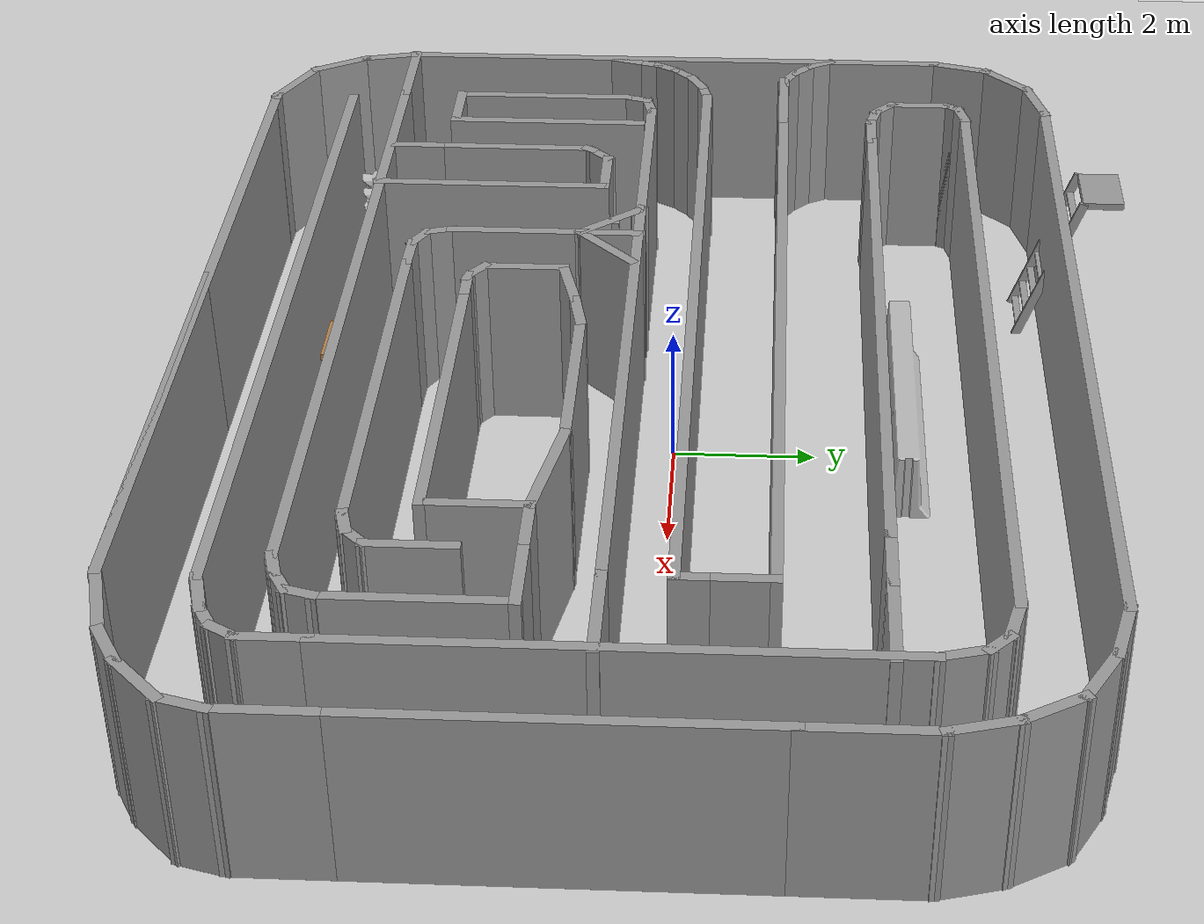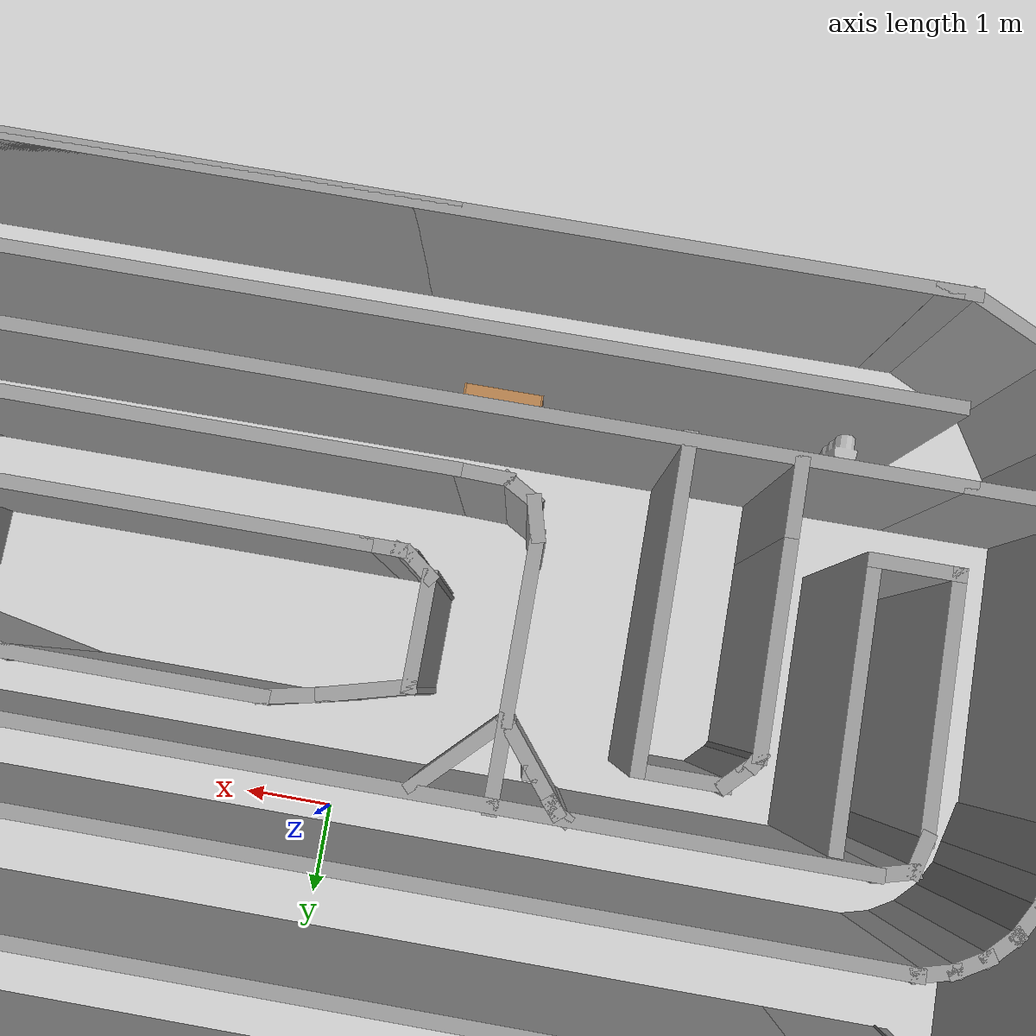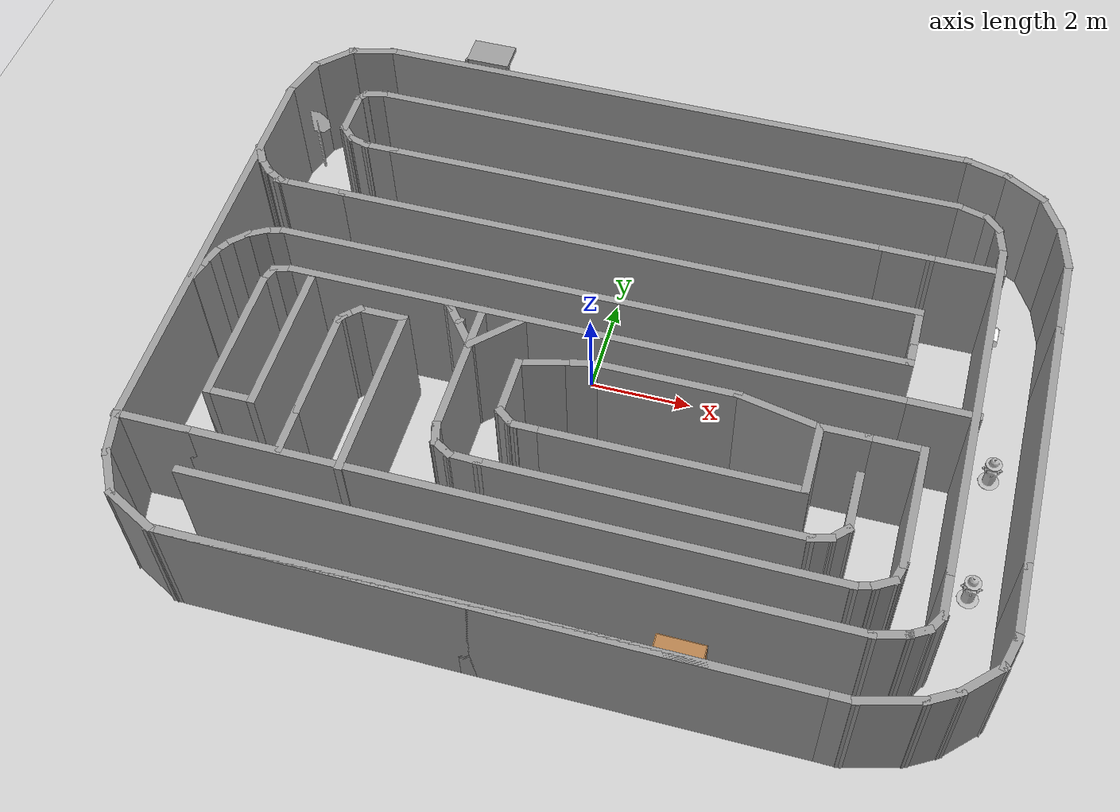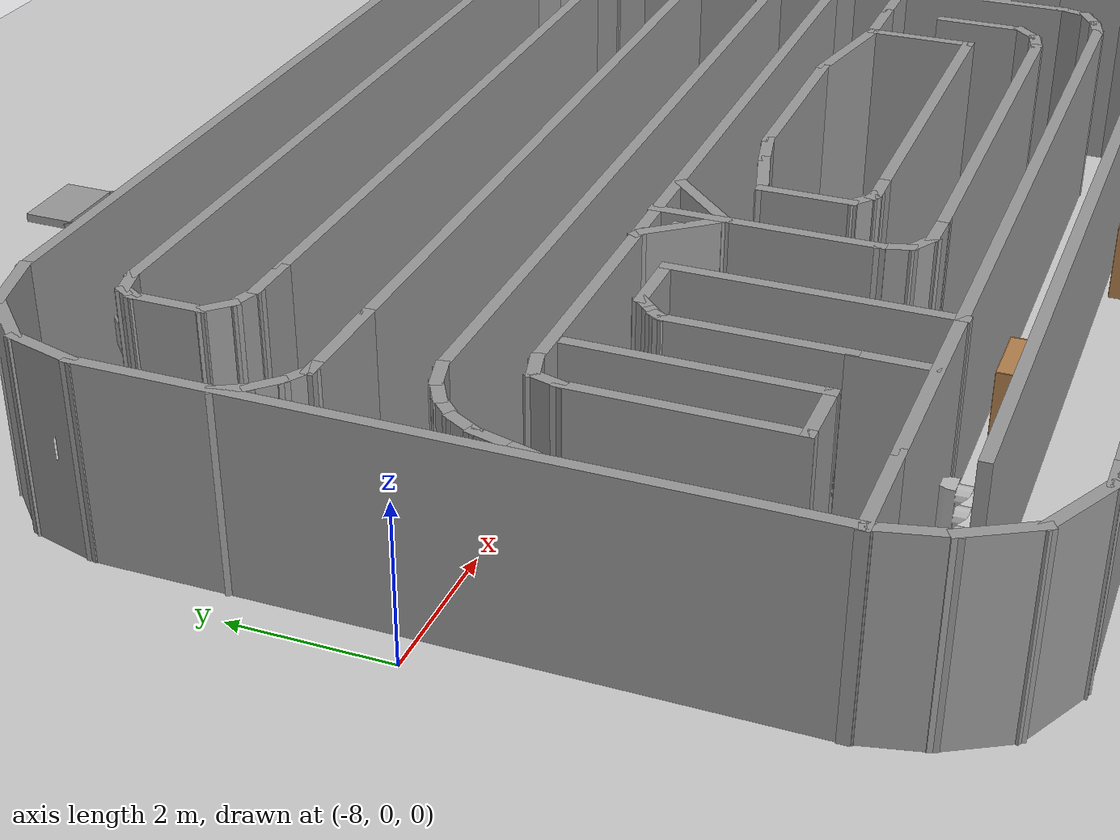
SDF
<sdf version="1.7">
 <world name="default">
  <light name="sun" type="directional">
   <pose>0 0 10 0 -0 0</pose>
   <diffuse>0.8 0.8 0.8 1</diffuse>
   <specular>0.2 0.2 0.2 1</specular>
   <attenuation>
    <range>1000</range>
    <constant>0.9</constant>
    <linear>0.01</linear>
    <quadratic>0.001</quadratic>
   </attenuation>
   <direction>-0.5 0.1 -0.9</direction>
   <spot><inner_angle>0</inner_angle><outer_angle>0</outer_angle><falloff>0</falloff></spot>
  </light>
  <model name="ground_plane">
   <static>1</static>
   <link name="link">
    <collision name="collision">
     <geometry><plane><normal>0 0 1</normal><size>100 100</size></plane></geometry>
     <surface>
      <contact><collide_bitmask>65535</collide_bitmask></contact>
      <friction><ode><mu>100</mu><mu2>50</mu2></ode></friction>
     </surface>
    </collision>
    <visual name="visual">
     <cast_shadows>0</cast_shadows>
     <geometry><plane><normal>0 0 1</normal><size>100 100</size></plane></geometry>
     <material>
      <script><uri>file://media/materials/scripts/gazebo.material</uri><name>Gazebo/Grey</name></script>
     </material>
    </visual>
   </link>
  </model>
  <gravity>0 0 -9.8</gravity>
  <magnetic_field>6e-06 2.3e-05 -4.2e-05</magnetic_field>
  <atmosphere type="adiabatic"/>
  <physics type="ode">
   <max_step_size>0.001</max_step_size>
   <real_time_factor>1</real_time_factor>
   <real_time_update_rate>1000</real_time_update_rate>
  </physics>
  <scene><ambient>0.4 0.4 0.4 1</ambient><background>0.7 0.7 0.7 1</background><shadows>1</shadows></scene>
  <spherical_coordinates>
   <surface_model>EARTH_WGS84</surface_model>
   <latitude_deg>0</latitude_deg>
   <longitude_deg>0</longitude_deg>
   <elevation>0</elevation>
   <heading_deg>0</heading_deg>
  </spherical_coordinates>
  <model name="Race_Track">
   <link name="Wall_0">
    <pose>2.08957 -6.00796 0 0 -0 0</pose>
    <visual name="Wall_0_Visual">
     <pose>0 0 1.25 0 -0 0</pose>
     <geometry><box><size>6.25 0.15 2.5</size></box></geometry>
     <material>
      <script><uri>file://media/materials/scripts/gazebo.material</uri><name>Gazebo/Grey</name></script>
      <ambient>1 1 1 1</ambient>
      <shader type="pixel"/>
     </material>
     <meta><layer>0</layer></meta>
    </visual>
    <collision name="Wall_0_Collision">
     <pose>0 0 1.25 0 -0 0</pose>
     <geometry><box><size>6.25 0.15 2.5</size></box></geometry>
     <surface>
      <friction>
       <ode><mu>1</mu><mu2>1</mu2><fdir1>0 0 0</fdir1><slip1>0</slip1><slip2>0</slip2></ode>
       <torsional>
        <coefficient>1</coefficient>
        <patch_radius>0</patch_radius>
        <surface_radius>0</surface_radius>
        <use_patch_radius>1</use_patch_radius>
        <ode><slip>0</slip></ode>
       </torsional>
      </friction>
      <bounce><restitution_coefficient>0</restitution_coefficient><threshold>1e+06</threshold></bounce>
      <contact>
       <collide_without_contact>0</collide_without_contact>
       <collide_without_contact_bitmask>1</collide_without_contact_bitmask>
       <collide_bitmask>1</collide_bitmask>
       <ode>
        <soft_cfm>0</soft_cfm>
        <soft_erp>0.2</soft_erp>
        <kp>1e+13</kp>
        <kd>1</kd>
        <max_vel>0.01</max_vel>
        <min_depth>0</min_depth>
       </ode>
       <bullet>
        <split_impulse>1</split_impulse>
        <split_impulse_penetration_threshold>-0.01</split_impulse_penetration_threshold>
        <soft_cfm>0</soft_cfm>
        <soft_erp>0.2</soft_erp>
        <kp>1e+13</kp>
        <kd>1</kd>
       </bullet>
      </contact>
     </surface>
    </collision>
   </link>
   <link name="Wall_1">
    <pose>-0.535432 -6.00796 0 0 -0 3.14159</pose>
    <visual name="Wall_1_Visual">
     <pose>0 0 1.25 0 -0 0</pose>
     <geometry><box><size>11.5 0.15 2.5</size></box></geometry>
     <material>
      <script><uri>file://media/materials/scripts/gazebo.material</uri><name>Gazebo/Grey</name></script>
      <ambient>1 1 1 1</ambient>
      <shader type="pixel"/>
     </material>
     <meta><layer>0</layer></meta>
    </visual>
    <collision name="Wall_1_Collision">
     <pose>0 0 1.25 0 -0 0</pose>
     <geometry><box><size>11.5 0.15 2.5</size></box></geometry>
     <surface>
      <friction>
       <ode><mu>1</mu><mu2>1</mu2><fdir1>0 0 0</fdir1><slip1>0</slip1><slip2>0</slip2></ode>
       <torsional>
        <coefficient>1</coefficient>
        <patch_radius>0</patch_radius>
        <surface_radius>0</surface_radius>
        <use_patch_radius>1</use_patch_radius>
        <ode><slip>0</slip></ode>
       </torsional>
      </friction>
      <bounce><restitution_coefficient>0</restitution_coefficient><threshold>1e+06</threshold></bounce>
      <contact>
       <collide_without_contact>0</collide_without_contact>
       <collide_without_contact_bitmask>1</collide_without_contact_bitmask>
       <collide_bitmask>1</collide_bitmask>
       <ode>
        <soft_cfm>0</soft_cfm>
        <soft_erp>0.2</soft_erp>
        <kp>1e+13</kp>
        <kd>1</kd>
        <max_vel>0.01</max_vel>
        <min_depth>0</min_depth>
       </ode>
       <bullet>
        <split_impulse>1</split_impulse>
        <split_impulse_penetration_threshold>-0.01</split_impulse_penetration_threshold>
        <soft_cfm>0</soft_cfm>
        <soft_erp>0.2</soft_erp>
        <kp>1e+13</kp>
        <kd>1</kd>
       </bullet>
      </contact>
     </surface>
    </collision>
   </link>
   <link name="Wall_100">
    <pose>-7.14893 0.577689 0 0 0 -2.61799</pose>
    <visual name="Wall_100_Visual">
     <pose>0 0 1.25 0 -0 0</pose>
     <geometry><box><size>0.5 0.15 2.5</size></box></geometry>
     <material>
      <script><uri>file://media/materials/scripts/gazebo.material</uri><name>Gazebo/Grey</name></script>
      <ambient>1 1 1 1</ambient>
      <shader type="pixel"/>
     </material>
     <meta><layer>0</layer></meta>
    </visual>
    <collision name="Wall_100_Collision">
     <pose>0 0 1.25 0 -0 0</pose>
     <geometry><box><size>0.5 0.15 2.5</size></box></geometry>
     <surface>
      <friction>
       <ode><mu>1</mu><mu2>1</mu2><fdir1>0 0 0</fdir1><slip1>0</slip1><slip2>0</slip2></ode>
       <torsional>
        <coefficient>1</coefficient>
        <patch_radius>0</patch_radius>
        <surface_radius>0</surface_radius>
        <use_patch_radius>1</use_patch_radius>
        <ode><slip>0</slip></ode>
       </torsional>
      </friction>
      <bounce><restitution_coefficient>0</restitution_coefficient><threshold>1e+06</threshold></bounce>
      <contact>
       <collide_without_contact>0</collide_without_contact>
       <collide_without_contact_bitmask>1</collide_without_contact_bitmask>
       <collide_bitmask>1</collide_bitmask>
       <ode>
        <soft_cfm>0</soft_cfm>
        <soft_erp>0.2</soft_erp>
        <kp>1e+13</kp>
        <kd>1</kd>
        <max_vel>0.01</max_vel>
        <min_depth>0</min_depth>
       </ode>
       <bullet>
        <split_impulse>1</split_impulse>
        <split_impulse_penetration_threshold>-0.01</split_impulse_penetration_threshold>
        <soft_cfm>0</soft_cfm>
        <soft_erp>0.2</soft_erp>
        <kp>1e+13</kp>
        <kd>1</kd>
       </bullet>
      </contact>
     </surface>
    </collision>
   </link>
   <link name="Wall_101">
    <pose>-7.42423 0.366446 0 0 0 -2.35619</pose>
    <visual name="Wall_101_Visual">
     <pose>0 0 1.25 0 -0 0</pose>
     <geometry><box><size>0.5 0.15 2.5</size></box></geometry>
     <material>
      <script><uri>file://media/materials/scripts/gazebo.material</uri><name>Gazebo/Grey</name></script>
      <ambient>1 1 1 1</ambient>
      <shader type="pixel"/>
     </material>
     <meta><layer>0</layer></meta>
    </visual>
    <collision name="Wall_101_Collision">
     <pose>0 0 1.25 0 -0 0</pose>
     <geometry><box><size>0.5 0.15 2.5</size></box></geometry>
     <surface>
      <friction>
       <ode><mu>1</mu><mu2>1</mu2><fdir1>0 0 0</fdir1><slip1>0</slip1><slip2>0</slip2></ode>
       <torsional>
        <coefficient>1</coefficient>
        <patch_radius>0</patch_radius>
        <surface_radius>0</surface_radius>
        <use_patch_radius>1</use_patch_radius>
        <ode><slip>0</slip></ode>
       </torsional>
      </friction>
      <bounce><restitution_coefficient>0</restitution_coefficient><threshold>1e+06</threshold></bounce>
      <contact>
       <collide_without_contact>0</collide_without_contact>
       <collide_without_contact_bitmask>1</collide_without_contact_bitmask>
       <collide_bitmask>1</collide_bitmask>
       <ode>
        <soft_cfm>0</soft_cfm>
        <soft_erp>0.2</soft_erp>
        <kp>1e+13</kp>
        <kd>1</kd>
        <max_vel>0.01</max_vel>
        <min_depth>0</min_depth>
       </ode>
       <bullet>
        <split_impulse>1</split_impulse>
        <split_impulse_penetration_threshold>-0.01</split_impulse_penetration_threshold>
        <soft_cfm>0</soft_cfm>
        <soft_erp>0.2</soft_erp>
        <kp>1e+13</kp>
        <kd>1</kd>
       </bullet>
      </contact>
     </surface>
    </collision>
   </link>
   <link name="Wall_102">
    <pose>-7.63547 0.091147 0 0 0 -2.0944</pose>
    <visual name="Wall_102_Visual">
     <pose>0 0 1.25 0 -0 0</pose>
     <geometry><box><size>0.5 0.15 2.5</size></box></geometry>
     <material>
      <script><uri>file://media/materials/scripts/gazebo.material</uri><name>Gazebo/Grey</name></script>
      <ambient>1 1 1 1</ambient>
      <shader type="pixel"/>
     </material>
     <meta><layer>0</layer></meta>
    </visual>
    <collision name="Wall_102_Collision">
     <pose>0 0 1.25 0 -0 0</pose>
     <geometry><box><size>0.5 0.15 2.5</size></box></geometry>
     <surface>
      <friction>
       <ode><mu>1</mu><mu2>1</mu2><fdir1>0 0 0</fdir1><slip1>0</slip1><slip2>0</slip2></ode>
       <torsional>
        <coefficient>1</coefficient>
        <patch_radius>0</patch_radius>
        <surface_radius>0</surface_radius>
        <use_patch_radius>1</use_patch_radius>
        <ode><slip>0</slip></ode>
       </torsional>
      </friction>
      <bounce><restitution_coefficient>0</restitution_coefficient><threshold>1e+06</threshold></bounce>
      <contact>
       <collide_without_contact>0</collide_without_contact>
       <collide_without_contact_bitmask>1</collide_without_contact_bitmask>
       <collide_bitmask>1</collide_bitmask>
       <ode>
        <soft_cfm>0</soft_cfm>
        <soft_erp>0.2</soft_erp>
        <kp>1e+13</kp>
        <kd>1</kd>
        <max_vel>0.01</max_vel>
        <min_depth>0</min_depth>
       </ode>
       <bullet>
        <split_impulse>1</split_impulse>
        <split_impulse_penetration_threshold>-0.01</split_impulse_penetration_threshold>
        <soft_cfm>0</soft_cfm>
        <soft_erp>0.2</soft_erp>
        <kp>1e+13</kp>
        <kd>1</kd>
       </bullet>
      </contact>
     </surface>
    </collision>
   </link>
   <link name="Wall_103">
    <pose>-7.76827 -0.229444 0 0 0 -1.8326</pose>
    <visual name="Wall_103_Visual">
     <pose>0 0 1.25 0 -0 0</pose>
     <geometry><box><size>0.5 0.15 2.5</size></box></geometry>
     <material>
      <script><uri>file://media/materials/scripts/gazebo.material</uri><name>Gazebo/Grey</name></script>
      <ambient>1 1 1 1</ambient>
      <shader type="pixel"/>
     </material>
     <meta><layer>0</layer></meta>
    </visual>
    <collision name="Wall_103_Collision">
     <pose>0 0 1.25 0 -0 0</pose>
     <geometry><box><size>0.5 0.15 2.5</size></box></geometry>
     <surface>
      <friction>
       <ode><mu>1</mu><mu2>1</mu2><fdir1>0 0 0</fdir1><slip1>0</slip1><slip2>0</slip2></ode>
       <torsional>
        <coefficient>1</coefficient>
        <patch_radius>0</patch_radius>
        <surface_radius>0</surface_radius>
        <use_patch_radius>1</use_patch_radius>
        <ode><slip>0</slip></ode>
       </torsional>
      </friction>
      <bounce><restitution_coefficient>0</restitution_coefficient><threshold>1e+06</threshold></bounce>
      <contact>
       <collide_without_contact>0</collide_without_contact>
       <collide_without_contact_bitmask>1</collide_without_contact_bitmask>
       <collide_bitmask>1</collide_bitmask>
       <ode>
        <soft_cfm>0</soft_cfm>
        <soft_erp>0.2</soft_erp>
        <kp>1e+13</kp>
        <kd>1</kd>
        <max_vel>0.01</max_vel>
        <min_depth>0</min_depth>
       </ode>
       <bullet>
        <split_impulse>1</split_impulse>
        <split_impulse_penetration_threshold>-0.01</split_impulse_penetration_threshold>
        <soft_cfm>0</soft_cfm>
        <soft_erp>0.2</soft_erp>
        <kp>1e+13</kp>
        <kd>1</kd>
       </bullet>
      </contact>
     </surface>
    </collision>
   </link>
   <link name="Wall_104">
    <pose>-7.85885 -0.567518 0 0 0 -1.8326</pose>
    <visual name="Wall_104_Visual">
     <pose>0 0 1.25 0 -0 0</pose>
     <geometry><box><size>0.5 0.15 2.5</size></box></geometry>
     <material>
      <script><uri>file://media/materials/scripts/gazebo.material</uri><name>Gazebo/Grey</name></script>
      <ambient>1 1 1 1</ambient>
      <shader type="pixel"/>
     </material>
     <meta><layer>0</layer></meta>
    </visual>
    <collision name="Wall_104_Collision">
     <pose>0 0 1.25 0 -0 0</pose>
     <geometry><box><size>0.5 0.15 2.5</size></box></geometry>
     <surface>
      <friction>
       <ode><mu>1</mu><mu2>1</mu2><fdir1>0 0 0</fdir1><slip1>0</slip1><slip2>0</slip2></ode>
       <torsional>
        <coefficient>1</coefficient>
        <patch_radius>0</patch_radius>
        <surface_radius>0</surface_radius>
        <use_patch_radius>1</use_patch_radius>
        <ode><slip>0</slip></ode>
       </torsional>
      </friction>
      <bounce><restitution_coefficient>0</restitution_coefficient><threshold>1e+06</threshold></bounce>
      <contact>
       <collide_without_contact>0</collide_without_contact>
       <collide_without_contact_bitmask>1</collide_without_contact_bitmask>
       <collide_bitmask>1</collide_bitmask>
       <ode>
        <soft_cfm>0</soft_cfm>
        <soft_erp>0.2</soft_erp>
        <kp>1e+13</kp>
        <kd>1</kd>
        <max_vel>0.01</max_vel>
        <min_depth>0</min_depth>
       </ode>
       <bullet>
        <split_impulse>1</split_impulse>
        <split_impulse_penetration_threshold>-0.01</split_impulse_penetration_threshold>
        <soft_cfm>0</soft_cfm>
        <soft_erp>0.2</soft_erp>
        <kp>1e+13</kp>
        <kd>1</kd>
       </bullet>
      </contact>
     </surface>
    </collision>
   </link>
   <link name="Wall_106">
    <pose>-6.32834 -0.139517 0 0 0 -2.87979</pose>
    <visual name="Wall_106_Visual">
     <pose>0 0 1.25 0 -0 0</pose>
     <geometry><box><size>0.5 0.15 2.5</size></box></geometry>
     <material>
      <script><uri>file://media/materials/scripts/gazebo.material</uri><name>Gazebo/Grey</name></script>
      <ambient>1 1 1 1</ambient>
      <shader type="pixel"/>
     </material>
     <meta><layer>0</layer></meta>
    </visual>
    <collision name="Wall_106_Collision">
     <pose>0 0 1.25 0 -0 0</pose>
     <geometry><box><size>0.5 0.15 2.5</size></box></geometry>
     <surface>
      <friction>
       <ode><mu>1</mu><mu2>1</mu2><fdir1>0 0 0</fdir1><slip1>0</slip1><slip2>0</slip2></ode>
       <torsional>
        <coefficient>1</coefficient>
        <patch_radius>0</patch_radius>
        <surface_radius>0</surface_radius>
        <use_patch_radius>1</use_patch_radius>
        <ode><slip>0</slip></ode>
       </torsional>
      </friction>
      <bounce><restitution_coefficient>0</restitution_coefficient><threshold>1e+06</threshold></bounce>
      <contact>
       <collide_without_contact>0</collide_without_contact>
       <collide_without_contact_bitmask>1</collide_without_contact_bitmask>
       <collide_bitmask>1</collide_bitmask>
       <ode>
        <soft_cfm>0</soft_cfm>
        <soft_erp>0.2</soft_erp>
        <kp>1e+13</kp>
        <kd>1</kd>
        <max_vel>0.01</max_vel>
        <min_depth>0</min_depth>
       </ode>
       <bullet>
        <split_impulse>1</split_impulse>
        <split_impulse_penetration_threshold>-0.01</split_impulse_penetration_threshold>
        <soft_cfm>0</soft_cfm>
        <soft_erp>0.2</soft_erp>
        <kp>1e+13</kp>
        <kd>1</kd>
       </bullet>
      </contact>
     </surface>
    </collision>
   </link>
   <link name="Wall_107">
    <pose>-6.54267 -0.34589 0 0 0 -1.84491</pose>
    <visual name="Wall_107_Visual">
     <pose>0 0 1.25 0 -0 0</pose>
     <geometry><box><size>0.484652 0.15 2.5</size></box></geometry>
     <material>
      <script><uri>file://media/materials/scripts/gazebo.material</uri><name>Gazebo/Grey</name></script>
      <ambient>1 1 1 1</ambient>
      <shader type="pixel"/>
     </material>
     <meta><layer>0</layer></meta>
    </visual>
    <collision name="Wall_107_Collision">
     <pose>0 0 1.25 0 -0 0</pose>
     <geometry><box><size>0.484652 0.15 2.5</size></box></geometry>
     <surface>
      <friction>
       <ode><mu>1</mu><mu2>1</mu2><fdir1>0 0 0</fdir1><slip1>0</slip1><slip2>0</slip2></ode>
       <torsional>
        <coefficient>1</coefficient>
        <patch_radius>0</patch_radius>
        <surface_radius>0</surface_radius>
        <use_patch_radius>1</use_patch_radius>
        <ode><slip>0</slip></ode>
       </torsional>
      </friction>
      <bounce><restitution_coefficient>0</restitution_coefficient><threshold>1e+06</threshold></bounce>
      <contact>
       <collide_without_contact>0</collide_without_contact>
       <collide_without_contact_bitmask>1</collide_without_contact_bitmask>
       <collide_bitmask>1</collide_bitmask>
       <ode>
        <soft_cfm>0</soft_cfm>
        <soft_erp>0.2</soft_erp>
        <kp>1e+13</kp>
        <kd>1</kd>
        <max_vel>0.01</max_vel>
        <min_depth>0</min_depth>
       </ode>
       <bullet>
        <split_impulse>1</split_impulse>
        <split_impulse_penetration_threshold>-0.01</split_impulse_penetration_threshold>
        <soft_cfm>0</soft_cfm>
        <soft_erp>0.2</soft_erp>
        <kp>1e+13</kp>
        <kd>1</kd>
       </bullet>
      </contact>
     </surface>
    </collision>
   </link>
   <link name="Wall_112">
    <pose>-6.58796 -1.80697 0 0 0 -1.5708</pose>
    <visual name="Wall_112_Visual">
     <pose>0 0 1.25 0 -0 0</pose>
     <geometry><box><size>2.75 0.15 2.5</size></box></geometry>
     <material>
      <script><uri>file://media/materials/scripts/gazebo.material</uri><name>Gazebo/Grey</name></script>
      <ambient>1 1 1 1</ambient>
      <shader type="pixel"/>
     </material>
     <meta><layer>0</layer></meta>
    </visual>
    <collision name="Wall_112_Collision">
     <pose>0 0 1.25 0 -0 0</pose>
     <geometry><box><size>2.75 0.15 2.5</size></box></geometry>
     <surface>
      <friction>
       <ode><mu>1</mu><mu2>1</mu2><fdir1>0 0 0</fdir1><slip1>0</slip1><slip2>0</slip2></ode>
       <torsional>
        <coefficient>1</coefficient>
        <patch_radius>0</patch_radius>
        <surface_radius>0</surface_radius>
        <use_patch_radius>1</use_patch_radius>
        <ode><slip>0</slip></ode>
       </torsional>
      </friction>
      <bounce><restitution_coefficient>0</restitution_coefficient><threshold>1e+06</threshold></bounce>
      <contact>
       <collide_without_contact>0</collide_without_contact>
       <collide_without_contact_bitmask>1</collide_without_contact_bitmask>
       <collide_bitmask>1</collide_bitmask>
       <ode>
        <soft_cfm>0</soft_cfm>
        <soft_erp>0.2</soft_erp>
        <kp>1e+13</kp>
        <kd>1</kd>
        <max_vel>0.01</max_vel>
        <min_depth>0</min_depth>
       </ode>
       <bullet>
        <split_impulse>1</split_impulse>
        <split_impulse_penetration_threshold>-0.01</split_impulse_penetration_threshold>
        <soft_cfm>0</soft_cfm>
        <soft_erp>0.2</soft_erp>
        <kp>1e+13</kp>
        <kd>1</kd>
       </bullet>
      </contact>
     </surface>
    </collision>
   </link>
   <link name="Wall_114">
    <pose>-6.16296 -3.10697 0 0 -0 0</pose>
    <visual name="Wall_114_Visual">
     <pose>0 0 1.25 0 -0 0</pose>
     <geometry><box><size>1 0.15 2.5</size></box></geometry>
     <material>
      <script><uri>file://media/materials/scripts/gazebo.material</uri><name>Gazebo/Grey</name></script>
      <ambient>1 1 1 1</ambient>
      <shader type="pixel"/>
     </material>
     <meta><layer>0</layer></meta>
    </visual>
    <collision name="Wall_114_Collision">
     <pose>0 0 1.25 0 -0 0</pose>
     <geometry><box><size>1 0.15 2.5</size></box></geometry>
     <surface>
      <friction>
       <ode><mu>1</mu><mu2>1</mu2><fdir1>0 0 0</fdir1><slip1>0</slip1><slip2>0</slip2></ode>
       <torsional>
        <coefficient>1</coefficient>
        <patch_radius>0</patch_radius>
        <surface_radius>0</surface_radius>
        <use_patch_radius>1</use_patch_radius>
        <ode><slip>0</slip></ode>
       </torsional>
      </friction>
      <bounce><restitution_coefficient>0</restitution_coefficient><threshold>1e+06</threshold></bounce>
      <contact>
       <collide_without_contact>0</collide_without_contact>
       <collide_without_contact_bitmask>1</collide_without_contact_bitmask>
       <collide_bitmask>1</collide_bitmask>
       <ode>
        <soft_cfm>0</soft_cfm>
        <soft_erp>0.2</soft_erp>
        <kp>1e+13</kp>
        <kd>1</kd>
        <max_vel>0.01</max_vel>
        <min_depth>0</min_depth>
       </ode>
       <bullet>
        <split_impulse>1</split_impulse>
        <split_impulse_penetration_threshold>-0.01</split_impulse_penetration_threshold>
        <soft_cfm>0</soft_cfm>
        <soft_erp>0.2</soft_erp>
        <kp>1e+13</kp>
        <kd>1</kd>
       </bullet>
      </contact>
     </surface>
    </collision>
   </link>
   <link name="Wall_123">
    <pose>-0.672789 -4.00099 0 0 -0 0</pose>
    <visual name="Wall_123_Visual">
     <pose>0 0 1.25 0 -0 0</pose>
     <geometry><box><size>12 0.15 2.5</size></box></geometry>
     <material>
      <script><uri>file://media/materials/scripts/gazebo.material</uri><name>Gazebo/Grey</name></script>
      <ambient>1 1 1 1</ambient>
      <shader type="pixel"/>
     </material>
     <meta><layer>0</layer></meta>
    </visual>
    <collision name="Wall_123_Collision">
     <pose>0 0 1.25 0 -0 0</pose>
     <geometry><box><size>12 0.15 2.5</size></box></geometry>
     <surface>
      <friction>
       <ode><mu>1</mu><mu2>1</mu2><fdir1>0 0 0</fdir1><slip1>0</slip1><slip2>0</slip2></ode>
       <torsional>
        <coefficient>1</coefficient>
        <patch_radius>0</patch_radius>
        <surface_radius>0</surface_radius>
        <use_patch_radius>1</use_patch_radius>
        <ode><slip>0</slip></ode>
       </torsional>
      </friction>
      <bounce><restitution_coefficient>0</restitution_coefficient><threshold>1e+06</threshold></bounce>
      <contact>
       <collide_without_contact>0</collide_without_contact>
       <collide_without_contact_bitmask>1</collide_without_contact_bitmask>
       <collide_bitmask>1</collide_bitmask>
       <ode>
        <soft_cfm>0</soft_cfm>
        <soft_erp>0.2</soft_erp>
        <kp>1e+13</kp>
        <kd>1</kd>
        <max_vel>0.01</max_vel>
        <min_depth>0</min_depth>
       </ode>
       <bullet>
        <split_impulse>1</split_impulse>
        <split_impulse_penetration_threshold>-0.01</split_impulse_penetration_threshold>
        <soft_cfm>0</soft_cfm>
        <soft_erp>0.2</soft_erp>
        <kp>1e+13</kp>
        <kd>1</kd>
       </bullet>
      </contact>
     </surface>
    </collision>
   </link>
   <link name="Wall_125">
    <pose>5.42125 -3.9557 0 0 -0 0.261799</pose>
    <visual name="Wall_125_Visual">
     <pose>0 0 1.25 0 -0 0</pose>
     <geometry><box><size>0.5 0.15 2.5</size></box></geometry>
     <material>
      <script><uri>file://media/materials/scripts/gazebo.material</uri><name>Gazebo/Grey</name></script>
      <ambient>1 1 1 1</ambient>
      <shader type="pixel"/>
     </material>
     <meta><layer>0</layer></meta>
    </visual>
    <collision name="Wall_125_Collision">
     <pose>0 0 1.25 0 -0 0</pose>
     <geometry><box><size>0.5 0.15 2.5</size></box></geometry>
     <surface>
      <friction>
       <ode><mu>1</mu><mu2>1</mu2><fdir1>0 0 0</fdir1><slip1>0</slip1><slip2>0</slip2></ode>
       <torsional>
        <coefficient>1</coefficient>
        <patch_radius>0</patch_radius>
        <surface_radius>0</surface_radius>
        <use_patch_radius>1</use_patch_radius>
        <ode><slip>0</slip></ode>
       </torsional>
      </friction>
      <bounce><restitution_coefficient>0</restitution_coefficient><threshold>1e+06</threshold></bounce>
      <contact>
       <collide_without_contact>0</collide_without_contact>
       <collide_without_contact_bitmask>1</collide_without_contact_bitmask>
       <collide_bitmask>1</collide_bitmask>
       <ode>
        <soft_cfm>0</soft_cfm>
        <soft_erp>0.2</soft_erp>
        <kp>1e+13</kp>
        <kd>1</kd>
        <max_vel>0.01</max_vel>
        <min_depth>0</min_depth>
       </ode>
       <bullet>
        <split_impulse>1</split_impulse>
        <split_impulse_penetration_threshold>-0.01</split_impulse_penetration_threshold>
        <soft_cfm>0</soft_cfm>
        <soft_erp>0.2</soft_erp>
        <kp>1e+13</kp>
        <kd>1</kd>
       </bullet>
      </contact>
     </surface>
    </collision>
   </link>
   <link name="Wall_126">
    <pose>5.74184 -3.8229 0 0 -0 0.523599</pose>
    <visual name="Wall_126_Visual">
     <pose>0 0 1.25 0 -0 0</pose>
     <geometry><box><size>0.5 0.15 2.5</size></box></geometry>
     <material>
      <script><uri>file://media/materials/scripts/gazebo.material</uri><name>Gazebo/Grey</name></script>
      <ambient>1 1 1 1</ambient>
      <shader type="pixel"/>
     </material>
     <meta><layer>0</layer></meta>
    </visual>
    <collision name="Wall_126_Collision">
     <pose>0 0 1.25 0 -0 0</pose>
     <geometry><box><size>0.5 0.15 2.5</size></box></geometry>
     <surface>
      <friction>
       <ode><mu>1</mu><mu2>1</mu2><fdir1>0 0 0</fdir1><slip1>0</slip1><slip2>0</slip2></ode>
       <torsional>
        <coefficient>1</coefficient>
        <patch_radius>0</patch_radius>
        <surface_radius>0</surface_radius>
        <use_patch_radius>1</use_patch_radius>
        <ode><slip>0</slip></ode>
       </torsional>
      </friction>
      <bounce><restitution_coefficient>0</restitution_coefficient><threshold>1e+06</threshold></bounce>
      <contact>
       <collide_without_contact>0</collide_without_contact>
       <collide_without_contact_bitmask>1</collide_without_contact_bitmask>
       <collide_bitmask>1</collide_bitmask>
       <ode>
        <soft_cfm>0</soft_cfm>
        <soft_erp>0.2</soft_erp>
        <kp>1e+13</kp>
        <kd>1</kd>
        <max_vel>0.01</max_vel>
        <min_depth>0</min_depth>
       </ode>
       <bullet>
        <split_impulse>1</split_impulse>
        <split_impulse_penetration_threshold>-0.01</split_impulse_penetration_threshold>
        <soft_cfm>0</soft_cfm>
        <soft_erp>0.2</soft_erp>
        <kp>1e+13</kp>
        <kd>1</kd>
       </bullet>
      </contact>
     </surface>
    </collision>
   </link>
   <link name="Wall_127">
    <pose>5.93869 -3.56637 0 0 -0 1.309</pose>
    <visual name="Wall_127_Visual">
     <pose>0 0 1.25 0 -0 0</pose>
     <geometry><box><size>0.5 0.15 2.5</size></box></geometry>
     <material>
      <script><uri>file://media/materials/scripts/gazebo.material</uri><name>Gazebo/Grey</name></script>
      <ambient>1 1 1 1</ambient>
      <shader type="pixel"/>
     </material>
     <meta><layer>0</layer></meta>
    </visual>
    <collision name="Wall_127_Collision">
     <pose>0 0 1.25 0 -0 0</pose>
     <geometry><box><size>0.5 0.15 2.5</size></box></geometry>
     <surface>
      <friction>
       <ode><mu>1</mu><mu2>1</mu2><fdir1>0 0 0</fdir1><slip1>0</slip1><slip2>0</slip2></ode>
       <torsional>
        <coefficient>1</coefficient>
        <patch_radius>0</patch_radius>
        <surface_radius>0</surface_radius>
        <use_patch_radius>1</use_patch_radius>
        <ode><slip>0</slip></ode>
       </torsional>
      </friction>
      <bounce><restitution_coefficient>0</restitution_coefficient><threshold>1e+06</threshold></bounce>
      <contact>
       <collide_without_contact>0</collide_without_contact>
       <collide_without_contact_bitmask>1</collide_without_contact_bitmask>
       <collide_bitmask>1</collide_bitmask>
       <ode>
        <soft_cfm>0</soft_cfm>
        <soft_erp>0.2</soft_erp>
        <kp>1e+13</kp>
        <kd>1</kd>
        <max_vel>0.01</max_vel>
        <min_depth>0</min_depth>
       </ode>
       <bullet>
        <split_impulse>1</split_impulse>
        <split_impulse_penetration_threshold>-0.01</split_impulse_penetration_threshold>
        <soft_cfm>0</soft_cfm>
        <soft_erp>0.2</soft_erp>
        <kp>1e+13</kp>
        <kd>1</kd>
       </bullet>
      </contact>
     </surface>
    </collision>
   </link>
   <link name="Wall_128">
    <pose>5.98398 -2.22233 0 0 -0 1.5708</pose>
    <visual name="Wall_128_Visual">
     <pose>0 0 1.25 0 -0 0</pose>
     <geometry><box><size>2.5 0.15 2.5</size></box></geometry>
     <material>
      <script><uri>file://media/materials/scripts/gazebo.material</uri><name>Gazebo/Grey</name></script>
      <ambient>1 1 1 1</ambient>
      <shader type="pixel"/>
     </material>
     <meta><layer>0</layer></meta>
    </visual>
    <collision name="Wall_128_Collision">
     <pose>0 0 1.25 0 -0 0</pose>
     <geometry><box><size>2.5 0.15 2.5</size></box></geometry>
     <surface>
      <friction>
       <ode><mu>1</mu><mu2>1</mu2><fdir1>0 0 0</fdir1><slip1>0</slip1><slip2>0</slip2></ode>
       <torsional>
        <coefficient>1</coefficient>
        <patch_radius>0</patch_radius>
        <surface_radius>0</surface_radius>
        <use_patch_radius>1</use_patch_radius>
        <ode><slip>0</slip></ode>
       </torsional>
      </friction>
      <bounce><restitution_coefficient>0</restitution_coefficient><threshold>1e+06</threshold></bounce>
      <contact>
       <collide_without_contact>0</collide_without_contact>
       <collide_without_contact_bitmask>1</collide_without_contact_bitmask>
       <collide_bitmask>1</collide_bitmask>
       <ode>
        <soft_cfm>0</soft_cfm>
        <soft_erp>0.2</soft_erp>
        <kp>1e+13</kp>
        <kd>1</kd>
        <max_vel>0.01</max_vel>
        <min_depth>0</min_depth>
       </ode>
       <bullet>
        <split_impulse>1</split_impulse>
        <split_impulse_penetration_threshold>-0.01</split_impulse_penetration_threshold>
        <soft_cfm>0</soft_cfm>
        <soft_erp>0.2</soft_erp>
        <kp>1e+13</kp>
        <kd>1</kd>
       </bullet>
      </contact>
     </surface>
    </collision>
   </link>
   <link name="Wall_131">
    <pose>-5.73796 -1.68197 0 0 -0 1.5708</pose>
    <visual name="Wall_131_Visual">
     <pose>0 0 1.25 0 -0 0</pose>
     <geometry><box><size>3 0.15 2.5</size></box></geometry>
     <material>
      <script><uri>file://media/materials/scripts/gazebo.material</uri><name>Gazebo/Grey</name></script>
      <ambient>1 1 1 1</ambient>
      <shader type="pixel"/>
     </material>
     <meta><layer>0</layer></meta>
    </visual>
    <collision name="Wall_131_Collision">
     <pose>0 0 1.25 0 -0 0</pose>
     <geometry><box><size>3 0.15 2.5</size></box></geometry>
     <surface>
      <friction>
       <ode><mu>1</mu><mu2>1</mu2><fdir1>0 0 0</fdir1><slip1>0</slip1><slip2>0</slip2></ode>
       <torsional>
        <coefficient>1</coefficient>
        <patch_radius>0</patch_radius>
        <surface_radius>0</surface_radius>
        <use_patch_radius>1</use_patch_radius>
        <ode><slip>0</slip></ode>
       </torsional>
      </friction>
      <bounce><restitution_coefficient>0</restitution_coefficient><threshold>1e+06</threshold></bounce>
      <contact>
       <collide_without_contact>0</collide_without_contact>
       <collide_without_contact_bitmask>1</collide_without_contact_bitmask>
       <collide_bitmask>1</collide_bitmask>
       <ode>
        <soft_cfm>0</soft_cfm>
        <soft_erp>0.2</soft_erp>
        <kp>1e+13</kp>
        <kd>1</kd>
        <max_vel>0.01</max_vel>
        <min_depth>0</min_depth>
       </ode>
       <bullet>
        <split_impulse>1</split_impulse>
        <split_impulse_penetration_threshold>-0.01</split_impulse_penetration_threshold>
        <soft_cfm>0</soft_cfm>
        <soft_erp>0.2</soft_erp>
        <kp>1e+13</kp>
        <kd>1</kd>
       </bullet>
      </contact>
     </surface>
    </collision>
   </link>
   <link name="Wall_135">
    <pose>-4.88796 -3.53197 0 0 0 -1.5708</pose>
    <visual name="Wall_135_Visual">
     <pose>0 0 1.25 0 -0 0</pose>
     <geometry><box><size>1 0.15 2.5</size></box></geometry>
     <material>
      <script><uri>file://media/materials/scripts/gazebo.material</uri><name>Gazebo/Grey</name></script>
      <ambient>1 1 1 1</ambient>
      <shader type="pixel"/>
     </material>
     <meta><layer>0</layer></meta>
    </visual>
    <collision name="Wall_135_Collision">
     <pose>0 0 1.25 0 -0 0</pose>
     <geometry><box><size>1 0.15 2.5</size></box></geometry>
     <surface>
      <friction>
       <ode><mu>1</mu><mu2>1</mu2><fdir1>0 0 0</fdir1><slip1>0</slip1><slip2>0</slip2></ode>
       <torsional>
        <coefficient>1</coefficient>
        <patch_radius>0</patch_radius>
        <surface_radius>0</surface_radius>
        <use_patch_radius>1</use_patch_radius>
        <ode><slip>0</slip></ode>
       </torsional>
      </friction>
      <bounce><restitution_coefficient>0</restitution_coefficient><threshold>1e+06</threshold></bounce>
      <contact>
       <collide_without_contact>0</collide_without_contact>
       <collide_without_contact_bitmask>1</collide_without_contact_bitmask>
       <collide_bitmask>1</collide_bitmask>
       <ode>
        <soft_cfm>0</soft_cfm>
        <soft_erp>0.2</soft_erp>
        <kp>1e+13</kp>
        <kd>1</kd>
        <max_vel>0.01</max_vel>
        <min_depth>0</min_depth>
       </ode>
       <bullet>
        <split_impulse>1</split_impulse>
        <split_impulse_penetration_threshold>-0.01</split_impulse_penetration_threshold>
        <soft_cfm>0</soft_cfm>
        <soft_erp>0.2</soft_erp>
        <kp>1e+13</kp>
        <kd>1</kd>
       </bullet>
      </contact>
     </surface>
    </collision>
   </link>
   <link name="Wall_137">
    <pose>-4.88796 -2.05697 0 0 -0 1.5708</pose>
    <visual name="Wall_137_Visual">
     <pose>0 0 1.25 0 -0 0</pose>
     <geometry><box><size>2.25 0.15 2.5</size></box></geometry>
     <material>
      <script><uri>file://media/materials/scripts/gazebo.material</uri><name>Gazebo/Grey</name></script>
      <ambient>1 1 1 1</ambient>
      <shader type="pixel"/>
     </material>
     <meta><layer>0</layer></meta>
    </visual>
    <collision name="Wall_137_Collision">
     <pose>0 0 1.25 0 -0 0</pose>
     <geometry><box><size>2.25 0.15 2.5</size></box></geometry>
     <surface>
      <friction>
       <ode><mu>1</mu><mu2>1</mu2><fdir1>0 0 0</fdir1><slip1>0</slip1><slip2>0</slip2></ode>
       <torsional>
        <coefficient>1</coefficient>
        <patch_radius>0</patch_radius>
        <surface_radius>0</surface_radius>
        <use_patch_radius>1</use_patch_radius>
        <ode><slip>0</slip></ode>
       </torsional>
      </friction>
      <bounce><restitution_coefficient>0</restitution_coefficient><threshold>1e+06</threshold></bounce>
      <contact>
       <collide_without_contact>0</collide_without_contact>
       <collide_without_contact_bitmask>1</collide_without_contact_bitmask>
       <collide_bitmask>1</collide_bitmask>
       <ode>
        <soft_cfm>0</soft_cfm>
        <soft_erp>0.2</soft_erp>
        <kp>1e+13</kp>
        <kd>1</kd>
        <max_vel>0.01</max_vel>
        <min_depth>0</min_depth>
       </ode>
       <bullet>
        <split_impulse>1</split_impulse>
        <split_impulse_penetration_threshold>-0.01</split_impulse_penetration_threshold>
        <soft_cfm>0</soft_cfm>
        <soft_erp>0.2</soft_erp>
        <kp>1e+13</kp>
        <kd>1</kd>
       </bullet>
      </contact>
     </surface>
    </collision>
   </link>
   <link name="Wall_139">
    <pose>-4.86296 -0.963668 0 0 -0 1.0472</pose>
    <visual name="Wall_139_Visual">
     <pose>0 0 1.25 0 -0 0</pose>
     <geometry><box><size>0.25 0.15 2.5</size></box></geometry>
     <material>
      <script><uri>file://media/materials/scripts/gazebo.material</uri><name>Gazebo/Grey</name></script>
      <ambient>1 1 1 1</ambient>
      <shader type="pixel"/>
     </material>
     <meta><layer>0</layer></meta>
    </visual>
    <collision name="Wall_139_Collision">
     <pose>0 0 1.25 0 -0 0</pose>
     <geometry><box><size>0.25 0.15 2.5</size></box></geometry>
     <surface>
      <friction>
       <ode><mu>1</mu><mu2>1</mu2><fdir1>0 0 0</fdir1><slip1>0</slip1><slip2>0</slip2></ode>
       <torsional>
        <coefficient>1</coefficient>
        <patch_radius>0</patch_radius>
        <surface_radius>0</surface_radius>
        <use_patch_radius>1</use_patch_radius>
        <ode><slip>0</slip></ode>
       </torsional>
      </friction>
      <bounce><restitution_coefficient>0</restitution_coefficient><threshold>1e+06</threshold></bounce>
      <contact>
       <collide_without_contact>0</collide_without_contact>
       <collide_without_contact_bitmask>1</collide_without_contact_bitmask>
       <collide_bitmask>1</collide_bitmask>
       <ode>
        <soft_cfm>0</soft_cfm>
        <soft_erp>0.2</soft_erp>
        <kp>1e+13</kp>
        <kd>1</kd>
        <max_vel>0.01</max_vel>
        <min_depth>0</min_depth>
       </ode>
       <bullet>
        <split_impulse>1</split_impulse>
        <split_impulse_penetration_threshold>-0.01</split_impulse_penetration_threshold>
        <soft_cfm>0</soft_cfm>
        <soft_erp>0.2</soft_erp>
        <kp>1e+13</kp>
        <kd>1</kd>
       </bullet>
      </contact>
     </surface>
    </collision>
   </link>
   <link name="Wall_140">
    <pose>-4.80261 -0.885012 0 0 -0 0.785398</pose>
    <visual name="Wall_140_Visual">
     <pose>0 0 1.25 0 -0 0</pose>
     <geometry><box><size>0.25 0.15 2.5</size></box></geometry>
     <material>
      <script><uri>file://media/materials/scripts/gazebo.material</uri><name>Gazebo/Grey</name></script>
      <ambient>1 1 1 1</ambient>
      <shader type="pixel"/>
     </material>
     <meta><layer>0</layer></meta>
    </visual>
    <collision name="Wall_140_Collision">
     <pose>0 0 1.25 0 -0 0</pose>
     <geometry><box><size>0.25 0.15 2.5</size></box></geometry>
     <surface>
      <friction>
       <ode><mu>1</mu><mu2>1</mu2><fdir1>0 0 0</fdir1><slip1>0</slip1><slip2>0</slip2></ode>
       <torsional>
        <coefficient>1</coefficient>
        <patch_radius>0</patch_radius>
        <surface_radius>0</surface_radius>
        <use_patch_radius>1</use_patch_radius>
        <ode><slip>0</slip></ode>
       </torsional>
      </friction>
      <bounce><restitution_coefficient>0</restitution_coefficient><threshold>1e+06</threshold></bounce>
      <contact>
       <collide_without_contact>0</collide_without_contact>
       <collide_without_contact_bitmask>1</collide_without_contact_bitmask>
       <collide_bitmask>1</collide_bitmask>
       <ode>
        <soft_cfm>0</soft_cfm>
        <soft_erp>0.2</soft_erp>
        <kp>1e+13</kp>
        <kd>1</kd>
        <max_vel>0.01</max_vel>
        <min_depth>0</min_depth>
       </ode>
       <bullet>
        <split_impulse>1</split_impulse>
        <split_impulse_penetration_threshold>-0.01</split_impulse_penetration_threshold>
        <soft_cfm>0</soft_cfm>
        <soft_erp>0.2</soft_erp>
        <kp>1e+13</kp>
        <kd>1</kd>
       </bullet>
      </contact>
     </surface>
    </collision>
   </link>
   <link name="Wall_15">
    <pose>7.86803 4.21785 0 0 -0 1.8326</pose>
    <visual name="Wall_15_Visual">
     <pose>0 0 1.25 0 -0 0</pose>
     <geometry><box><size>1 0.15 2.5</size></box></geometry>
     <material>
      <script><uri>file://media/materials/scripts/gazebo.material</uri><name>Gazebo/Grey</name></script>
      <ambient>1 1 1 1</ambient>
      <shader type="pixel"/>
     </material>
     <meta><layer>0</layer></meta>
    </visual>
    <collision name="Wall_15_Collision">
     <pose>0 0 1.25 0 -0 0</pose>
     <geometry><box><size>1 0.15 2.5</size></box></geometry>
     <surface>
      <friction>
       <ode><mu>1</mu><mu2>1</mu2><fdir1>0 0 0</fdir1><slip1>0</slip1><slip2>0</slip2></ode>
       <torsional>
        <coefficient>1</coefficient>
        <patch_radius>0</patch_radius>
        <surface_radius>0</surface_radius>
        <use_patch_radius>1</use_patch_radius>
        <ode><slip>0</slip></ode>
       </torsional>
      </friction>
      <bounce><restitution_coefficient>0</restitution_coefficient><threshold>1e+06</threshold></bounce>
      <contact>
       <collide_without_contact>0</collide_without_contact>
       <collide_without_contact_bitmask>1</collide_without_contact_bitmask>
       <collide_bitmask>1</collide_bitmask>
       <ode>
        <soft_cfm>0</soft_cfm>
        <soft_erp>0.2</soft_erp>
        <kp>1e+13</kp>
        <kd>1</kd>
        <max_vel>0.01</max_vel>
        <min_depth>0</min_depth>
       </ode>
       <bullet>
        <split_impulse>1</split_impulse>
        <split_impulse_penetration_threshold>-0.01</split_impulse_penetration_threshold>
        <soft_cfm>0</soft_cfm>
        <soft_erp>0.2</soft_erp>
        <kp>1e+13</kp>
        <kd>1</kd>
       </bullet>
      </contact>
     </surface>
    </collision>
   </link>
   <link name="Wall_150">
    <pose>-4.71422 -0.796623 0 0 -0 0.785398</pose>
    <visual name="Wall_150_Visual">
     <pose>0 0 1.25 0 -0 0</pose>
     <geometry><box><size>0.5 0.15 2.5</size></box></geometry>
     <material>
      <script><uri>file://media/materials/scripts/gazebo.material</uri><name>Gazebo/Grey</name></script>
      <ambient>1 1 1 1</ambient>
      <shader type="pixel"/>
     </material>
     <meta><layer>0</layer></meta>
    </visual>
    <collision name="Wall_150_Collision">
     <pose>0 0 1.25 0 -0 0</pose>
     <geometry><box><size>0.5 0.15 2.5</size></box></geometry>
     <surface>
      <friction>
       <ode><mu>1</mu><mu2>1</mu2><fdir1>0 0 0</fdir1><slip1>0</slip1><slip2>0</slip2></ode>
       <torsional>
        <coefficient>1</coefficient>
        <patch_radius>0</patch_radius>
        <surface_radius>0</surface_radius>
        <use_patch_radius>1</use_patch_radius>
        <ode><slip>0</slip></ode>
       </torsional>
      </friction>
      <bounce><restitution_coefficient>0</restitution_coefficient><threshold>1e+06</threshold></bounce>
      <contact>
       <collide_without_contact>0</collide_without_contact>
       <collide_without_contact_bitmask>1</collide_without_contact_bitmask>
       <collide_bitmask>1</collide_bitmask>
       <ode>
        <soft_cfm>0</soft_cfm>
        <soft_erp>0.2</soft_erp>
        <kp>1e+13</kp>
        <kd>1</kd>
        <max_vel>0.01</max_vel>
        <min_depth>0</min_depth>
       </ode>
       <bullet>
        <split_impulse>1</split_impulse>
        <split_impulse_penetration_threshold>-0.01</split_impulse_penetration_threshold>
        <soft_cfm>0</soft_cfm>
        <soft_erp>0.2</soft_erp>
        <kp>1e+13</kp>
        <kd>1</kd>
       </bullet>
      </contact>
     </surface>
    </collision>
   </link>
   <link name="Wall_151">
    <pose>-4.16548 -0.67288 0 0 -0 0</pose>
    <visual name="Wall_151_Visual">
     <pose>0 0 1.25 0 -0 0</pose>
     <geometry><box><size>1 0.15 2.5</size></box></geometry>
     <material>
      <script><uri>file://media/materials/scripts/gazebo.material</uri><name>Gazebo/Grey</name></script>
      <ambient>1 1 1 1</ambient>
      <shader type="pixel"/>
     </material>
     <meta><layer>0</layer></meta>
    </visual>
    <collision name="Wall_151_Collision">
     <pose>0 0 1.25 0 -0 0</pose>
     <geometry><box><size>1 0.15 2.5</size></box></geometry>
     <surface>
      <friction>
       <ode><mu>1</mu><mu2>1</mu2><fdir1>0 0 0</fdir1><slip1>0</slip1><slip2>0</slip2></ode>
       <torsional>
        <coefficient>1</coefficient>
        <patch_radius>0</patch_radius>
        <surface_radius>0</surface_radius>
        <use_patch_radius>1</use_patch_radius>
        <ode><slip>0</slip></ode>
       </torsional>
      </friction>
      <bounce><restitution_coefficient>0</restitution_coefficient><threshold>1e+06</threshold></bounce>
      <contact>
       <collide_without_contact>0</collide_without_contact>
       <collide_without_contact_bitmask>1</collide_without_contact_bitmask>
       <collide_bitmask>1</collide_bitmask>
       <ode>
        <soft_cfm>0</soft_cfm>
        <soft_erp>0.2</soft_erp>
        <kp>1e+13</kp>
        <kd>1</kd>
        <max_vel>0.01</max_vel>
        <min_depth>0</min_depth>
       </ode>
       <bullet>
        <split_impulse>1</split_impulse>
        <split_impulse_penetration_threshold>-0.01</split_impulse_penetration_threshold>
        <soft_cfm>0</soft_cfm>
        <soft_erp>0.2</soft_erp>
        <kp>1e+13</kp>
        <kd>1</kd>
       </bullet>
      </contact>
     </surface>
    </collision>
   </link>
   <link name="Wall_155">
    <pose>-2.39048 -0.49788 0 0 -0 1.5708</pose>
    <visual name="Wall_155_Visual">
     <pose>0 0 1.25 0 -0 0</pose>
     <geometry><box><size>1 0.15 2.5</size></box></geometry>
     <material>
      <script><uri>file://media/materials/scripts/gazebo.material</uri><name>Gazebo/Grey</name></script>
      <ambient>1 1 1 1</ambient>
      <shader type="pixel"/>
     </material>
     <meta><layer>0</layer></meta>
    </visual>
    <collision name="Wall_155_Collision">
     <pose>0 0 1.25 0 -0 0</pose>
     <geometry><box><size>1 0.15 2.5</size></box></geometry>
     <surface>
      <friction>
       <ode><mu>1</mu><mu2>1</mu2><fdir1>0 0 0</fdir1><slip1>0</slip1><slip2>0</slip2></ode>
       <torsional>
        <coefficient>1</coefficient>
        <patch_radius>0</patch_radius>
        <surface_radius>0</surface_radius>
        <use_patch_radius>1</use_patch_radius>
        <ode><slip>0</slip></ode>
       </torsional>
      </friction>
      <bounce><restitution_coefficient>0</restitution_coefficient><threshold>1e+06</threshold></bounce>
      <contact>
       <collide_without_contact>0</collide_without_contact>
       <collide_without_contact_bitmask>1</collide_without_contact_bitmask>
       <collide_bitmask>1</collide_bitmask>
       <ode>
        <soft_cfm>0</soft_cfm>
        <soft_erp>0.2</soft_erp>
        <kp>1e+13</kp>
        <kd>1</kd>
        <max_vel>0.01</max_vel>
        <min_depth>0</min_depth>
       </ode>
       <bullet>
        <split_impulse>1</split_impulse>
        <split_impulse_penetration_threshold>-0.01</split_impulse_penetration_threshold>
        <soft_cfm>0</soft_cfm>
        <soft_erp>0.2</soft_erp>
        <kp>1e+13</kp>
        <kd>1</kd>
       </bullet>
      </contact>
     </surface>
    </collision>
   </link>
   <link name="Wall_157">
    <pose>-3.74048 -2.34788 0 0 0 -1.5708</pose>
    <visual name="Wall_157_Visual">
     <pose>0 0 1.25 0 -0 0</pose>
     <geometry><box><size>3.5 0.15 2.5</size></box></geometry>
     <material>
      <script><uri>file://media/materials/scripts/gazebo.material</uri><name>Gazebo/Grey</name></script>
      <ambient>1 1 1 1</ambient>
      <shader type="pixel"/>
     </material>
     <meta><layer>0</layer></meta>
    </visual>
    <collision name="Wall_157_Collision">
     <pose>0 0 1.25 0 -0 0</pose>
     <geometry><box><size>3.5 0.15 2.5</size></box></geometry>
     <surface>
      <friction>
       <ode><mu>1</mu><mu2>1</mu2><fdir1>0 0 0</fdir1><slip1>0</slip1><slip2>0</slip2></ode>
       <torsional>
        <coefficient>1</coefficient>
        <patch_radius>0</patch_radius>
        <surface_radius>0</surface_radius>
        <use_patch_radius>1</use_patch_radius>
        <ode><slip>0</slip></ode>
       </torsional>
      </friction>
      <bounce><restitution_coefficient>0</restitution_coefficient><threshold>1e+06</threshold></bounce>
      <contact>
       <collide_without_contact>0</collide_without_contact>
       <collide_without_contact_bitmask>1</collide_without_contact_bitmask>
       <collide_bitmask>1</collide_bitmask>
       <ode>
        <soft_cfm>0</soft_cfm>
        <soft_erp>0.2</soft_erp>
        <kp>1e+13</kp>
        <kd>1</kd>
        <max_vel>0.01</max_vel>
        <min_depth>0</min_depth>
       </ode>
       <bullet>
        <split_impulse>1</split_impulse>
        <split_impulse_penetration_threshold>-0.01</split_impulse_penetration_threshold>
        <soft_cfm>0</soft_cfm>
        <soft_erp>0.2</soft_erp>
        <kp>1e+13</kp>
        <kd>1</kd>
       </bullet>
      </contact>
     </surface>
    </collision>
   </link>
   <link name="Wall_159">
    <pose>-3.06922 -0.118145 0 0 0 -0.523599</pose>
    <visual name="Wall_159_Visual">
     <pose>0 0 1.25 0 -0 0</pose>
     <geometry><box><size>0.25 0.15 2.5</size></box></geometry>
     <material>
      <script><uri>file://media/materials/scripts/gazebo.material</uri><name>Gazebo/Grey</name></script>
      <ambient>1 1 1 1</ambient>
      <shader type="pixel"/>
     </material>
     <meta><layer>0</layer></meta>
    </visual>
    <collision name="Wall_159_Collision">
     <pose>0 0 1.25 0 -0 0</pose>
     <geometry><box><size>0.25 0.15 2.5</size></box></geometry>
     <surface>
      <friction>
       <ode><mu>1</mu><mu2>1</mu2><fdir1>0 0 0</fdir1><slip1>0</slip1><slip2>0</slip2></ode>
       <torsional>
        <coefficient>1</coefficient>
        <patch_radius>0</patch_radius>
        <surface_radius>0</surface_radius>
        <use_patch_radius>1</use_patch_radius>
        <ode><slip>0</slip></ode>
       </torsional>
      </friction>
      <bounce><restitution_coefficient>0</restitution_coefficient><threshold>1e+06</threshold></bounce>
      <contact>
       <collide_without_contact>0</collide_without_contact>
       <collide_without_contact_bitmask>1</collide_without_contact_bitmask>
       <collide_bitmask>1</collide_bitmask>
       <ode>
        <soft_cfm>0</soft_cfm>
        <soft_erp>0.2</soft_erp>
        <kp>1e+13</kp>
        <kd>1</kd>
        <max_vel>0.01</max_vel>
        <min_depth>0</min_depth>
       </ode>
       <bullet>
        <split_impulse>1</split_impulse>
        <split_impulse_penetration_threshold>-0.01</split_impulse_penetration_threshold>
        <soft_cfm>0</soft_cfm>
        <soft_erp>0.2</soft_erp>
        <kp>1e+13</kp>
        <kd>1</kd>
       </bullet>
      </contact>
     </surface>
    </collision>
   </link>
   <link name="Wall_16">
    <pose>7.54554 4.99643 0 0 -0 2.0944</pose>
    <visual name="Wall_16_Visual">
     <pose>0 0 1.25 0 -0 0</pose>
     <geometry><box><size>1 0.15 2.5</size></box></geometry>
     <material>
      <script><uri>file://media/materials/scripts/gazebo.material</uri><name>Gazebo/Grey</name></script>
      <ambient>1 1 1 1</ambient>
      <shader type="pixel"/>
     </material>
     <meta><layer>0</layer></meta>
    </visual>
    <collision name="Wall_16_Collision">
     <pose>0 0 1.25 0 -0 0</pose>
     <geometry><box><size>1 0.15 2.5</size></box></geometry>
     <surface>
      <friction>
       <ode><mu>1</mu><mu2>1</mu2><fdir1>0 0 0</fdir1><slip1>0</slip1><slip2>0</slip2></ode>
       <torsional>
        <coefficient>1</coefficient>
        <patch_radius>0</patch_radius>
        <surface_radius>0</surface_radius>
        <use_patch_radius>1</use_patch_radius>
        <ode><slip>0</slip></ode>
       </torsional>
      </friction>
      <bounce><restitution_coefficient>0</restitution_coefficient><threshold>1e+06</threshold></bounce>
      <contact>
       <collide_without_contact>0</collide_without_contact>
       <collide_without_contact_bitmask>1</collide_without_contact_bitmask>
       <collide_bitmask>1</collide_bitmask>
       <ode>
        <soft_cfm>0</soft_cfm>
        <soft_erp>0.2</soft_erp>
        <kp>1e+13</kp>
        <kd>1</kd>
        <max_vel>0.01</max_vel>
        <min_depth>0</min_depth>
       </ode>
       <bullet>
        <split_impulse>1</split_impulse>
        <split_impulse_penetration_threshold>-0.01</split_impulse_penetration_threshold>
        <soft_cfm>0</soft_cfm>
        <soft_erp>0.2</soft_erp>
        <kp>1e+13</kp>
        <kd>1</kd>
       </bullet>
      </contact>
     </surface>
    </collision>
   </link>
   <link name="Wall_160">
    <pose>-2.99486 -0.1785 0 0 0 -0.850063</pose>
    <visual name="Wall_160_Visual">
     <pose>0 0 1.25 0 -0 0</pose>
     <geometry><box><size>0.244115 0.15 2.5</size></box></geometry>
     <material>
      <script><uri>file://media/materials/scripts/gazebo.material</uri><name>Gazebo/Grey</name></script>
      <ambient>1 1 1 1</ambient>
      <shader type="pixel"/>
     </material>
     <meta><layer>0</layer></meta>
    </visual>
    <collision name="Wall_160_Collision">
     <pose>0 0 1.25 0 -0 0</pose>
     <geometry><box><size>0.244115 0.15 2.5</size></box></geometry>
     <surface>
      <friction>
       <ode><mu>1</mu><mu2>1</mu2><fdir1>0 0 0</fdir1><slip1>0</slip1><slip2>0</slip2></ode>
       <torsional>
        <coefficient>1</coefficient>
        <patch_radius>0</patch_radius>
        <surface_radius>0</surface_radius>
        <use_patch_radius>1</use_patch_radius>
        <ode><slip>0</slip></ode>
       </torsional>
      </friction>
      <bounce><restitution_coefficient>0</restitution_coefficient><threshold>1e+06</threshold></bounce>
      <contact>
       <collide_without_contact>0</collide_without_contact>
       <collide_without_contact_bitmask>1</collide_without_contact_bitmask>
       <collide_bitmask>1</collide_bitmask>
       <ode>
        <soft_cfm>0</soft_cfm>
        <soft_erp>0.2</soft_erp>
        <kp>1e+13</kp>
        <kd>1</kd>
        <max_vel>0.01</max_vel>
        <min_depth>0</min_depth>
       </ode>
       <bullet>
        <split_impulse>1</split_impulse>
        <split_impulse_penetration_threshold>-0.01</split_impulse_penetration_threshold>
        <soft_cfm>0</soft_cfm>
        <soft_erp>0.2</soft_erp>
        <kp>1e+13</kp>
        <kd>1</kd>
       </bullet>
      </contact>
     </surface>
    </collision>
   </link>
   <link name="Wall_162">
    <pose>-2.71632 -0.461343 0 0 -0 0</pose>
    <visual name="Wall_162_Visual">
     <pose>0 0 1.25 0 -0 0</pose>
     <geometry><box><size>0.15 0.15 2.5</size></box></geometry>
     <material>
      <script><uri>file://media/materials/scripts/gazebo.material</uri><name>Gazebo/Grey</name></script>
      <ambient>1 1 1 1</ambient>
      <shader type="pixel"/>
     </material>
     <meta><layer>0</layer></meta>
    </visual>
    <collision name="Wall_162_Collision">
     <pose>0 0 1.25 0 -0 0</pose>
     <geometry><box><size>0.15 0.15 2.5</size></box></geometry>
     <surface>
      <friction>
       <ode><mu>1</mu><mu2>1</mu2><fdir1>0 0 0</fdir1><slip1>0</slip1><slip2>0</slip2></ode>
       <torsional>
        <coefficient>1</coefficient>
        <patch_radius>0</patch_radius>
        <surface_radius>0</surface_radius>
        <use_patch_radius>1</use_patch_radius>
        <ode><slip>0</slip></ode>
       </torsional>
      </friction>
      <bounce><restitution_coefficient>0</restitution_coefficient><threshold>1e+06</threshold></bounce>
      <contact>
       <collide_without_contact>0</collide_without_contact>
       <collide_without_contact_bitmask>1</collide_without_contact_bitmask>
       <collide_bitmask>1</collide_bitmask>
       <ode>
        <soft_cfm>0</soft_cfm>
        <soft_erp>0.2</soft_erp>
        <kp>1e+13</kp>
        <kd>1</kd>
        <max_vel>0.01</max_vel>
        <min_depth>0</min_depth>
       </ode>
       <bullet>
        <split_impulse>1</split_impulse>
        <split_impulse_penetration_threshold>-0.01</split_impulse_penetration_threshold>
        <soft_cfm>0</soft_cfm>
        <soft_erp>0.2</soft_erp>
        <kp>1e+13</kp>
        <kd>1</kd>
       </bullet>
      </contact>
     </surface>
    </collision>
   </link>
   <link name="Wall_164">
    <pose>-2.70819 -0.533012 0 0 0 -0.887011</pose>
    <visual name="Wall_164_Visual">
     <pose>0 0 1.25 0 -0 0</pose>
     <geometry><box><size>1.15587 0.15 2.5</size></box></geometry>
     <material>
      <script><uri>file://media/materials/scripts/gazebo.material</uri><name>Gazebo/Grey</name></script>
      <ambient>1 1 1 1</ambient>
      <shader type="pixel"/>
     </material>
     <meta><layer>0</layer></meta>
    </visual>
    <collision name="Wall_164_Collision">
     <pose>0 0 1.25 0 -0 0</pose>
     <geometry><box><size>1.15587 0.15 2.5</size></box></geometry>
     <surface>
      <friction>
       <ode><mu>1</mu><mu2>1</mu2><fdir1>0 0 0</fdir1><slip1>0</slip1><slip2>0</slip2></ode>
       <torsional>
        <coefficient>1</coefficient>
        <patch_radius>0</patch_radius>
        <surface_radius>0</surface_radius>
        <use_patch_radius>1</use_patch_radius>
        <ode><slip>0</slip></ode>
       </torsional>
      </friction>
      <bounce><restitution_coefficient>0</restitution_coefficient><threshold>1e+06</threshold></bounce>
      <contact>
       <collide_without_contact>0</collide_without_contact>
       <collide_without_contact_bitmask>1</collide_without_contact_bitmask>
       <collide_bitmask>1</collide_bitmask>
       <ode>
        <soft_cfm>0</soft_cfm>
        <soft_erp>0.2</soft_erp>
        <kp>1e+13</kp>
        <kd>1</kd>
        <max_vel>0.01</max_vel>
        <min_depth>0</min_depth>
       </ode>
       <bullet>
        <split_impulse>1</split_impulse>
        <split_impulse_penetration_threshold>-0.01</split_impulse_penetration_threshold>
        <soft_cfm>0</soft_cfm>
        <soft_erp>0.2</soft_erp>
        <kp>1e+13</kp>
        <kd>1</kd>
       </bullet>
      </contact>
     </surface>
    </collision>
   </link>
   <link name="Wall_166">
    <pose>-2.39048 -1.84788 0 0 0 -1.5708</pose>
    <visual name="Wall_166_Visual">
     <pose>0 0 1.25 0 -0 0</pose>
     <geometry><box><size>2 0.15 2.5</size></box></geometry>
     <material>
      <script><uri>file://media/materials/scripts/gazebo.material</uri><name>Gazebo/Grey</name></script>
      <ambient>1 1 1 1</ambient>
      <shader type="pixel"/>
     </material>
     <meta><layer>0</layer></meta>
    </visual>
    <collision name="Wall_166_Collision">
     <pose>0 0 1.25 0 -0 0</pose>
     <geometry><box><size>2 0.15 2.5</size></box></geometry>
     <surface>
      <friction>
       <ode><mu>1</mu><mu2>1</mu2><fdir1>0 0 0</fdir1><slip1>0</slip1><slip2>0</slip2></ode>
       <torsional>
        <coefficient>1</coefficient>
        <patch_radius>0</patch_radius>
        <surface_radius>0</surface_radius>
        <use_patch_radius>1</use_patch_radius>
        <ode><slip>0</slip></ode>
       </torsional>
      </friction>
      <bounce><restitution_coefficient>0</restitution_coefficient><threshold>1e+06</threshold></bounce>
      <contact>
       <collide_without_contact>0</collide_without_contact>
       <collide_without_contact_bitmask>1</collide_without_contact_bitmask>
       <collide_bitmask>1</collide_bitmask>
       <ode>
        <soft_cfm>0</soft_cfm>
        <soft_erp>0.2</soft_erp>
        <kp>1e+13</kp>
        <kd>1</kd>
        <max_vel>0.01</max_vel>
        <min_depth>0</min_depth>
       </ode>
       <bullet>
        <split_impulse>1</split_impulse>
        <split_impulse_penetration_threshold>-0.01</split_impulse_penetration_threshold>
        <soft_cfm>0</soft_cfm>
        <soft_erp>0.2</soft_erp>
        <kp>1e+13</kp>
        <kd>1</kd>
       </bullet>
      </contact>
     </surface>
    </collision>
   </link>
   <link name="Wall_167">
    <pose>-2.34518 -2.94192 0 0 0 -1.309</pose>
    <visual name="Wall_167_Visual">
     <pose>0 0 1.25 0 -0 0</pose>
     <geometry><box><size>0.5 0.15 2.5</size></box></geometry>
     <material>
      <script><uri>file://media/materials/scripts/gazebo.material</uri><name>Gazebo/Grey</name></script>
      <ambient>1 1 1 1</ambient>
      <shader type="pixel"/>
     </material>
     <meta><layer>0</layer></meta>
    </visual>
    <collision name="Wall_167_Collision">
     <pose>0 0 1.25 0 -0 0</pose>
     <geometry><box><size>0.5 0.15 2.5</size></box></geometry>
     <surface>
      <friction>
       <ode><mu>1</mu><mu2>1</mu2><fdir1>0 0 0</fdir1><slip1>0</slip1><slip2>0</slip2></ode>
       <torsional>
        <coefficient>1</coefficient>
        <patch_radius>0</patch_radius>
        <surface_radius>0</surface_radius>
        <use_patch_radius>1</use_patch_radius>
        <ode><slip>0</slip></ode>
       </torsional>
      </friction>
      <bounce><restitution_coefficient>0</restitution_coefficient><threshold>1e+06</threshold></bounce>
      <contact>
       <collide_without_contact>0</collide_without_contact>
       <collide_without_contact_bitmask>1</collide_without_contact_bitmask>
       <collide_bitmask>1</collide_bitmask>
       <ode>
        <soft_cfm>0</soft_cfm>
        <soft_erp>0.2</soft_erp>
        <kp>1e+13</kp>
        <kd>1</kd>
        <max_vel>0.01</max_vel>
        <min_depth>0</min_depth>
       </ode>
       <bullet>
        <split_impulse>1</split_impulse>
        <split_impulse_penetration_threshold>-0.01</split_impulse_penetration_threshold>
        <soft_cfm>0</soft_cfm>
        <soft_erp>0.2</soft_erp>
        <kp>1e+13</kp>
        <kd>1</kd>
       </bullet>
      </contact>
     </surface>
    </collision>
   </link>
   <link name="Wall_168">
    <pose>-2.14833 -3.19845 0 0 0 -0.523599</pose>
    <visual name="Wall_168_Visual">
     <pose>0 0 1.25 0 -0 0</pose>
     <geometry><box><size>0.5 0.15 2.5</size></box></geometry>
     <material>
      <script><uri>file://media/materials/scripts/gazebo.material</uri><name>Gazebo/Grey</name></script>
      <ambient>1 1 1 1</ambient>
      <shader type="pixel"/>
     </material>
     <meta><layer>0</layer></meta>
    </visual>
    <collision name="Wall_168_Collision">
     <pose>0 0 1.25 0 -0 0</pose>
     <geometry><box><size>0.5 0.15 2.5</size></box></geometry>
     <surface>
      <friction>
       <ode><mu>1</mu><mu2>1</mu2><fdir1>0 0 0</fdir1><slip1>0</slip1><slip2>0</slip2></ode>
       <torsional>
        <coefficient>1</coefficient>
        <patch_radius>0</patch_radius>
        <surface_radius>0</surface_radius>
        <use_patch_radius>1</use_patch_radius>
        <ode><slip>0</slip></ode>
       </torsional>
      </friction>
      <bounce><restitution_coefficient>0</restitution_coefficient><threshold>1e+06</threshold></bounce>
      <contact>
       <collide_without_contact>0</collide_without_contact>
       <collide_without_contact_bitmask>1</collide_without_contact_bitmask>
       <collide_bitmask>1</collide_bitmask>
       <ode>
        <soft_cfm>0</soft_cfm>
        <soft_erp>0.2</soft_erp>
        <kp>1e+13</kp>
        <kd>1</kd>
        <max_vel>0.01</max_vel>
        <min_depth>0</min_depth>
       </ode>
       <bullet>
        <split_impulse>1</split_impulse>
        <split_impulse_penetration_threshold>-0.01</split_impulse_penetration_threshold>
        <soft_cfm>0</soft_cfm>
        <soft_erp>0.2</soft_erp>
        <kp>1e+13</kp>
        <kd>1</kd>
       </bullet>
      </contact>
     </surface>
    </collision>
   </link>
   <link name="Wall_169">
    <pose>-1.72568 -3.29318 0 0 0 -0.026649</pose>
    <visual name="Wall_169_Visual">
     <pose>0 0 1.25 0 -0 0</pose>
     <geometry><box><size>0.692384 0.15 2.5</size></box></geometry>
     <material>
      <script><uri>file://media/materials/scripts/gazebo.material</uri><name>Gazebo/Grey</name></script>
      <ambient>1 1 1 1</ambient>
      <shader type="pixel"/>
     </material>
     <meta><layer>0</layer></meta>
    </visual>
    <collision name="Wall_169_Collision">
     <pose>0 0 1.25 0 -0 0</pose>
     <geometry><box><size>0.692384 0.15 2.5</size></box></geometry>
     <surface>
      <friction>
       <ode><mu>1</mu><mu2>1</mu2><fdir1>0 0 0</fdir1><slip1>0</slip1><slip2>0</slip2></ode>
       <torsional>
        <coefficient>1</coefficient>
        <patch_radius>0</patch_radius>
        <surface_radius>0</surface_radius>
        <use_patch_radius>1</use_patch_radius>
        <ode><slip>0</slip></ode>
       </torsional>
      </friction>
      <bounce><restitution_coefficient>0</restitution_coefficient><threshold>1e+06</threshold></bounce>
      <contact>
       <collide_without_contact>0</collide_without_contact>
       <collide_without_contact_bitmask>1</collide_without_contact_bitmask>
       <collide_bitmask>1</collide_bitmask>
       <ode>
        <soft_cfm>0</soft_cfm>
        <soft_erp>0.2</soft_erp>
        <kp>1e+13</kp>
        <kd>1</kd>
        <max_vel>0.01</max_vel>
        <min_depth>0</min_depth>
       </ode>
       <bullet>
        <split_impulse>1</split_impulse>
        <split_impulse_penetration_threshold>-0.01</split_impulse_penetration_threshold>
        <soft_cfm>0</soft_cfm>
        <soft_erp>0.2</soft_erp>
        <kp>1e+13</kp>
        <kd>1</kd>
       </bullet>
      </contact>
     </surface>
    </collision>
   </link>
   <link name="Wall_17">
    <pose>6.96498 5.57699 0 0 -0 2.61799</pose>
    <visual name="Wall_17_Visual">
     <pose>0 0 1.25 0 -0 0</pose>
     <geometry><box><size>1 0.15 2.5</size></box></geometry>
     <material>
      <script><uri>file://media/materials/scripts/gazebo.material</uri><name>Gazebo/Grey</name></script>
      <ambient>1 1 1 1</ambient>
      <shader type="pixel"/>
     </material>
     <meta><layer>0</layer></meta>
    </visual>
    <collision name="Wall_17_Collision">
     <pose>0 0 1.25 0 -0 0</pose>
     <geometry><box><size>1 0.15 2.5</size></box></geometry>
     <surface>
      <friction>
       <ode><mu>1</mu><mu2>1</mu2><fdir1>0 0 0</fdir1><slip1>0</slip1><slip2>0</slip2></ode>
       <torsional>
        <coefficient>1</coefficient>
        <patch_radius>0</patch_radius>
        <surface_radius>0</surface_radius>
        <use_patch_radius>1</use_patch_radius>
        <ode><slip>0</slip></ode>
       </torsional>
      </friction>
      <bounce><restitution_coefficient>0</restitution_coefficient><threshold>1e+06</threshold></bounce>
      <contact>
       <collide_without_contact>0</collide_without_contact>
       <collide_without_contact_bitmask>1</collide_without_contact_bitmask>
       <collide_bitmask>1</collide_bitmask>
       <ode>
        <soft_cfm>0</soft_cfm>
        <soft_erp>0.2</soft_erp>
        <kp>1e+13</kp>
        <kd>1</kd>
        <max_vel>0.01</max_vel>
        <min_depth>0</min_depth>
       </ode>
       <bullet>
        <split_impulse>1</split_impulse>
        <split_impulse_penetration_threshold>-0.01</split_impulse_penetration_threshold>
        <soft_cfm>0</soft_cfm>
        <soft_erp>0.2</soft_erp>
        <kp>1e+13</kp>
        <kd>1</kd>
       </bullet>
      </contact>
     </surface>
    </collision>
   </link>
   <link name="Wall_171">
    <pose>5.49179 -1.04733 0 0 -0 3.14159</pose>
    <visual name="Wall_171_Visual">
     <pose>0 0 1.25 0 -0 0</pose>
     <geometry><box><size>1.13438 0.15 2.5</size></box></geometry>
     <material>
      <script><uri>file://media/materials/scripts/gazebo.material</uri><name>Gazebo/Grey</name></script>
      <ambient>1 1 1 1</ambient>
      <shader type="pixel"/>
     </material>
     <meta><layer>0</layer></meta>
    </visual>
    <collision name="Wall_171_Collision">
     <pose>0 0 1.25 0 -0 0</pose>
     <geometry><box><size>1.13438 0.15 2.5</size></box></geometry>
     <surface>
      <friction>
       <ode><mu>1</mu><mu2>1</mu2><fdir1>0 0 0</fdir1><slip1>0</slip1><slip2>0</slip2></ode>
       <torsional>
        <coefficient>1</coefficient>
        <patch_radius>0</patch_radius>
        <surface_radius>0</surface_radius>
        <use_patch_radius>1</use_patch_radius>
        <ode><slip>0</slip></ode>
       </torsional>
      </friction>
      <bounce><restitution_coefficient>0</restitution_coefficient><threshold>1e+06</threshold></bounce>
      <contact>
       <collide_without_contact>0</collide_without_contact>
       <collide_without_contact_bitmask>1</collide_without_contact_bitmask>
       <collide_bitmask>1</collide_bitmask>
       <ode>
        <soft_cfm>0</soft_cfm>
        <soft_erp>0.2</soft_erp>
        <kp>1e+13</kp>
        <kd>1</kd>
        <max_vel>0.01</max_vel>
        <min_depth>0</min_depth>
       </ode>
       <bullet>
        <split_impulse>1</split_impulse>
        <split_impulse_penetration_threshold>-0.01</split_impulse_penetration_threshold>
        <soft_cfm>0</soft_cfm>
        <soft_erp>0.2</soft_erp>
        <kp>1e+13</kp>
        <kd>1</kd>
       </bullet>
      </contact>
     </surface>
    </collision>
   </link>
   <link name="Wall_175">
    <pose>1.47041 -3.30041 0 0 -0 0</pose>
    <visual name="Wall_175_Visual">
     <pose>0 0 1.25 0 -0 0</pose>
     <geometry><box><size>6 0.15 2.5</size></box></geometry>
     <material>
      <script><uri>file://media/materials/scripts/gazebo.material</uri><name>Gazebo/Grey</name></script>
      <ambient>1 1 1 1</ambient>
      <shader type="pixel"/>
     </material>
     <meta><layer>0</layer></meta>
    </visual>
    <collision name="Wall_175_Collision">
     <pose>0 0 1.25 0 -0 0</pose>
     <geometry><box><size>6 0.15 2.5</size></box></geometry>
     <surface>
      <friction>
       <ode><mu>1</mu><mu2>1</mu2><fdir1>0 0 0</fdir1><slip1>0</slip1><slip2>0</slip2></ode>
       <torsional>
        <coefficient>1</coefficient>
        <patch_radius>0</patch_radius>
        <surface_radius>0</surface_radius>
        <use_patch_radius>1</use_patch_radius>
        <ode><slip>0</slip></ode>
       </torsional>
      </friction>
      <bounce><restitution_coefficient>0</restitution_coefficient><threshold>1e+06</threshold></bounce>
      <contact>
       <collide_without_contact>0</collide_without_contact>
       <collide_without_contact_bitmask>1</collide_without_contact_bitmask>
       <collide_bitmask>1</collide_bitmask>
       <ode>
        <soft_cfm>0</soft_cfm>
        <soft_erp>0.2</soft_erp>
        <kp>1e+13</kp>
        <kd>1</kd>
        <max_vel>0.01</max_vel>
        <min_depth>0</min_depth>
       </ode>
       <bullet>
        <split_impulse>1</split_impulse>
        <split_impulse_penetration_threshold>-0.01</split_impulse_penetration_threshold>
        <soft_cfm>0</soft_cfm>
        <soft_erp>0.2</soft_erp>
        <kp>1e+13</kp>
        <kd>1</kd>
       </bullet>
      </contact>
     </surface>
    </collision>
   </link>
   <link name="Wall_18">
    <pose>6.1864 5.89949 0 0 -0 2.87979</pose>
    <visual name="Wall_18_Visual">
     <pose>0 0 1.25 0 -0 0</pose>
     <geometry><box><size>1 0.15 2.5</size></box></geometry>
     <material>
      <script><uri>file://media/materials/scripts/gazebo.material</uri><name>Gazebo/Grey</name></script>
      <ambient>1 1 1 1</ambient>
      <shader type="pixel"/>
     </material>
     <meta><layer>0</layer></meta>
    </visual>
    <collision name="Wall_18_Collision">
     <pose>0 0 1.25 0 -0 0</pose>
     <geometry><box><size>1 0.15 2.5</size></box></geometry>
     <surface>
      <friction>
       <ode><mu>1</mu><mu2>1</mu2><fdir1>0 0 0</fdir1><slip1>0</slip1><slip2>0</slip2></ode>
       <torsional>
        <coefficient>1</coefficient>
        <patch_radius>0</patch_radius>
        <surface_radius>0</surface_radius>
        <use_patch_radius>1</use_patch_radius>
        <ode><slip>0</slip></ode>
       </torsional>
      </friction>
      <bounce><restitution_coefficient>0</restitution_coefficient><threshold>1e+06</threshold></bounce>
      <contact>
       <collide_without_contact>0</collide_without_contact>
       <collide_without_contact_bitmask>1</collide_without_contact_bitmask>
       <collide_bitmask>1</collide_bitmask>
       <ode>
        <soft_cfm>0</soft_cfm>
        <soft_erp>0.2</soft_erp>
        <kp>1e+13</kp>
        <kd>1</kd>
        <max_vel>0.01</max_vel>
        <min_depth>0</min_depth>
       </ode>
       <bullet>
        <split_impulse>1</split_impulse>
        <split_impulse_penetration_threshold>-0.01</split_impulse_penetration_threshold>
        <soft_cfm>0</soft_cfm>
        <soft_erp>0.2</soft_erp>
        <kp>1e+13</kp>
        <kd>1</kd>
       </bullet>
      </contact>
     </surface>
    </collision>
   </link>
   <link name="Wall_182">
    <pose>4.56445 -3.25511 0 0 -0 0.261799</pose>
    <visual name="Wall_182_Visual">
     <pose>0 0 1.25 0 -0 0</pose>
     <geometry><box><size>0.5 0.15 2.5</size></box></geometry>
     <material>
      <script><uri>file://media/materials/scripts/gazebo.material</uri><name>Gazebo/Grey</name></script>
      <ambient>1 1 1 1</ambient>
      <shader type="pixel"/>
     </material>
     <meta><layer>0</layer></meta>
    </visual>
    <collision name="Wall_182_Collision">
     <pose>0 0 1.25 0 -0 0</pose>
     <geometry><box><size>0.5 0.15 2.5</size></box></geometry>
     <surface>
      <friction>
       <ode><mu>1</mu><mu2>1</mu2><fdir1>0 0 0</fdir1><slip1>0</slip1><slip2>0</slip2></ode>
       <torsional>
        <coefficient>1</coefficient>
        <patch_radius>0</patch_radius>
        <surface_radius>0</surface_radius>
        <use_patch_radius>1</use_patch_radius>
        <ode><slip>0</slip></ode>
       </torsional>
      </friction>
      <bounce><restitution_coefficient>0</restitution_coefficient><threshold>1e+06</threshold></bounce>
      <contact>
       <collide_without_contact>0</collide_without_contact>
       <collide_without_contact_bitmask>1</collide_without_contact_bitmask>
       <collide_bitmask>1</collide_bitmask>
       <ode>
        <soft_cfm>0</soft_cfm>
        <soft_erp>0.2</soft_erp>
        <kp>1e+13</kp>
        <kd>1</kd>
        <max_vel>0.01</max_vel>
        <min_depth>0</min_depth>
       </ode>
       <bullet>
        <split_impulse>1</split_impulse>
        <split_impulse_penetration_threshold>-0.01</split_impulse_penetration_threshold>
        <soft_cfm>0</soft_cfm>
        <soft_erp>0.2</soft_erp>
        <kp>1e+13</kp>
        <kd>1</kd>
       </bullet>
      </contact>
     </surface>
    </collision>
   </link>
   <link name="Wall_183">
    <pose>4.85723 -3.08608 0 0 -0 0.785398</pose>
    <visual name="Wall_183_Visual">
     <pose>0 0 1.25 0 -0 0</pose>
     <geometry><box><size>0.5 0.15 2.5</size></box></geometry>
     <material>
      <script><uri>file://media/materials/scripts/gazebo.material</uri><name>Gazebo/Grey</name></script>
      <ambient>1 1 1 1</ambient>
      <shader type="pixel"/>
     </material>
     <meta><layer>0</layer></meta>
    </visual>
    <collision name="Wall_183_Collision">
     <pose>0 0 1.25 0 -0 0</pose>
     <geometry><box><size>0.5 0.15 2.5</size></box></geometry>
     <surface>
      <friction>
       <ode><mu>1</mu><mu2>1</mu2><fdir1>0 0 0</fdir1><slip1>0</slip1><slip2>0</slip2></ode>
       <torsional>
        <coefficient>1</coefficient>
        <patch_radius>0</patch_radius>
        <surface_radius>0</surface_radius>
        <use_patch_radius>1</use_patch_radius>
        <ode><slip>0</slip></ode>
       </torsional>
      </friction>
      <bounce><restitution_coefficient>0</restitution_coefficient><threshold>1e+06</threshold></bounce>
      <contact>
       <collide_without_contact>0</collide_without_contact>
       <collide_without_contact_bitmask>1</collide_without_contact_bitmask>
       <collide_bitmask>1</collide_bitmask>
       <ode>
        <soft_cfm>0</soft_cfm>
        <soft_erp>0.2</soft_erp>
        <kp>1e+13</kp>
        <kd>1</kd>
        <max_vel>0.01</max_vel>
        <min_depth>0</min_depth>
       </ode>
       <bullet>
        <split_impulse>1</split_impulse>
        <split_impulse_penetration_threshold>-0.01</split_impulse_penetration_threshold>
        <soft_cfm>0</soft_cfm>
        <soft_erp>0.2</soft_erp>
        <kp>1e+13</kp>
        <kd>1</kd>
       </bullet>
      </contact>
     </surface>
    </collision>
   </link>
   <link name="Wall_184">
    <pose>4.98097 -2.41233 0 0 -0 1.5708</pose>
    <visual name="Wall_184_Visual">
     <pose>0 0 1.25 0 -0 0</pose>
     <geometry><box><size>1.25 0.15 2.5</size></box></geometry>
     <material>
      <script><uri>file://media/materials/scripts/gazebo.material</uri><name>Gazebo/Grey</name></script>
      <ambient>1 1 1 1</ambient>
      <shader type="pixel"/>
     </material>
     <meta><layer>0</layer></meta>
    </visual>
    <collision name="Wall_184_Collision">
     <pose>0 0 1.25 0 -0 0</pose>
     <geometry><box><size>1.25 0.15 2.5</size></box></geometry>
     <surface>
      <friction>
       <ode><mu>1</mu><mu2>1</mu2><fdir1>0 0 0</fdir1><slip1>0</slip1><slip2>0</slip2></ode>
       <torsional>
        <coefficient>1</coefficient>
        <patch_radius>0</patch_radius>
        <surface_radius>0</surface_radius>
        <use_patch_radius>1</use_patch_radius>
        <ode><slip>0</slip></ode>
       </torsional>
      </friction>
      <bounce><restitution_coefficient>0</restitution_coefficient><threshold>1e+06</threshold></bounce>
      <contact>
       <collide_without_contact>0</collide_without_contact>
       <collide_without_contact_bitmask>1</collide_without_contact_bitmask>
       <collide_bitmask>1</collide_bitmask>
       <ode>
        <soft_cfm>0</soft_cfm>
        <soft_erp>0.2</soft_erp>
        <kp>1e+13</kp>
        <kd>1</kd>
        <max_vel>0.01</max_vel>
        <min_depth>0</min_depth>
       </ode>
       <bullet>
        <split_impulse>1</split_impulse>
        <split_impulse_penetration_threshold>-0.01</split_impulse_penetration_threshold>
        <soft_cfm>0</soft_cfm>
        <soft_erp>0.2</soft_erp>
        <kp>1e+13</kp>
        <kd>1</kd>
       </bullet>
      </contact>
     </surface>
    </collision>
   </link>
   <link name="Wall_189">
    <pose>4.56015 -1.04733 0 0 -0 3.14159</pose>
    <visual name="Wall_189_Visual">
     <pose>0 0 1.25 0 -0 0</pose>
     <geometry><box><size>1 0.15 2.5</size></box></geometry>
     <material>
      <script><uri>file://media/materials/scripts/gazebo.material</uri><name>Gazebo/Grey</name></script>
      <ambient>1 1 1 1</ambient>
      <shader type="pixel"/>
     </material>
     <meta><layer>0</layer></meta>
    </visual>
    <collision name="Wall_189_Collision">
     <pose>0 0 1.25 0 -0 0</pose>
     <geometry><box><size>1 0.15 2.5</size></box></geometry>
     <surface>
      <friction>
       <ode><mu>1</mu><mu2>1</mu2><fdir1>0 0 0</fdir1><slip1>0</slip1><slip2>0</slip2></ode>
       <torsional>
        <coefficient>1</coefficient>
        <patch_radius>0</patch_radius>
        <surface_radius>0</surface_radius>
        <use_patch_radius>1</use_patch_radius>
        <ode><slip>0</slip></ode>
       </torsional>
      </friction>
      <bounce><restitution_coefficient>0</restitution_coefficient><threshold>1e+06</threshold></bounce>
      <contact>
       <collide_without_contact>0</collide_without_contact>
       <collide_without_contact_bitmask>1</collide_without_contact_bitmask>
       <collide_bitmask>1</collide_bitmask>
       <ode>
        <soft_cfm>0</soft_cfm>
        <soft_erp>0.2</soft_erp>
        <kp>1e+13</kp>
        <kd>1</kd>
        <max_vel>0.01</max_vel>
        <min_depth>0</min_depth>
       </ode>
       <bullet>
        <split_impulse>1</split_impulse>
        <split_impulse_penetration_threshold>-0.01</split_impulse_penetration_threshold>
        <soft_cfm>0</soft_cfm>
        <soft_erp>0.2</soft_erp>
        <kp>1e+13</kp>
        <kd>1</kd>
       </bullet>
      </contact>
     </surface>
    </collision>
   </link>
   <link name="Wall_19">
    <pose>-0.274121 6.00949 0 0 -0 3.14159</pose>
    <visual name="Wall_19_Visual">
     <pose>0 0 1.25 0 -0 0</pose>
     <geometry><box><size>12.25 0.15 2.5</size></box></geometry>
     <material>
      <script><uri>file://media/materials/scripts/gazebo.material</uri><name>Gazebo/Grey</name></script>
      <ambient>1 1 1 1</ambient>
      <shader type="pixel"/>
     </material>
     <meta><layer>0</layer></meta>
    </visual>
    <collision name="Wall_19_Collision">
     <pose>0 0 1.25 0 -0 0</pose>
     <geometry><box><size>12.25 0.15 2.5</size></box></geometry>
     <surface>
      <friction>
       <ode><mu>1</mu><mu2>1</mu2><fdir1>0 0 0</fdir1><slip1>0</slip1><slip2>0</slip2></ode>
       <torsional>
        <coefficient>1</coefficient>
        <patch_radius>0</patch_radius>
        <surface_radius>0</surface_radius>
        <use_patch_radius>1</use_patch_radius>
        <ode><slip>0</slip></ode>
       </torsional>
      </friction>
      <bounce><restitution_coefficient>0</restitution_coefficient><threshold>1e+06</threshold></bounce>
      <contact>
       <collide_without_contact>0</collide_without_contact>
       <collide_without_contact_bitmask>1</collide_without_contact_bitmask>
       <collide_bitmask>1</collide_bitmask>
       <ode>
        <soft_cfm>0</soft_cfm>
        <soft_erp>0.2</soft_erp>
        <kp>1e+13</kp>
        <kd>1</kd>
        <max_vel>0.01</max_vel>
        <min_depth>0</min_depth>
       </ode>
       <bullet>
        <split_impulse>1</split_impulse>
        <split_impulse_penetration_threshold>-0.01</split_impulse_penetration_threshold>
        <soft_cfm>0</soft_cfm>
        <soft_erp>0.2</soft_erp>
        <kp>1e+13</kp>
        <kd>1</kd>
       </bullet>
      </contact>
     </surface>
    </collision>
   </link>
   <link name="Wall_193">
    <pose>4.13514 -1.72233 0 0 0 -1.5708</pose>
    <visual name="Wall_193_Visual">
     <pose>0 0 1.25 0 -0 0</pose>
     <geometry><box><size>1.5 0.15 2.5</size></box></geometry>
     <material>
      <script><uri>file://media/materials/scripts/gazebo.material</uri><name>Gazebo/Grey</name></script>
      <ambient>1 1 1 1</ambient>
      <shader type="pixel"/>
     </material>
     <meta><layer>0</layer></meta>
    </visual>
    <collision name="Wall_193_Collision">
     <pose>0 0 1.25 0 -0 0</pose>
     <geometry><box><size>1.5 0.15 2.5</size></box></geometry>
     <surface>
      <friction>
       <ode><mu>1</mu><mu2>1</mu2><fdir1>0 0 0</fdir1><slip1>0</slip1><slip2>0</slip2></ode>
       <torsional>
        <coefficient>1</coefficient>
        <patch_radius>0</patch_radius>
        <surface_radius>0</surface_radius>
        <use_patch_radius>1</use_patch_radius>
        <ode><slip>0</slip></ode>
       </torsional>
      </friction>
      <bounce><restitution_coefficient>0</restitution_coefficient><threshold>1e+06</threshold></bounce>
      <contact>
       <collide_without_contact>0</collide_without_contact>
       <collide_without_contact_bitmask>1</collide_without_contact_bitmask>
       <collide_bitmask>1</collide_bitmask>
       <ode>
        <soft_cfm>0</soft_cfm>
        <soft_erp>0.2</soft_erp>
        <kp>1e+13</kp>
        <kd>1</kd>
        <max_vel>0.01</max_vel>
        <min_depth>0</min_depth>
       </ode>
       <bullet>
        <split_impulse>1</split_impulse>
        <split_impulse_penetration_threshold>-0.01</split_impulse_penetration_threshold>
        <soft_cfm>0</soft_cfm>
        <soft_erp>0.2</soft_erp>
        <kp>1e+13</kp>
        <kd>1</kd>
       </bullet>
      </contact>
     </surface>
    </collision>
   </link>
   <link name="Wall_199">
    <pose>1.71015 -2.39733 0 0 -0 3.14159</pose>
    <visual name="Wall_199_Visual">
     <pose>0 0 1.25 0 -0 0</pose>
     <geometry><box><size>5 0.15 2.5</size></box></geometry>
     <material>
      <script><uri>file://media/materials/scripts/gazebo.material</uri><name>Gazebo/Grey</name></script>
      <ambient>1 1 1 1</ambient>
      <shader type="pixel"/>
     </material>
     <meta><layer>0</layer></meta>
    </visual>
    <collision name="Wall_199_Collision">
     <pose>0 0 1.25 0 -0 0</pose>
     <geometry><box><size>5 0.15 2.5</size></box></geometry>
     <surface>
      <friction>
       <ode><mu>1</mu><mu2>1</mu2><fdir1>0 0 0</fdir1><slip1>0</slip1><slip2>0</slip2></ode>
       <torsional>
        <coefficient>1</coefficient>
        <patch_radius>0</patch_radius>
        <surface_radius>0</surface_radius>
        <use_patch_radius>1</use_patch_radius>
        <ode><slip>0</slip></ode>
       </torsional>
      </friction>
      <bounce><restitution_coefficient>0</restitution_coefficient><threshold>1e+06</threshold></bounce>
      <contact>
       <collide_without_contact>0</collide_without_contact>
       <collide_without_contact_bitmask>1</collide_without_contact_bitmask>
       <collide_bitmask>1</collide_bitmask>
       <ode>
        <soft_cfm>0</soft_cfm>
        <soft_erp>0.2</soft_erp>
        <kp>1e+13</kp>
        <kd>1</kd>
        <max_vel>0.01</max_vel>
        <min_depth>0</min_depth>
       </ode>
       <bullet>
        <split_impulse>1</split_impulse>
        <split_impulse_penetration_threshold>-0.01</split_impulse_penetration_threshold>
        <soft_cfm>0</soft_cfm>
        <soft_erp>0.2</soft_erp>
        <kp>1e+13</kp>
        <kd>1</kd>
       </bullet>
      </contact>
     </surface>
    </collision>
   </link>
   <link name="Wall_2">
    <pose>-0.285432 -6.00796 0 0 -0 0</pose>
    <visual name="Wall_2_Visual">
     <pose>0 0 1.25 0 -0 0</pose>
     <geometry><box><size>12 0.15 2.5</size></box></geometry>
     <material>
      <script><uri>file://media/materials/scripts/gazebo.material</uri><name>Gazebo/Grey</name></script>
      <ambient>1 1 1 1</ambient>
      <shader type="pixel"/>
     </material>
     <meta><layer>0</layer></meta>
    </visual>
    <collision name="Wall_2_Collision">
     <pose>0 0 1.25 0 -0 0</pose>
     <geometry><box><size>12 0.15 2.5</size></box></geometry>
     <surface>
      <friction>
       <ode><mu>1</mu><mu2>1</mu2><fdir1>0 0 0</fdir1><slip1>0</slip1><slip2>0</slip2></ode>
       <torsional>
        <coefficient>1</coefficient>
        <patch_radius>0</patch_radius>
        <surface_radius>0</surface_radius>
        <use_patch_radius>1</use_patch_radius>
        <ode><slip>0</slip></ode>
       </torsional>
      </friction>
      <bounce><restitution_coefficient>0</restitution_coefficient><threshold>1e+06</threshold></bounce>
      <contact>
       <collide_without_contact>0</collide_without_contact>
       <collide_without_contact_bitmask>1</collide_without_contact_bitmask>
       <collide_bitmask>1</collide_bitmask>
       <ode>
        <soft_cfm>0</soft_cfm>
        <soft_erp>0.2</soft_erp>
        <kp>1e+13</kp>
        <kd>1</kd>
        <max_vel>0.01</max_vel>
        <min_depth>0</min_depth>
       </ode>
       <bullet>
        <split_impulse>1</split_impulse>
        <split_impulse_penetration_threshold>-0.01</split_impulse_penetration_threshold>
        <soft_cfm>0</soft_cfm>
        <soft_erp>0.2</soft_erp>
        <kp>1e+13</kp>
        <kd>1</kd>
       </bullet>
      </contact>
     </surface>
    </collision>
   </link>
   <link name="Wall_20">
    <pose>-6.73464 5.89949 0 0 0 -2.87979</pose>
    <visual name="Wall_20_Visual">
     <pose>0 0 1.25 0 -0 0</pose>
     <geometry><box><size>1 0.15 2.5</size></box></geometry>
     <material>
      <script><uri>file://media/materials/scripts/gazebo.material</uri><name>Gazebo/Grey</name></script>
      <ambient>1 1 1 1</ambient>
      <shader type="pixel"/>
     </material>
     <meta><layer>0</layer></meta>
    </visual>
    <collision name="Wall_20_Collision">
     <pose>0 0 1.25 0 -0 0</pose>
     <geometry><box><size>1 0.15 2.5</size></box></geometry>
     <surface>
      <friction>
       <ode><mu>1</mu><mu2>1</mu2><fdir1>0 0 0</fdir1><slip1>0</slip1><slip2>0</slip2></ode>
       <torsional>
        <coefficient>1</coefficient>
        <patch_radius>0</patch_radius>
        <surface_radius>0</surface_radius>
        <use_patch_radius>1</use_patch_radius>
        <ode><slip>0</slip></ode>
       </torsional>
      </friction>
      <bounce><restitution_coefficient>0</restitution_coefficient><threshold>1e+06</threshold></bounce>
      <contact>
       <collide_without_contact>0</collide_without_contact>
       <collide_without_contact_bitmask>1</collide_without_contact_bitmask>
       <collide_bitmask>1</collide_bitmask>
       <ode>
        <soft_cfm>0</soft_cfm>
        <soft_erp>0.2</soft_erp>
        <kp>1e+13</kp>
        <kd>1</kd>
        <max_vel>0.01</max_vel>
        <min_depth>0</min_depth>
       </ode>
       <bullet>
        <split_impulse>1</split_impulse>
        <split_impulse_penetration_threshold>-0.01</split_impulse_penetration_threshold>
        <soft_cfm>0</soft_cfm>
        <soft_erp>0.2</soft_erp>
        <kp>1e+13</kp>
        <kd>1</kd>
       </bullet>
      </contact>
     </surface>
    </collision>
   </link>
   <link name="Wall_203">
    <pose>-0.889855 -2.39733 0 0 -0 3.14159</pose>
    <visual name="Wall_203_Visual">
     <pose>0 0 1.25 0 -0 0</pose>
     <geometry><box><size>0.5 0.15 2.5</size></box></geometry>
     <material>
      <script><uri>file://media/materials/scripts/gazebo.material</uri><name>Gazebo/Grey</name></script>
      <ambient>1 1 1 1</ambient>
      <shader type="pixel"/>
     </material>
     <meta><layer>0</layer></meta>
    </visual>
    <collision name="Wall_203_Collision">
     <pose>0 0 1.25 0 -0 0</pose>
     <geometry><box><size>0.5 0.15 2.5</size></box></geometry>
     <surface>
      <friction>
       <ode><mu>1</mu><mu2>1</mu2><fdir1>0 0 0</fdir1><slip1>0</slip1><slip2>0</slip2></ode>
       <torsional>
        <coefficient>1</coefficient>
        <patch_radius>0</patch_radius>
        <surface_radius>0</surface_radius>
        <use_patch_radius>1</use_patch_radius>
        <ode><slip>0</slip></ode>
       </torsional>
      </friction>
      <bounce><restitution_coefficient>0</restitution_coefficient><threshold>1e+06</threshold></bounce>
      <contact>
       <collide_without_contact>0</collide_without_contact>
       <collide_without_contact_bitmask>1</collide_without_contact_bitmask>
       <collide_bitmask>1</collide_bitmask>
       <ode>
        <soft_cfm>0</soft_cfm>
        <soft_erp>0.2</soft_erp>
        <kp>1e+13</kp>
        <kd>1</kd>
        <max_vel>0.01</max_vel>
        <min_depth>0</min_depth>
       </ode>
       <bullet>
        <split_impulse>1</split_impulse>
        <split_impulse_penetration_threshold>-0.01</split_impulse_penetration_threshold>
        <soft_cfm>0</soft_cfm>
        <soft_erp>0.2</soft_erp>
        <kp>1e+13</kp>
        <kd>1</kd>
       </bullet>
      </contact>
     </surface>
    </collision>
   </link>
   <link name="Wall_205">
    <pose>-1.11315 -2.38439 0 0 -0 2.87979</pose>
    <visual name="Wall_205_Visual">
     <pose>0 0 1.25 0 -0 0</pose>
     <geometry><box><size>0.25 0.15 2.5</size></box></geometry>
     <material>
      <script><uri>file://media/materials/scripts/gazebo.material</uri><name>Gazebo/Grey</name></script>
      <ambient>1 1 1 1</ambient>
      <shader type="pixel"/>
     </material>
     <meta><layer>0</layer></meta>
    </visual>
    <collision name="Wall_205_Collision">
     <pose>0 0 1.25 0 -0 0</pose>
     <geometry><box><size>0.25 0.15 2.5</size></box></geometry>
     <surface>
      <friction>
       <ode><mu>1</mu><mu2>1</mu2><fdir1>0 0 0</fdir1><slip1>0</slip1><slip2>0</slip2></ode>
       <torsional>
        <coefficient>1</coefficient>
        <patch_radius>0</patch_radius>
        <surface_radius>0</surface_radius>
        <use_patch_radius>1</use_patch_radius>
        <ode><slip>0</slip></ode>
       </torsional>
      </friction>
      <bounce><restitution_coefficient>0</restitution_coefficient><threshold>1e+06</threshold></bounce>
      <contact>
       <collide_without_contact>0</collide_without_contact>
       <collide_without_contact_bitmask>1</collide_without_contact_bitmask>
       <collide_bitmask>1</collide_bitmask>
       <ode>
        <soft_cfm>0</soft_cfm>
        <soft_erp>0.2</soft_erp>
        <kp>1e+13</kp>
        <kd>1</kd>
        <max_vel>0.01</max_vel>
        <min_depth>0</min_depth>
       </ode>
       <bullet>
        <split_impulse>1</split_impulse>
        <split_impulse_penetration_threshold>-0.01</split_impulse_penetration_threshold>
        <soft_cfm>0</soft_cfm>
        <soft_erp>0.2</soft_erp>
        <kp>1e+13</kp>
        <kd>1</kd>
       </bullet>
      </contact>
     </surface>
    </collision>
   </link>
   <link name="Wall_21">
    <pose>-7.44568 5.48897 0 0 0 -2.35619</pose>
    <visual name="Wall_21_Visual">
     <pose>0 0 1.25 0 -0 0</pose>
     <geometry><box><size>1 0.15 2.5</size></box></geometry>
     <material>
      <script><uri>file://media/materials/scripts/gazebo.material</uri><name>Gazebo/Grey</name></script>
      <ambient>1 1 1 1</ambient>
      <shader type="pixel"/>
     </material>
     <meta><layer>0</layer></meta>
    </visual>
    <collision name="Wall_21_Collision">
     <pose>0 0 1.25 0 -0 0</pose>
     <geometry><box><size>1 0.15 2.5</size></box></geometry>
     <surface>
      <friction>
       <ode><mu>1</mu><mu2>1</mu2><fdir1>0 0 0</fdir1><slip1>0</slip1><slip2>0</slip2></ode>
       <torsional>
        <coefficient>1</coefficient>
        <patch_radius>0</patch_radius>
        <surface_radius>0</surface_radius>
        <use_patch_radius>1</use_patch_radius>
        <ode><slip>0</slip></ode>
       </torsional>
      </friction>
      <bounce><restitution_coefficient>0</restitution_coefficient><threshold>1e+06</threshold></bounce>
      <contact>
       <collide_without_contact>0</collide_without_contact>
       <collide_without_contact_bitmask>1</collide_without_contact_bitmask>
       <collide_bitmask>1</collide_bitmask>
       <ode>
        <soft_cfm>0</soft_cfm>
        <soft_erp>0.2</soft_erp>
        <kp>1e+13</kp>
        <kd>1</kd>
        <max_vel>0.01</max_vel>
        <min_depth>0</min_depth>
       </ode>
       <bullet>
        <split_impulse>1</split_impulse>
        <split_impulse_penetration_threshold>-0.01</split_impulse_penetration_threshold>
        <soft_cfm>0</soft_cfm>
        <soft_erp>0.2</soft_erp>
        <kp>1e+13</kp>
        <kd>1</kd>
       </bullet>
      </contact>
     </surface>
    </collision>
   </link>
   <link name="Wall_212">
    <pose>-1.28223 -2.27727 0 0 0 -0.662298</pose>
    <visual name="Wall_212_Visual">
     <pose>0 0 1.25 0 -0 0</pose>
     <geometry><box><size>0.456318 0.15 2.5</size></box></geometry>
     <material>
      <script><uri>file://media/materials/scripts/gazebo.material</uri><name>Gazebo/Grey</name></script>
      <ambient>1 1 1 1</ambient>
      <shader type="pixel"/>
     </material>
     <meta><layer>0</layer></meta>
    </visual>
    <collision name="Wall_212_Collision">
     <pose>0 0 1.25 0 -0 0</pose>
     <geometry><box><size>0.456318 0.15 2.5</size></box></geometry>
     <surface>
      <friction>
       <ode><mu>1</mu><mu2>1</mu2><fdir1>0 0 0</fdir1><slip1>0</slip1><slip2>0</slip2></ode>
       <torsional>
        <coefficient>1</coefficient>
        <patch_radius>0</patch_radius>
        <surface_radius>0</surface_radius>
        <use_patch_radius>1</use_patch_radius>
        <ode><slip>0</slip></ode>
       </torsional>
      </friction>
      <bounce><restitution_coefficient>0</restitution_coefficient><threshold>1e+06</threshold></bounce>
      <contact>
       <collide_without_contact>0</collide_without_contact>
       <collide_without_contact_bitmask>1</collide_without_contact_bitmask>
       <collide_bitmask>1</collide_bitmask>
       <ode>
        <soft_cfm>0</soft_cfm>
        <soft_erp>0.2</soft_erp>
        <kp>1e+13</kp>
        <kd>1</kd>
        <max_vel>0.01</max_vel>
        <min_depth>0</min_depth>
       </ode>
       <bullet>
        <split_impulse>1</split_impulse>
        <split_impulse_penetration_threshold>-0.01</split_impulse_penetration_threshold>
        <soft_cfm>0</soft_cfm>
        <soft_erp>0.2</soft_erp>
        <kp>1e+13</kp>
        <kd>1</kd>
       </bullet>
      </contact>
     </surface>
    </collision>
   </link>
   <link name="Wall_214">
    <pose>-1.403 -1.63308 0 0 -0 1.5708</pose>
    <visual name="Wall_214_Visual">
     <pose>0 0 1.25 0 -0 0</pose>
     <geometry><box><size>1.25 0.15 2.5</size></box></geometry>
     <material>
      <script><uri>file://media/materials/scripts/gazebo.material</uri><name>Gazebo/Grey</name></script>
      <ambient>1 1 1 1</ambient>
      <shader type="pixel"/>
     </material>
     <meta><layer>0</layer></meta>
    </visual>
    <collision name="Wall_214_Collision">
     <pose>0 0 1.25 0 -0 0</pose>
     <geometry><box><size>1.25 0.15 2.5</size></box></geometry>
     <surface>
      <friction>
       <ode><mu>1</mu><mu2>1</mu2><fdir1>0 0 0</fdir1><slip1>0</slip1><slip2>0</slip2></ode>
       <torsional>
        <coefficient>1</coefficient>
        <patch_radius>0</patch_radius>
        <surface_radius>0</surface_radius>
        <use_patch_radius>1</use_patch_radius>
        <ode><slip>0</slip></ode>
       </torsional>
      </friction>
      <bounce><restitution_coefficient>0</restitution_coefficient><threshold>1e+06</threshold></bounce>
      <contact>
       <collide_without_contact>0</collide_without_contact>
       <collide_without_contact_bitmask>1</collide_without_contact_bitmask>
       <collide_bitmask>1</collide_bitmask>
       <ode>
        <soft_cfm>0</soft_cfm>
        <soft_erp>0.2</soft_erp>
        <kp>1e+13</kp>
        <kd>1</kd>
        <max_vel>0.01</max_vel>
        <min_depth>0</min_depth>
       </ode>
       <bullet>
        <split_impulse>1</split_impulse>
        <split_impulse_penetration_threshold>-0.01</split_impulse_penetration_threshold>
        <soft_cfm>0</soft_cfm>
        <soft_erp>0.2</soft_erp>
        <kp>1e+13</kp>
        <kd>1</kd>
       </bullet>
      </contact>
     </surface>
    </collision>
   </link>
   <link name="Wall_216">
    <pose>-2.00157 -0.533971 0 0 -0 0.785398</pose>
    <visual name="Wall_216_Visual">
     <pose>0 0 1.25 0 -0 0</pose>
     <geometry><box><size>1.25 0.15 2.5</size></box></geometry>
     <material>
      <script><uri>file://media/materials/scripts/gazebo.material</uri><name>Gazebo/Grey</name></script>
      <ambient>1 1 1 1</ambient>
      <shader type="pixel"/>
     </material>
     <meta><layer>0</layer></meta>
    </visual>
    <collision name="Wall_216_Collision">
     <pose>0 0 1.25 0 -0 0</pose>
     <geometry><box><size>1.25 0.15 2.5</size></box></geometry>
     <surface>
      <friction>
       <ode><mu>1</mu><mu2>1</mu2><fdir1>0 0 0</fdir1><slip1>0</slip1><slip2>0</slip2></ode>
       <torsional>
        <coefficient>1</coefficient>
        <patch_radius>0</patch_radius>
        <surface_radius>0</surface_radius>
        <use_patch_radius>1</use_patch_radius>
        <ode><slip>0</slip></ode>
       </torsional>
      </friction>
      <bounce><restitution_coefficient>0</restitution_coefficient><threshold>1e+06</threshold></bounce>
      <contact>
       <collide_without_contact>0</collide_without_contact>
       <collide_without_contact_bitmask>1</collide_without_contact_bitmask>
       <collide_bitmask>1</collide_bitmask>
       <ode>
        <soft_cfm>0</soft_cfm>
        <soft_erp>0.2</soft_erp>
        <kp>1e+13</kp>
        <kd>1</kd>
        <max_vel>0.01</max_vel>
        <min_depth>0</min_depth>
       </ode>
       <bullet>
        <split_impulse>1</split_impulse>
        <split_impulse_penetration_threshold>-0.01</split_impulse_penetration_threshold>
        <soft_cfm>0</soft_cfm>
        <soft_erp>0.2</soft_erp>
        <kp>1e+13</kp>
        <kd>1</kd>
       </bullet>
      </contact>
     </surface>
    </collision>
   </link>
   <link name="Wall_22">
    <pose>-7.8562 4.77793 0 0 0 -1.8326</pose>
    <visual name="Wall_22_Visual">
     <pose>0 0 1.25 0 -0 0</pose>
     <geometry><box><size>1 0.15 2.5</size></box></geometry>
     <material>
      <script><uri>file://media/materials/scripts/gazebo.material</uri><name>Gazebo/Grey</name></script>
      <ambient>1 1 1 1</ambient>
      <shader type="pixel"/>
     </material>
     <meta><layer>0</layer></meta>
    </visual>
    <collision name="Wall_22_Collision">
     <pose>0 0 1.25 0 -0 0</pose>
     <geometry><box><size>1 0.15 2.5</size></box></geometry>
     <surface>
      <friction>
       <ode><mu>1</mu><mu2>1</mu2><fdir1>0 0 0</fdir1><slip1>0</slip1><slip2>0</slip2></ode>
       <torsional>
        <coefficient>1</coefficient>
        <patch_radius>0</patch_radius>
        <surface_radius>0</surface_radius>
        <use_patch_radius>1</use_patch_radius>
        <ode><slip>0</slip></ode>
       </torsional>
      </friction>
      <bounce><restitution_coefficient>0</restitution_coefficient><threshold>1e+06</threshold></bounce>
      <contact>
       <collide_without_contact>0</collide_without_contact>
       <collide_without_contact_bitmask>1</collide_without_contact_bitmask>
       <collide_bitmask>1</collide_bitmask>
       <ode>
        <soft_cfm>0</soft_cfm>
        <soft_erp>0.2</soft_erp>
        <kp>1e+13</kp>
        <kd>1</kd>
        <max_vel>0.01</max_vel>
        <min_depth>0</min_depth>
       </ode>
       <bullet>
        <split_impulse>1</split_impulse>
        <split_impulse_penetration_threshold>-0.01</split_impulse_penetration_threshold>
        <soft_cfm>0</soft_cfm>
        <soft_erp>0.2</soft_erp>
        <kp>1e+13</kp>
        <kd>1</kd>
       </bullet>
      </contact>
     </surface>
    </collision>
   </link>
   <link name="Wall_220">
    <pose>-0.992486 -0.973086 0 0 -0 0.261799</pose>
    <visual name="Wall_220_Visual">
     <pose>0 0 1.25 0 -0 0</pose>
     <geometry><box><size>1 0.15 2.5</size></box></geometry>
     <material>
      <script><uri>file://media/materials/scripts/gazebo.material</uri><name>Gazebo/Grey</name></script>
      <ambient>1 1 1 1</ambient>
      <shader type="pixel"/>
     </material>
     <meta><layer>0</layer></meta>
    </visual>
    <collision name="Wall_220_Collision">
     <pose>0 0 1.25 0 -0 0</pose>
     <geometry><box><size>1 0.15 2.5</size></box></geometry>
     <surface>
      <friction>
       <ode><mu>1</mu><mu2>1</mu2><fdir1>0 0 0</fdir1><slip1>0</slip1><slip2>0</slip2></ode>
       <torsional>
        <coefficient>1</coefficient>
        <patch_radius>0</patch_radius>
        <surface_radius>0</surface_radius>
        <use_patch_radius>1</use_patch_radius>
        <ode><slip>0</slip></ode>
       </torsional>
      </friction>
      <bounce><restitution_coefficient>0</restitution_coefficient><threshold>1e+06</threshold></bounce>
      <contact>
       <collide_without_contact>0</collide_without_contact>
       <collide_without_contact_bitmask>1</collide_without_contact_bitmask>
       <collide_bitmask>1</collide_bitmask>
       <ode>
        <soft_cfm>0</soft_cfm>
        <soft_erp>0.2</soft_erp>
        <kp>1e+13</kp>
        <kd>1</kd>
        <max_vel>0.01</max_vel>
        <min_depth>0</min_depth>
       </ode>
       <bullet>
        <split_impulse>1</split_impulse>
        <split_impulse_penetration_threshold>-0.01</split_impulse_penetration_threshold>
        <soft_cfm>0</soft_cfm>
        <soft_erp>0.2</soft_erp>
        <kp>1e+13</kp>
        <kd>1</kd>
       </bullet>
      </contact>
     </surface>
    </collision>
   </link>
   <link name="Wall_221">
    <pose>-0.294762 -0.803967 0 0 -0 0.203014</pose>
    <visual name="Wall_221_Visual">
     <pose>0 0 1.25 0 -0 0</pose>
     <geometry><box><size>0.736454 0.15 2.5</size></box></geometry>
     <material>
      <script><uri>file://media/materials/scripts/gazebo.material</uri><name>Gazebo/Grey</name></script>
      <ambient>1 1 1 1</ambient>
      <shader type="pixel"/>
     </material>
     <meta><layer>0</layer></meta>
    </visual>
    <collision name="Wall_221_Collision">
     <pose>0 0 1.25 0 -0 0</pose>
     <geometry><box><size>0.736454 0.15 2.5</size></box></geometry>
     <surface>
      <friction>
       <ode><mu>1</mu><mu2>1</mu2><fdir1>0 0 0</fdir1><slip1>0</slip1><slip2>0</slip2></ode>
       <torsional>
        <coefficient>1</coefficient>
        <patch_radius>0</patch_radius>
        <surface_radius>0</surface_radius>
        <use_patch_radius>1</use_patch_radius>
        <ode><slip>0</slip></ode>
       </torsional>
      </friction>
      <bounce><restitution_coefficient>0</restitution_coefficient><threshold>1e+06</threshold></bounce>
      <contact>
       <collide_without_contact>0</collide_without_contact>
       <collide_without_contact_bitmask>1</collide_without_contact_bitmask>
       <collide_bitmask>1</collide_bitmask>
       <ode>
        <soft_cfm>0</soft_cfm>
        <soft_erp>0.2</soft_erp>
        <kp>1e+13</kp>
        <kd>1</kd>
        <max_vel>0.01</max_vel>
        <min_depth>0</min_depth>
       </ode>
       <bullet>
        <split_impulse>1</split_impulse>
        <split_impulse_penetration_threshold>-0.01</split_impulse_penetration_threshold>
        <soft_cfm>0</soft_cfm>
        <soft_erp>0.2</soft_erp>
        <kp>1e+13</kp>
        <kd>1</kd>
       </bullet>
      </contact>
     </surface>
    </collision>
   </link>
   <link name="Wall_222">
    <pose>1.29244 -0.744845 0 0 -0 0</pose>
    <visual name="Wall_222_Visual">
     <pose>0 0 1.25 0 -0 0</pose>
     <geometry><box><size>2.75 0.15 2.5</size></box></geometry>
     <material>
      <script><uri>file://media/materials/scripts/gazebo.material</uri><name>Gazebo/Grey</name></script>
      <ambient>1 1 1 1</ambient>
      <shader type="pixel"/>
     </material>
     <meta><layer>0</layer></meta>
    </visual>
    <collision name="Wall_222_Collision">
     <pose>0 0 1.25 0 -0 0</pose>
     <geometry><box><size>2.75 0.15 2.5</size></box></geometry>
     <surface>
      <friction>
       <ode><mu>1</mu><mu2>1</mu2><fdir1>0 0 0</fdir1><slip1>0</slip1><slip2>0</slip2></ode>
       <torsional>
        <coefficient>1</coefficient>
        <patch_radius>0</patch_radius>
        <surface_radius>0</surface_radius>
        <use_patch_radius>1</use_patch_radius>
        <ode><slip>0</slip></ode>
       </torsional>
      </friction>
      <bounce><restitution_coefficient>0</restitution_coefficient><threshold>1e+06</threshold></bounce>
      <contact>
       <collide_without_contact>0</collide_without_contact>
       <collide_without_contact_bitmask>1</collide_without_contact_bitmask>
       <collide_bitmask>1</collide_bitmask>
       <ode>
        <soft_cfm>0</soft_cfm>
        <soft_erp>0.2</soft_erp>
        <kp>1e+13</kp>
        <kd>1</kd>
        <max_vel>0.01</max_vel>
        <min_depth>0</min_depth>
       </ode>
       <bullet>
        <split_impulse>1</split_impulse>
        <split_impulse_penetration_threshold>-0.01</split_impulse_penetration_threshold>
        <soft_cfm>0</soft_cfm>
        <soft_erp>0.2</soft_erp>
        <kp>1e+13</kp>
        <kd>1</kd>
       </bullet>
      </contact>
     </surface>
    </collision>
   </link>
   <link name="Wall_223">
    <pose>3.36379 -0.896088 0 0 0 -0.193618</pose>
    <visual name="Wall_223_Visual">
     <pose>0 0 1.25 0 -0 0</pose>
     <geometry><box><size>1.72208 0.15 2.5</size></box></geometry>
     <material>
      <script><uri>file://media/materials/scripts/gazebo.material</uri><name>Gazebo/Grey</name></script>
      <ambient>1 1 1 1</ambient>
      <shader type="pixel"/>
     </material>
     <meta><layer>0</layer></meta>
    </visual>
    <collision name="Wall_223_Collision">
     <pose>0 0 1.25 0 -0 0</pose>
     <geometry><box><size>1.72208 0.15 2.5</size></box></geometry>
     <surface>
      <friction>
       <ode><mu>1</mu><mu2>1</mu2><fdir1>0 0 0</fdir1><slip1>0</slip1><slip2>0</slip2></ode>
       <torsional>
        <coefficient>1</coefficient>
        <patch_radius>0</patch_radius>
        <surface_radius>0</surface_radius>
        <use_patch_radius>1</use_patch_radius>
        <ode><slip>0</slip></ode>
       </torsional>
      </friction>
      <bounce><restitution_coefficient>0</restitution_coefficient><threshold>1e+06</threshold></bounce>
      <contact>
       <collide_without_contact>0</collide_without_contact>
       <collide_without_contact_bitmask>1</collide_without_contact_bitmask>
       <collide_bitmask>1</collide_bitmask>
       <ode>
        <soft_cfm>0</soft_cfm>
        <soft_erp>0.2</soft_erp>
        <kp>1e+13</kp>
        <kd>1</kd>
        <max_vel>0.01</max_vel>
        <min_depth>0</min_depth>
       </ode>
       <bullet>
        <split_impulse>1</split_impulse>
        <split_impulse_penetration_threshold>-0.01</split_impulse_penetration_threshold>
        <soft_cfm>0</soft_cfm>
        <soft_erp>0.2</soft_erp>
        <kp>1e+13</kp>
        <kd>1</kd>
       </bullet>
      </contact>
     </surface>
    </collision>
   </link>
   <link name="Wall_23">
    <pose>-7.94779 0.174009 0 0 0 -1.56641</pose>
    <visual name="Wall_23_Visual">
     <pose>0 0 1.25 0 -0 0</pose>
     <geometry><box><size>8.53689 0.15 2.5</size></box></geometry>
     <material>
      <script><uri>file://media/materials/scripts/gazebo.material</uri><name>Gazebo/Grey</name></script>
      <ambient>1 1 1 1</ambient>
      <shader type="pixel"/>
     </material>
     <meta><layer>0</layer></meta>
    </visual>
    <collision name="Wall_23_Collision">
     <pose>0 0 1.25 0 -0 0</pose>
     <geometry><box><size>8.53689 0.15 2.5</size></box></geometry>
     <surface>
      <friction>
       <ode><mu>1</mu><mu2>1</mu2><fdir1>0 0 0</fdir1><slip1>0</slip1><slip2>0</slip2></ode>
       <torsional>
        <coefficient>1</coefficient>
        <patch_radius>0</patch_radius>
        <surface_radius>0</surface_radius>
        <use_patch_radius>1</use_patch_radius>
        <ode><slip>0</slip></ode>
       </torsional>
      </friction>
      <bounce><restitution_coefficient>0</restitution_coefficient><threshold>1e+06</threshold></bounce>
      <contact>
       <collide_without_contact>0</collide_without_contact>
       <collide_without_contact_bitmask>1</collide_without_contact_bitmask>
       <collide_bitmask>1</collide_bitmask>
       <ode>
        <soft_cfm>0</soft_cfm>
        <soft_erp>0.2</soft_erp>
        <kp>1e+13</kp>
        <kd>1</kd>
        <max_vel>0.01</max_vel>
        <min_depth>0</min_depth>
       </ode>
       <bullet>
        <split_impulse>1</split_impulse>
        <split_impulse_penetration_threshold>-0.01</split_impulse_penetration_threshold>
        <soft_cfm>0</soft_cfm>
        <soft_erp>0.2</soft_erp>
        <kp>1e+13</kp>
        <kd>1</kd>
       </bullet>
      </contact>
     </surface>
    </collision>
   </link>
   <link name="Wall_3">
    <pose>6.17083 -5.86561 0 0 -0 0.261799</pose>
    <visual name="Wall_3_Visual">
     <pose>0 0 1.25 0 -0 0</pose>
     <geometry><box><size>1.25 0.15 2.5</size></box></geometry>
     <material>
      <script><uri>file://media/materials/scripts/gazebo.material</uri><name>Gazebo/Grey</name></script>
      <ambient>1 1 1 1</ambient>
      <shader type="pixel"/>
     </material>
     <meta><layer>0</layer></meta>
    </visual>
    <collision name="Wall_3_Collision">
     <pose>0 0 1.25 0 -0 0</pose>
     <geometry><box><size>1.25 0.15 2.5</size></box></geometry>
     <surface>
      <friction>
       <ode><mu>1</mu><mu2>1</mu2><fdir1>0 0 0</fdir1><slip1>0</slip1><slip2>0</slip2></ode>
       <torsional>
        <coefficient>1</coefficient>
        <patch_radius>0</patch_radius>
        <surface_radius>0</surface_radius>
        <use_patch_radius>1</use_patch_radius>
        <ode><slip>0</slip></ode>
       </torsional>
      </friction>
      <bounce><restitution_coefficient>0</restitution_coefficient><threshold>1e+06</threshold></bounce>
      <contact>
       <collide_without_contact>0</collide_without_contact>
       <collide_without_contact_bitmask>1</collide_without_contact_bitmask>
       <collide_bitmask>1</collide_bitmask>
       <ode>
        <soft_cfm>0</soft_cfm>
        <soft_erp>0.2</soft_erp>
        <kp>1e+13</kp>
        <kd>1</kd>
        <max_vel>0.01</max_vel>
        <min_depth>0</min_depth>
       </ode>
       <bullet>
        <split_impulse>1</split_impulse>
        <split_impulse_penetration_threshold>-0.01</split_impulse_penetration_threshold>
        <soft_cfm>0</soft_cfm>
        <soft_erp>0.2</soft_erp>
        <kp>1e+13</kp>
        <kd>1</kd>
       </bullet>
      </contact>
     </surface>
    </collision>
   </link>
   <link name="Wall_30">
    <pose>-7.83779 -4.41151 0 0 0 -1.34133</pose>
    <visual name="Wall_30_Visual">
     <pose>0 0 1.25 0 -0 0</pose>
     <geometry><box><size>0.955334 0.15 2.5</size></box></geometry>
     <material>
      <script><uri>file://media/materials/scripts/gazebo.material</uri><name>Gazebo/Grey</name></script>
      <ambient>1 1 1 1</ambient>
      <shader type="pixel"/>
     </material>
     <meta><layer>0</layer></meta>
    </visual>
    <collision name="Wall_30_Collision">
     <pose>0 0 1.25 0 -0 0</pose>
     <geometry><box><size>0.955334 0.15 2.5</size></box></geometry>
     <surface>
      <friction>
       <ode><mu>1</mu><mu2>1</mu2><fdir1>0 0 0</fdir1><slip1>0</slip1><slip2>0</slip2></ode>
       <torsional>
        <coefficient>1</coefficient>
        <patch_radius>0</patch_radius>
        <surface_radius>0</surface_radius>
        <use_patch_radius>1</use_patch_radius>
        <ode><slip>0</slip></ode>
       </torsional>
      </friction>
      <bounce><restitution_coefficient>0</restitution_coefficient><threshold>1e+06</threshold></bounce>
      <contact>
       <collide_without_contact>0</collide_without_contact>
       <collide_without_contact_bitmask>1</collide_without_contact_bitmask>
       <collide_bitmask>1</collide_bitmask>
       <ode>
        <soft_cfm>0</soft_cfm>
        <soft_erp>0.2</soft_erp>
        <kp>1e+13</kp>
        <kd>1</kd>
        <max_vel>0.01</max_vel>
        <min_depth>0</min_depth>
       </ode>
       <bullet>
        <split_impulse>1</split_impulse>
        <split_impulse_penetration_threshold>-0.01</split_impulse_penetration_threshold>
        <soft_cfm>0</soft_cfm>
        <soft_erp>0.2</soft_erp>
        <kp>1e+13</kp>
        <kd>1</kd>
       </bullet>
      </contact>
     </surface>
    </collision>
   </link>
   <link name="Wall_31">
    <pose>-7.5337 -5.17168 0 0 0 -1.0472</pose>
    <visual name="Wall_31_Visual">
     <pose>0 0 1.25 0 -0 0</pose>
     <geometry><box><size>1 0.15 2.5</size></box></geometry>
     <material>
      <script><uri>file://media/materials/scripts/gazebo.material</uri><name>Gazebo/Grey</name></script>
      <ambient>1 1 1 1</ambient>
      <shader type="pixel"/>
     </material>
     <meta><layer>0</layer></meta>
    </visual>
    <collision name="Wall_31_Collision">
     <pose>0 0 1.25 0 -0 0</pose>
     <geometry><box><size>1 0.15 2.5</size></box></geometry>
     <surface>
      <friction>
       <ode><mu>1</mu><mu2>1</mu2><fdir1>0 0 0</fdir1><slip1>0</slip1><slip2>0</slip2></ode>
       <torsional>
        <coefficient>1</coefficient>
        <patch_radius>0</patch_radius>
        <surface_radius>0</surface_radius>
        <use_patch_radius>1</use_patch_radius>
        <ode><slip>0</slip></ode>
       </torsional>
      </friction>
      <bounce><restitution_coefficient>0</restitution_coefficient><threshold>1e+06</threshold></bounce>
      <contact>
       <collide_without_contact>0</collide_without_contact>
       <collide_without_contact_bitmask>1</collide_without_contact_bitmask>
       <collide_bitmask>1</collide_bitmask>
       <ode>
        <soft_cfm>0</soft_cfm>
        <soft_erp>0.2</soft_erp>
        <kp>1e+13</kp>
        <kd>1</kd>
        <max_vel>0.01</max_vel>
        <min_depth>0</min_depth>
       </ode>
       <bullet>
        <split_impulse>1</split_impulse>
        <split_impulse_penetration_threshold>-0.01</split_impulse_penetration_threshold>
        <soft_cfm>0</soft_cfm>
        <soft_erp>0.2</soft_erp>
        <kp>1e+13</kp>
        <kd>1</kd>
       </bullet>
      </contact>
     </surface>
    </collision>
   </link>
   <link name="Wall_32">
    <pose>-6.86379 -5.77018 0 0 0 -0.466674</pose>
    <visual name="Wall_32_Visual">
     <pose>0 0 1.25 0 -0 0</pose>
     <geometry><box><size>1.17436 0.15 2.5</size></box></geometry>
     <material>
      <script><uri>file://media/materials/scripts/gazebo.material</uri><name>Gazebo/Grey</name></script>
      <ambient>1 1 1 1</ambient>
      <shader type="pixel"/>
     </material>
     <meta><layer>0</layer></meta>
    </visual>
    <collision name="Wall_32_Collision">
     <pose>0 0 1.25 0 -0 0</pose>
     <geometry><box><size>1.17436 0.15 2.5</size></box></geometry>
     <surface>
      <friction>
       <ode><mu>1</mu><mu2>1</mu2><fdir1>0 0 0</fdir1><slip1>0</slip1><slip2>0</slip2></ode>
       <torsional>
        <coefficient>1</coefficient>
        <patch_radius>0</patch_radius>
        <surface_radius>0</surface_radius>
        <use_patch_radius>1</use_patch_radius>
        <ode><slip>0</slip></ode>
       </torsional>
      </friction>
      <bounce><restitution_coefficient>0</restitution_coefficient><threshold>1e+06</threshold></bounce>
      <contact>
       <collide_without_contact>0</collide_without_contact>
       <collide_without_contact_bitmask>1</collide_without_contact_bitmask>
       <collide_bitmask>1</collide_bitmask>
       <ode>
        <soft_cfm>0</soft_cfm>
        <soft_erp>0.2</soft_erp>
        <kp>1e+13</kp>
        <kd>1</kd>
        <max_vel>0.01</max_vel>
        <min_depth>0</min_depth>
       </ode>
       <bullet>
        <split_impulse>1</split_impulse>
        <split_impulse_penetration_threshold>-0.01</split_impulse_penetration_threshold>
        <soft_cfm>0</soft_cfm>
        <soft_erp>0.2</soft_erp>
        <kp>1e+13</kp>
        <kd>1</kd>
       </bullet>
      </contact>
     </surface>
    </collision>
   </link>
   <link name="Wall_33">
    <pose>-6.23138 -6.00553 0 0 -0 0</pose>
    <visual name="Wall_33_Visual">
     <pose>0 0 1.25 0 -0 0</pose>
     <geometry><box><size>0.5 0.15 2.5</size></box></geometry>
     <material>
      <script><uri>file://media/materials/scripts/gazebo.material</uri><name>Gazebo/Grey</name></script>
      <ambient>1 1 1 1</ambient>
      <shader type="pixel"/>
     </material>
     <meta><layer>0</layer></meta>
    </visual>
    <collision name="Wall_33_Collision">
     <pose>0 0 1.25 0 -0 0</pose>
     <geometry><box><size>0.5 0.15 2.5</size></box></geometry>
     <surface>
      <friction>
       <ode><mu>1</mu><mu2>1</mu2><fdir1>0 0 0</fdir1><slip1>0</slip1><slip2>0</slip2></ode>
       <torsional>
        <coefficient>1</coefficient>
        <patch_radius>0</patch_radius>
        <surface_radius>0</surface_radius>
        <use_patch_radius>1</use_patch_radius>
        <ode><slip>0</slip></ode>
       </torsional>
      </friction>
      <bounce><restitution_coefficient>0</restitution_coefficient><threshold>1e+06</threshold></bounce>
      <contact>
       <collide_without_contact>0</collide_without_contact>
       <collide_without_contact_bitmask>1</collide_without_contact_bitmask>
       <collide_bitmask>1</collide_bitmask>
       <ode>
        <soft_cfm>0</soft_cfm>
        <soft_erp>0.2</soft_erp>
        <kp>1e+13</kp>
        <kd>1</kd>
        <max_vel>0.01</max_vel>
        <min_depth>0</min_depth>
       </ode>
       <bullet>
        <split_impulse>1</split_impulse>
        <split_impulse_penetration_threshold>-0.01</split_impulse_penetration_threshold>
        <soft_cfm>0</soft_cfm>
        <soft_erp>0.2</soft_erp>
        <kp>1e+13</kp>
        <kd>1</kd>
       </bullet>
      </contact>
     </surface>
    </collision>
   </link>
   <link name="Wall_35">
    <pose>-7.27279 -4.00099 0 0 -0 0</pose>
    <visual name="Wall_35_Visual">
     <pose>0 0 1.25 0 -0 0</pose>
     <geometry><box><size>1.5 0.15 2.5</size></box></geometry>
     <material>
      <script><uri>file://media/materials/scripts/gazebo.material</uri><name>Gazebo/Grey</name></script>
      <ambient>1 1 1 1</ambient>
      <shader type="pixel"/>
     </material>
     <meta><layer>0</layer></meta>
    </visual>
    <collision name="Wall_35_Collision">
     <pose>0 0 1.25 0 -0 0</pose>
     <geometry><box><size>1.5 0.15 2.5</size></box></geometry>
     <surface>
      <friction>
       <ode><mu>1</mu><mu2>1</mu2><fdir1>0 0 0</fdir1><slip1>0</slip1><slip2>0</slip2></ode>
       <torsional>
        <coefficient>1</coefficient>
        <patch_radius>0</patch_radius>
        <surface_radius>0</surface_radius>
        <use_patch_radius>1</use_patch_radius>
        <ode><slip>0</slip></ode>
       </torsional>
      </friction>
      <bounce><restitution_coefficient>0</restitution_coefficient><threshold>1e+06</threshold></bounce>
      <contact>
       <collide_without_contact>0</collide_without_contact>
       <collide_without_contact_bitmask>1</collide_without_contact_bitmask>
       <collide_bitmask>1</collide_bitmask>
       <ode>
        <soft_cfm>0</soft_cfm>
        <soft_erp>0.2</soft_erp>
        <kp>1e+13</kp>
        <kd>1</kd>
        <max_vel>0.01</max_vel>
        <min_depth>0</min_depth>
       </ode>
       <bullet>
        <split_impulse>1</split_impulse>
        <split_impulse_penetration_threshold>-0.01</split_impulse_penetration_threshold>
        <soft_cfm>0</soft_cfm>
        <soft_erp>0.2</soft_erp>
        <kp>1e+13</kp>
        <kd>1</kd>
       </bullet>
      </contact>
     </surface>
    </collision>
   </link>
   <link name="Wall_4">
    <pose>6.96189 -5.57326 0 0 -0 0.523599</pose>
    <visual name="Wall_4_Visual">
     <pose>0 0 1.25 0 -0 0</pose>
     <geometry><box><size>0.75 0.15 2.5</size></box></geometry>
     <material>
      <script><uri>file://media/materials/scripts/gazebo.material</uri><name>Gazebo/Grey</name></script>
      <ambient>1 1 1 1</ambient>
      <shader type="pixel"/>
     </material>
     <meta><layer>0</layer></meta>
    </visual>
    <collision name="Wall_4_Collision">
     <pose>0 0 1.25 0 -0 0</pose>
     <geometry><box><size>0.75 0.15 2.5</size></box></geometry>
     <surface>
      <friction>
       <ode><mu>1</mu><mu2>1</mu2><fdir1>0 0 0</fdir1><slip1>0</slip1><slip2>0</slip2></ode>
       <torsional>
        <coefficient>1</coefficient>
        <patch_radius>0</patch_radius>
        <surface_radius>0</surface_radius>
        <use_patch_radius>1</use_patch_radius>
        <ode><slip>0</slip></ode>
       </torsional>
      </friction>
      <bounce><restitution_coefficient>0</restitution_coefficient><threshold>1e+06</threshold></bounce>
      <contact>
       <collide_without_contact>0</collide_without_contact>
       <collide_without_contact_bitmask>1</collide_without_contact_bitmask>
       <collide_bitmask>1</collide_bitmask>
       <ode>
        <soft_cfm>0</soft_cfm>
        <soft_erp>0.2</soft_erp>
        <kp>1e+13</kp>
        <kd>1</kd>
        <max_vel>0.01</max_vel>
        <min_depth>0</min_depth>
       </ode>
       <bullet>
        <split_impulse>1</split_impulse>
        <split_impulse_penetration_threshold>-0.01</split_impulse_penetration_threshold>
        <soft_cfm>0</soft_cfm>
        <soft_erp>0.2</soft_erp>
        <kp>1e+13</kp>
        <kd>1</kd>
       </bullet>
      </contact>
     </surface>
    </collision>
   </link>
   <link name="Wall_40">
    <pose>-0.356376 -4.80553 0 0 -0 0</pose>
    <visual name="Wall_40_Visual">
     <pose>0 0 1.25 0 -0 0</pose>
     <geometry><box><size>12.25 0.15 2.5</size></box></geometry>
     <material>
      <script><uri>file://media/materials/scripts/gazebo.material</uri><name>Gazebo/Grey</name></script>
      <ambient>1 1 1 1</ambient>
      <shader type="pixel"/>
     </material>
     <meta><layer>0</layer></meta>
    </visual>
    <collision name="Wall_40_Collision">
     <pose>0 0 1.25 0 -0 0</pose>
     <geometry><box><size>12.25 0.15 2.5</size></box></geometry>
     <surface>
      <friction>
       <ode><mu>1</mu><mu2>1</mu2><fdir1>0 0 0</fdir1><slip1>0</slip1><slip2>0</slip2></ode>
       <torsional>
        <coefficient>1</coefficient>
        <patch_radius>0</patch_radius>
        <surface_radius>0</surface_radius>
        <use_patch_radius>1</use_patch_radius>
        <ode><slip>0</slip></ode>
       </torsional>
      </friction>
      <bounce><restitution_coefficient>0</restitution_coefficient><threshold>1e+06</threshold></bounce>
      <contact>
       <collide_without_contact>0</collide_without_contact>
       <collide_without_contact_bitmask>1</collide_without_contact_bitmask>
       <collide_bitmask>1</collide_bitmask>
       <ode>
        <soft_cfm>0</soft_cfm>
        <soft_erp>0.2</soft_erp>
        <kp>1e+13</kp>
        <kd>1</kd>
        <max_vel>0.01</max_vel>
        <min_depth>0</min_depth>
       </ode>
       <bullet>
        <split_impulse>1</split_impulse>
        <split_impulse_penetration_threshold>-0.01</split_impulse_penetration_threshold>
        <soft_cfm>0</soft_cfm>
        <soft_erp>0.2</soft_erp>
        <kp>1e+13</kp>
        <kd>1</kd>
       </bullet>
      </contact>
     </surface>
    </collision>
   </link>
   <link name="Wall_47">
    <pose>5.9834 -4.72788 0 0 -0 0.261799</pose>
    <visual name="Wall_47_Visual">
     <pose>0 0 1.25 0 -0 0</pose>
     <geometry><box><size>0.75 0.15 2.5</size></box></geometry>
     <material>
      <script><uri>file://media/materials/scripts/gazebo.material</uri><name>Gazebo/Grey</name></script>
      <ambient>1 1 1 1</ambient>
      <shader type="pixel"/>
     </material>
     <meta><layer>0</layer></meta>
    </visual>
    <collision name="Wall_47_Collision">
     <pose>0 0 1.25 0 -0 0</pose>
     <geometry><box><size>0.75 0.15 2.5</size></box></geometry>
     <surface>
      <friction>
       <ode><mu>1</mu><mu2>1</mu2><fdir1>0 0 0</fdir1><slip1>0</slip1><slip2>0</slip2></ode>
       <torsional>
        <coefficient>1</coefficient>
        <patch_radius>0</patch_radius>
        <surface_radius>0</surface_radius>
        <use_patch_radius>1</use_patch_radius>
        <ode><slip>0</slip></ode>
       </torsional>
      </friction>
      <bounce><restitution_coefficient>0</restitution_coefficient><threshold>1e+06</threshold></bounce>
      <contact>
       <collide_without_contact>0</collide_without_contact>
       <collide_without_contact_bitmask>1</collide_without_contact_bitmask>
       <collide_bitmask>1</collide_bitmask>
       <ode>
        <soft_cfm>0</soft_cfm>
        <soft_erp>0.2</soft_erp>
        <kp>1e+13</kp>
        <kd>1</kd>
        <max_vel>0.01</max_vel>
        <min_depth>0</min_depth>
       </ode>
       <bullet>
        <split_impulse>1</split_impulse>
        <split_impulse_penetration_threshold>-0.01</split_impulse_penetration_threshold>
        <soft_cfm>0</soft_cfm>
        <soft_erp>0.2</soft_erp>
        <kp>1e+13</kp>
        <kd>1</kd>
       </bullet>
      </contact>
     </surface>
    </collision>
   </link>
   <link name="Wall_48">
    <pose>6.42473 -4.56274 0 0 -0 0.523599</pose>
    <visual name="Wall_48_Visual">
     <pose>0 0 1.25 0 -0 0</pose>
     <geometry><box><size>0.5 0.15 2.5</size></box></geometry>
     <material>
      <script><uri>file://media/materials/scripts/gazebo.material</uri><name>Gazebo/Grey</name></script>
      <ambient>1 1 1 1</ambient>
      <shader type="pixel"/>
     </material>
     <meta><layer>0</layer></meta>
    </visual>
    <collision name="Wall_48_Collision">
     <pose>0 0 1.25 0 -0 0</pose>
     <geometry><box><size>0.5 0.15 2.5</size></box></geometry>
     <surface>
      <friction>
       <ode><mu>1</mu><mu2>1</mu2><fdir1>0 0 0</fdir1><slip1>0</slip1><slip2>0</slip2></ode>
       <torsional>
        <coefficient>1</coefficient>
        <patch_radius>0</patch_radius>
        <surface_radius>0</surface_radius>
        <use_patch_radius>1</use_patch_radius>
        <ode><slip>0</slip></ode>
       </torsional>
      </friction>
      <bounce><restitution_coefficient>0</restitution_coefficient><threshold>1e+06</threshold></bounce>
      <contact>
       <collide_without_contact>0</collide_without_contact>
       <collide_without_contact_bitmask>1</collide_without_contact_bitmask>
       <collide_bitmask>1</collide_bitmask>
       <ode>
        <soft_cfm>0</soft_cfm>
        <soft_erp>0.2</soft_erp>
        <kp>1e+13</kp>
        <kd>1</kd>
        <max_vel>0.01</max_vel>
        <min_depth>0</min_depth>
       </ode>
       <bullet>
        <split_impulse>1</split_impulse>
        <split_impulse_penetration_threshold>-0.01</split_impulse_penetration_threshold>
        <soft_cfm>0</soft_cfm>
        <soft_erp>0.2</soft_erp>
        <kp>1e+13</kp>
        <kd>1</kd>
       </bullet>
      </contact>
     </surface>
    </collision>
   </link>
   <link name="Wall_49">
    <pose>6.66379 -4.32368 0 0 -0 1.0472</pose>
    <visual name="Wall_49_Visual">
     <pose>0 0 1.25 0 -0 0</pose>
     <geometry><box><size>0.5 0.15 2.5</size></box></geometry>
     <material>
      <script><uri>file://media/materials/scripts/gazebo.material</uri><name>Gazebo/Grey</name></script>
      <ambient>1 1 1 1</ambient>
      <shader type="pixel"/>
     </material>
     <meta><layer>0</layer></meta>
    </visual>
    <collision name="Wall_49_Collision">
     <pose>0 0 1.25 0 -0 0</pose>
     <geometry><box><size>0.5 0.15 2.5</size></box></geometry>
     <surface>
      <friction>
       <ode><mu>1</mu><mu2>1</mu2><fdir1>0 0 0</fdir1><slip1>0</slip1><slip2>0</slip2></ode>
       <torsional>
        <coefficient>1</coefficient>
        <patch_radius>0</patch_radius>
        <surface_radius>0</surface_radius>
        <use_patch_radius>1</use_patch_radius>
        <ode><slip>0</slip></ode>
       </torsional>
      </friction>
      <bounce><restitution_coefficient>0</restitution_coefficient><threshold>1e+06</threshold></bounce>
      <contact>
       <collide_without_contact>0</collide_without_contact>
       <collide_without_contact_bitmask>1</collide_without_contact_bitmask>
       <collide_bitmask>1</collide_bitmask>
       <ode>
        <soft_cfm>0</soft_cfm>
        <soft_erp>0.2</soft_erp>
        <kp>1e+13</kp>
        <kd>1</kd>
        <max_vel>0.01</max_vel>
        <min_depth>0</min_depth>
       </ode>
       <bullet>
        <split_impulse>1</split_impulse>
        <split_impulse_penetration_threshold>-0.01</split_impulse_penetration_threshold>
        <soft_cfm>0</soft_cfm>
        <soft_erp>0.2</soft_erp>
        <kp>1e+13</kp>
        <kd>1</kd>
       </bullet>
      </contact>
     </surface>
    </collision>
   </link>
   <link name="Wall_5">
    <pose>7.52222 -5.12274 0 0 -0 0.785398</pose>
    <visual name="Wall_5_Visual">
     <pose>0 0 1.25 0 -0 0</pose>
     <geometry><box><size>1 0.15 2.5</size></box></geometry>
     <material>
      <script><uri>file://media/materials/scripts/gazebo.material</uri><name>Gazebo/Grey</name></script>
      <ambient>1 1 1 1</ambient>
      <shader type="pixel"/>
     </material>
     <meta><layer>0</layer></meta>
    </visual>
    <collision name="Wall_5_Collision">
     <pose>0 0 1.25 0 -0 0</pose>
     <geometry><box><size>1 0.15 2.5</size></box></geometry>
     <surface>
      <friction>
       <ode><mu>1</mu><mu2>1</mu2><fdir1>0 0 0</fdir1><slip1>0</slip1><slip2>0</slip2></ode>
       <torsional>
        <coefficient>1</coefficient>
        <patch_radius>0</patch_radius>
        <surface_radius>0</surface_radius>
        <use_patch_radius>1</use_patch_radius>
        <ode><slip>0</slip></ode>
       </torsional>
      </friction>
      <bounce><restitution_coefficient>0</restitution_coefficient><threshold>1e+06</threshold></bounce>
      <contact>
       <collide_without_contact>0</collide_without_contact>
       <collide_without_contact_bitmask>1</collide_without_contact_bitmask>
       <collide_bitmask>1</collide_bitmask>
       <ode>
        <soft_cfm>0</soft_cfm>
        <soft_erp>0.2</soft_erp>
        <kp>1e+13</kp>
        <kd>1</kd>
        <max_vel>0.01</max_vel>
        <min_depth>0</min_depth>
       </ode>
       <bullet>
        <split_impulse>1</split_impulse>
        <split_impulse_penetration_threshold>-0.01</split_impulse_penetration_threshold>
        <soft_cfm>0</soft_cfm>
        <soft_erp>0.2</soft_erp>
        <kp>1e+13</kp>
        <kd>1</kd>
       </bullet>
      </contact>
     </surface>
    </collision>
   </link>
   <link name="Wall_50">
    <pose>6.75129 -3.74713 0 0 -0 1.5708</pose>
    <visual name="Wall_50_Visual">
     <pose>0 0 1.25 0 -0 0</pose>
     <geometry><box><size>1 0.15 2.5</size></box></geometry>
     <material>
      <script><uri>file://media/materials/scripts/gazebo.material</uri><name>Gazebo/Grey</name></script>
      <ambient>1 1 1 1</ambient>
      <shader type="pixel"/>
     </material>
     <meta><layer>0</layer></meta>
    </visual>
    <collision name="Wall_50_Collision">
     <pose>0 0 1.25 0 -0 0</pose>
     <geometry><box><size>1 0.15 2.5</size></box></geometry>
     <surface>
      <friction>
       <ode><mu>1</mu><mu2>1</mu2><fdir1>0 0 0</fdir1><slip1>0</slip1><slip2>0</slip2></ode>
       <torsional>
        <coefficient>1</coefficient>
        <patch_radius>0</patch_radius>
        <surface_radius>0</surface_radius>
        <use_patch_radius>1</use_patch_radius>
        <ode><slip>0</slip></ode>
       </torsional>
      </friction>
      <bounce><restitution_coefficient>0</restitution_coefficient><threshold>1e+06</threshold></bounce>
      <contact>
       <collide_without_contact>0</collide_without_contact>
       <collide_without_contact_bitmask>1</collide_without_contact_bitmask>
       <collide_bitmask>1</collide_bitmask>
       <ode>
        <soft_cfm>0</soft_cfm>
        <soft_erp>0.2</soft_erp>
        <kp>1e+13</kp>
        <kd>1</kd>
        <max_vel>0.01</max_vel>
        <min_depth>0</min_depth>
       </ode>
       <bullet>
        <split_impulse>1</split_impulse>
        <split_impulse_penetration_threshold>-0.01</split_impulse_penetration_threshold>
        <soft_cfm>0</soft_cfm>
        <soft_erp>0.2</soft_erp>
        <kp>1e+13</kp>
        <kd>1</kd>
       </bullet>
      </contact>
     </surface>
    </collision>
   </link>
   <link name="Wall_51">
    <pose>6.75129 0.227873 0 0 -0 1.5708</pose>
    <visual name="Wall_51_Visual">
     <pose>0 0 1.25 0 -0 0</pose>
     <geometry><box><size>7.25 0.15 2.5</size></box></geometry>
     <material>
      <script><uri>file://media/materials/scripts/gazebo.material</uri><name>Gazebo/Grey</name></script>
      <ambient>1 1 1 1</ambient>
      <shader type="pixel"/>
     </material>
     <meta><layer>0</layer></meta>
    </visual>
    <collision name="Wall_51_Collision">
     <pose>0 0 1.25 0 -0 0</pose>
     <geometry><box><size>7.25 0.15 2.5</size></box></geometry>
     <surface>
      <friction>
       <ode><mu>1</mu><mu2>1</mu2><fdir1>0 0 0</fdir1><slip1>0</slip1><slip2>0</slip2></ode>
       <torsional>
        <coefficient>1</coefficient>
        <patch_radius>0</patch_radius>
        <surface_radius>0</surface_radius>
        <use_patch_radius>1</use_patch_radius>
        <ode><slip>0</slip></ode>
       </torsional>
      </friction>
      <bounce><restitution_coefficient>0</restitution_coefficient><threshold>1e+06</threshold></bounce>
      <contact>
       <collide_without_contact>0</collide_without_contact>
       <collide_without_contact_bitmask>1</collide_without_contact_bitmask>
       <collide_bitmask>1</collide_bitmask>
       <ode>
        <soft_cfm>0</soft_cfm>
        <soft_erp>0.2</soft_erp>
        <kp>1e+13</kp>
        <kd>1</kd>
        <max_vel>0.01</max_vel>
        <min_depth>0</min_depth>
       </ode>
       <bullet>
        <split_impulse>1</split_impulse>
        <split_impulse_penetration_threshold>-0.01</split_impulse_penetration_threshold>
        <soft_cfm>0</soft_cfm>
        <soft_erp>0.2</soft_erp>
        <kp>1e+13</kp>
        <kd>1</kd>
       </bullet>
      </contact>
     </surface>
    </collision>
   </link>
   <link name="Wall_52">
    <pose>6.67364 4.06765 0 0 -0 1.8326</pose>
    <visual name="Wall_52_Visual">
     <pose>0 0 1.25 0 -0 0</pose>
     <geometry><box><size>0.75 0.15 2.5</size></box></geometry>
     <material>
      <script><uri>file://media/materials/scripts/gazebo.material</uri><name>Gazebo/Grey</name></script>
      <ambient>1 1 1 1</ambient>
      <shader type="pixel"/>
     </material>
     <meta><layer>0</layer></meta>
    </visual>
    <collision name="Wall_52_Collision">
     <pose>0 0 1.25 0 -0 0</pose>
     <geometry><box><size>0.75 0.15 2.5</size></box></geometry>
     <surface>
      <friction>
       <ode><mu>1</mu><mu2>1</mu2><fdir1>0 0 0</fdir1><slip1>0</slip1><slip2>0</slip2></ode>
       <torsional>
        <coefficient>1</coefficient>
        <patch_radius>0</patch_radius>
        <surface_radius>0</surface_radius>
        <use_patch_radius>1</use_patch_radius>
        <ode><slip>0</slip></ode>
       </torsional>
      </friction>
      <bounce><restitution_coefficient>0</restitution_coefficient><threshold>1e+06</threshold></bounce>
      <contact>
       <collide_without_contact>0</collide_without_contact>
       <collide_without_contact_bitmask>1</collide_without_contact_bitmask>
       <collide_bitmask>1</collide_bitmask>
       <ode>
        <soft_cfm>0</soft_cfm>
        <soft_erp>0.2</soft_erp>
        <kp>1e+13</kp>
        <kd>1</kd>
        <max_vel>0.01</max_vel>
        <min_depth>0</min_depth>
       </ode>
       <bullet>
        <split_impulse>1</split_impulse>
        <split_impulse_penetration_threshold>-0.01</split_impulse_penetration_threshold>
        <soft_cfm>0</soft_cfm>
        <soft_erp>0.2</soft_erp>
        <kp>1e+13</kp>
        <kd>1</kd>
       </bullet>
      </contact>
     </surface>
    </collision>
   </link>
   <link name="Wall_55">
    <pose>6.47225 4.48117 0 0 -0 2.35619</pose>
    <visual name="Wall_55_Visual">
     <pose>0 0 1.25 0 -0 0</pose>
     <geometry><box><size>0.5 0.15 2.5</size></box></geometry>
     <material>
      <script><uri>file://media/materials/scripts/gazebo.material</uri><name>Gazebo/Grey</name></script>
      <ambient>1 1 1 1</ambient>
      <shader type="pixel"/>
     </material>
     <meta><layer>0</layer></meta>
    </visual>
    <collision name="Wall_55_Collision">
     <pose>0 0 1.25 0 -0 0</pose>
     <geometry><box><size>0.5 0.15 2.5</size></box></geometry>
     <surface>
      <friction>
       <ode><mu>1</mu><mu2>1</mu2><fdir1>0 0 0</fdir1><slip1>0</slip1><slip2>0</slip2></ode>
       <torsional>
        <coefficient>1</coefficient>
        <patch_radius>0</patch_radius>
        <surface_radius>0</surface_radius>
        <use_patch_radius>1</use_patch_radius>
        <ode><slip>0</slip></ode>
       </torsional>
      </friction>
      <bounce><restitution_coefficient>0</restitution_coefficient><threshold>1e+06</threshold></bounce>
      <contact>
       <collide_without_contact>0</collide_without_contact>
       <collide_without_contact_bitmask>1</collide_without_contact_bitmask>
       <collide_bitmask>1</collide_bitmask>
       <ode>
        <soft_cfm>0</soft_cfm>
        <soft_erp>0.2</soft_erp>
        <kp>1e+13</kp>
        <kd>1</kd>
        <max_vel>0.01</max_vel>
        <min_depth>0</min_depth>
       </ode>
       <bullet>
        <split_impulse>1</split_impulse>
        <split_impulse_penetration_threshold>-0.01</split_impulse_penetration_threshold>
        <soft_cfm>0</soft_cfm>
        <soft_erp>0.2</soft_erp>
        <kp>1e+13</kp>
        <kd>1</kd>
       </bullet>
      </contact>
     </surface>
    </collision>
   </link>
   <link name="Wall_56">
    <pose>6.05873 4.68256 0 0 -0 2.87979</pose>
    <visual name="Wall_56_Visual">
     <pose>0 0 1.25 0 -0 0</pose>
     <geometry><box><size>0.75 0.15 2.5</size></box></geometry>
     <material>
      <script><uri>file://media/materials/scripts/gazebo.material</uri><name>Gazebo/Grey</name></script>
      <ambient>1 1 1 1</ambient>
      <shader type="pixel"/>
     </material>
     <meta><layer>0</layer></meta>
    </visual>
    <collision name="Wall_56_Collision">
     <pose>0 0 1.25 0 -0 0</pose>
     <geometry><box><size>0.75 0.15 2.5</size></box></geometry>
     <surface>
      <friction>
       <ode><mu>1</mu><mu2>1</mu2><fdir1>0 0 0</fdir1><slip1>0</slip1><slip2>0</slip2></ode>
       <torsional>
        <coefficient>1</coefficient>
        <patch_radius>0</patch_radius>
        <surface_radius>0</surface_radius>
        <use_patch_radius>1</use_patch_radius>
        <ode><slip>0</slip></ode>
       </torsional>
      </friction>
      <bounce><restitution_coefficient>0</restitution_coefficient><threshold>1e+06</threshold></bounce>
      <contact>
       <collide_without_contact>0</collide_without_contact>
       <collide_without_contact_bitmask>1</collide_without_contact_bitmask>
       <collide_bitmask>1</collide_bitmask>
       <ode>
        <soft_cfm>0</soft_cfm>
        <soft_erp>0.2</soft_erp>
        <kp>1e+13</kp>
        <kd>1</kd>
        <max_vel>0.01</max_vel>
        <min_depth>0</min_depth>
       </ode>
       <bullet>
        <split_impulse>1</split_impulse>
        <split_impulse_penetration_threshold>-0.01</split_impulse_penetration_threshold>
        <soft_cfm>0</soft_cfm>
        <soft_erp>0.2</soft_erp>
        <kp>1e+13</kp>
        <kd>1</kd>
       </bullet>
      </contact>
     </surface>
    </collision>
   </link>
   <link name="Wall_57">
    <pose>-0.156046 4.76021 0 0 -0 3.14159</pose>
    <visual name="Wall_57_Visual">
     <pose>0 0 1.25 0 -0 0</pose>
     <geometry><box><size>12 0.15 2.5</size></box></geometry>
     <material>
      <script><uri>file://media/materials/scripts/gazebo.material</uri><name>Gazebo/Grey</name></script>
      <ambient>1 1 1 1</ambient>
      <shader type="pixel"/>
     </material>
     <meta><layer>0</layer></meta>
    </visual>
    <collision name="Wall_57_Collision">
     <pose>0 0 1.25 0 -0 0</pose>
     <geometry><box><size>12 0.15 2.5</size></box></geometry>
     <surface>
      <friction>
       <ode><mu>1</mu><mu2>1</mu2><fdir1>0 0 0</fdir1><slip1>0</slip1><slip2>0</slip2></ode>
       <torsional>
        <coefficient>1</coefficient>
        <patch_radius>0</patch_radius>
        <surface_radius>0</surface_radius>
        <use_patch_radius>1</use_patch_radius>
        <ode><slip>0</slip></ode>
       </torsional>
      </friction>
      <bounce><restitution_coefficient>0</restitution_coefficient><threshold>1e+06</threshold></bounce>
      <contact>
       <collide_without_contact>0</collide_without_contact>
       <collide_without_contact_bitmask>1</collide_without_contact_bitmask>
       <collide_bitmask>1</collide_bitmask>
       <ode>
        <soft_cfm>0</soft_cfm>
        <soft_erp>0.2</soft_erp>
        <kp>1e+13</kp>
        <kd>1</kd>
        <max_vel>0.01</max_vel>
        <min_depth>0</min_depth>
       </ode>
       <bullet>
        <split_impulse>1</split_impulse>
        <split_impulse_penetration_threshold>-0.01</split_impulse_penetration_threshold>
        <soft_cfm>0</soft_cfm>
        <soft_erp>0.2</soft_erp>
        <kp>1e+13</kp>
        <kd>1</kd>
       </bullet>
      </contact>
     </surface>
    </collision>
   </link>
   <link name="Wall_58">
    <pose>-6.25008 4.71491 0 0 0 -2.87979</pose>
    <visual name="Wall_58_Visual">
     <pose>0 0 1.25 0 -0 0</pose>
     <geometry><box><size>0.5 0.15 2.5</size></box></geometry>
     <material>
      <script><uri>file://media/materials/scripts/gazebo.material</uri><name>Gazebo/Grey</name></script>
      <ambient>1 1 1 1</ambient>
      <shader type="pixel"/>
     </material>
     <meta><layer>0</layer></meta>
    </visual>
    <collision name="Wall_58_Collision">
     <pose>0 0 1.25 0 -0 0</pose>
     <geometry><box><size>0.5 0.15 2.5</size></box></geometry>
     <surface>
      <friction>
       <ode><mu>1</mu><mu2>1</mu2><fdir1>0 0 0</fdir1><slip1>0</slip1><slip2>0</slip2></ode>
       <torsional>
        <coefficient>1</coefficient>
        <patch_radius>0</patch_radius>
        <surface_radius>0</surface_radius>
        <use_patch_radius>1</use_patch_radius>
        <ode><slip>0</slip></ode>
       </torsional>
      </friction>
      <bounce><restitution_coefficient>0</restitution_coefficient><threshold>1e+06</threshold></bounce>
      <contact>
       <collide_without_contact>0</collide_without_contact>
       <collide_without_contact_bitmask>1</collide_without_contact_bitmask>
       <collide_bitmask>1</collide_bitmask>
       <ode>
        <soft_cfm>0</soft_cfm>
        <soft_erp>0.2</soft_erp>
        <kp>1e+13</kp>
        <kd>1</kd>
        <max_vel>0.01</max_vel>
        <min_depth>0</min_depth>
       </ode>
       <bullet>
        <split_impulse>1</split_impulse>
        <split_impulse_penetration_threshold>-0.01</split_impulse_penetration_threshold>
        <soft_cfm>0</soft_cfm>
        <soft_erp>0.2</soft_erp>
        <kp>1e+13</kp>
        <kd>1</kd>
       </bullet>
      </contact>
     </surface>
    </collision>
   </link>
   <link name="Wall_6">
    <pose>7.90039 -4.53244 0 0 -0 1.309</pose>
    <visual name="Wall_6_Visual">
     <pose>0 0 1.25 0 -0 0</pose>
     <geometry><box><size>0.75 0.15 2.5</size></box></geometry>
     <material>
      <script><uri>file://media/materials/scripts/gazebo.material</uri><name>Gazebo/Grey</name></script>
      <ambient>1 1 1 1</ambient>
      <shader type="pixel"/>
     </material>
     <meta><layer>0</layer></meta>
    </visual>
    <collision name="Wall_6_Collision">
     <pose>0 0 1.25 0 -0 0</pose>
     <geometry><box><size>0.75 0.15 2.5</size></box></geometry>
     <surface>
      <friction>
       <ode><mu>1</mu><mu2>1</mu2><fdir1>0 0 0</fdir1><slip1>0</slip1><slip2>0</slip2></ode>
       <torsional>
        <coefficient>1</coefficient>
        <patch_radius>0</patch_radius>
        <surface_radius>0</surface_radius>
        <use_patch_radius>1</use_patch_radius>
        <ode><slip>0</slip></ode>
       </torsional>
      </friction>
      <bounce><restitution_coefficient>0</restitution_coefficient><threshold>1e+06</threshold></bounce>
      <contact>
       <collide_without_contact>0</collide_without_contact>
       <collide_without_contact_bitmask>1</collide_without_contact_bitmask>
       <collide_bitmask>1</collide_bitmask>
       <ode>
        <soft_cfm>0</soft_cfm>
        <soft_erp>0.2</soft_erp>
        <kp>1e+13</kp>
        <kd>1</kd>
        <max_vel>0.01</max_vel>
        <min_depth>0</min_depth>
       </ode>
       <bullet>
        <split_impulse>1</split_impulse>
        <split_impulse_penetration_threshold>-0.01</split_impulse_penetration_threshold>
        <soft_cfm>0</soft_cfm>
        <soft_erp>0.2</soft_erp>
        <kp>1e+13</kp>
        <kd>1</kd>
       </bullet>
      </contact>
     </surface>
    </collision>
   </link>
   <link name="Wall_62">
    <pose>-6.44412 4.62632 0 0 0 -2.0944</pose>
    <visual name="Wall_62_Visual">
     <pose>0 0 1.25 0 -0 0</pose>
     <geometry><box><size>0.25 0.15 2.5</size></box></geometry>
     <material>
      <script><uri>file://media/materials/scripts/gazebo.material</uri><name>Gazebo/Grey</name></script>
      <ambient>1 1 1 1</ambient>
      <shader type="pixel"/>
     </material>
     <meta><layer>0</layer></meta>
    </visual>
    <collision name="Wall_62_Collision">
     <pose>0 0 1.25 0 -0 0</pose>
     <geometry><box><size>0.25 0.15 2.5</size></box></geometry>
     <surface>
      <friction>
       <ode><mu>1</mu><mu2>1</mu2><fdir1>0 0 0</fdir1><slip1>0</slip1><slip2>0</slip2></ode>
       <torsional>
        <coefficient>1</coefficient>
        <patch_radius>0</patch_radius>
        <surface_radius>0</surface_radius>
        <use_patch_radius>1</use_patch_radius>
        <ode><slip>0</slip></ode>
       </torsional>
      </friction>
      <bounce><restitution_coefficient>0</restitution_coefficient><threshold>1e+06</threshold></bounce>
      <contact>
       <collide_without_contact>0</collide_without_contact>
       <collide_without_contact_bitmask>1</collide_without_contact_bitmask>
       <collide_bitmask>1</collide_bitmask>
       <ode>
        <soft_cfm>0</soft_cfm>
        <soft_erp>0.2</soft_erp>
        <kp>1e+13</kp>
        <kd>1</kd>
        <max_vel>0.01</max_vel>
        <min_depth>0</min_depth>
       </ode>
       <bullet>
        <split_impulse>1</split_impulse>
        <split_impulse_penetration_threshold>-0.01</split_impulse_penetration_threshold>
        <soft_cfm>0</soft_cfm>
        <soft_erp>0.2</soft_erp>
        <kp>1e+13</kp>
        <kd>1</kd>
       </bullet>
      </contact>
     </surface>
    </collision>
   </link>
   <link name="Wall_63">
    <pose>-6.49412 4.53972 0 0 0 -2.0944</pose>
    <visual name="Wall_63_Visual">
     <pose>0 0 1.25 0 -0 0</pose>
     <geometry><box><size>0.25 0.15 2.5</size></box></geometry>
     <material>
      <script><uri>file://media/materials/scripts/gazebo.material</uri><name>Gazebo/Grey</name></script>
      <ambient>1 1 1 1</ambient>
      <shader type="pixel"/>
     </material>
     <meta><layer>0</layer></meta>
    </visual>
    <collision name="Wall_63_Collision">
     <pose>0 0 1.25 0 -0 0</pose>
     <geometry><box><size>0.25 0.15 2.5</size></box></geometry>
     <surface>
      <friction>
       <ode><mu>1</mu><mu2>1</mu2><fdir1>0 0 0</fdir1><slip1>0</slip1><slip2>0</slip2></ode>
       <torsional>
        <coefficient>1</coefficient>
        <patch_radius>0</patch_radius>
        <surface_radius>0</surface_radius>
        <use_patch_radius>1</use_patch_radius>
        <ode><slip>0</slip></ode>
       </torsional>
      </friction>
      <bounce><restitution_coefficient>0</restitution_coefficient><threshold>1e+06</threshold></bounce>
      <contact>
       <collide_without_contact>0</collide_without_contact>
       <collide_without_contact_bitmask>1</collide_without_contact_bitmask>
       <collide_bitmask>1</collide_bitmask>
       <ode>
        <soft_cfm>0</soft_cfm>
        <soft_erp>0.2</soft_erp>
        <kp>1e+13</kp>
        <kd>1</kd>
        <max_vel>0.01</max_vel>
        <min_depth>0</min_depth>
       </ode>
       <bullet>
        <split_impulse>1</split_impulse>
        <split_impulse_penetration_threshold>-0.01</split_impulse_penetration_threshold>
        <soft_cfm>0</soft_cfm>
        <soft_erp>0.2</soft_erp>
        <kp>1e+13</kp>
        <kd>1</kd>
       </bullet>
      </contact>
     </surface>
    </collision>
   </link>
   <link name="Wall_64">
    <pose>-6.51912 4.07142 0 0 0 -1.5708</pose>
    <visual name="Wall_64_Visual">
     <pose>0 0 1.25 0 -0 0</pose>
     <geometry><box><size>1 0.15 2.5</size></box></geometry>
     <material>
      <script><uri>file://media/materials/scripts/gazebo.material</uri><name>Gazebo/Grey</name></script>
      <ambient>1 1 1 1</ambient>
      <shader type="pixel"/>
     </material>
     <meta><layer>0</layer></meta>
    </visual>
    <collision name="Wall_64_Collision">
     <pose>0 0 1.25 0 -0 0</pose>
     <geometry><box><size>1 0.15 2.5</size></box></geometry>
     <surface>
      <friction>
       <ode><mu>1</mu><mu2>1</mu2><fdir1>0 0 0</fdir1><slip1>0</slip1><slip2>0</slip2></ode>
       <torsional>
        <coefficient>1</coefficient>
        <patch_radius>0</patch_radius>
        <surface_radius>0</surface_radius>
        <use_patch_radius>1</use_patch_radius>
        <ode><slip>0</slip></ode>
       </torsional>
      </friction>
      <bounce><restitution_coefficient>0</restitution_coefficient><threshold>1e+06</threshold></bounce>
      <contact>
       <collide_without_contact>0</collide_without_contact>
       <collide_without_contact_bitmask>1</collide_without_contact_bitmask>
       <collide_bitmask>1</collide_bitmask>
       <ode>
        <soft_cfm>0</soft_cfm>
        <soft_erp>0.2</soft_erp>
        <kp>1e+13</kp>
        <kd>1</kd>
        <max_vel>0.01</max_vel>
        <min_depth>0</min_depth>
       </ode>
       <bullet>
        <split_impulse>1</split_impulse>
        <split_impulse_penetration_threshold>-0.01</split_impulse_penetration_threshold>
        <soft_cfm>0</soft_cfm>
        <soft_erp>0.2</soft_erp>
        <kp>1e+13</kp>
        <kd>1</kd>
       </bullet>
      </contact>
     </surface>
    </collision>
   </link>
   <link name="Wall_65">
    <pose>-6.39538 3.52267 0 0 0 -0.785398</pose>
    <visual name="Wall_65_Visual">
     <pose>0 0 1.25 0 -0 0</pose>
     <geometry><box><size>0.5 0.15 2.5</size></box></geometry>
     <material>
      <script><uri>file://media/materials/scripts/gazebo.material</uri><name>Gazebo/Grey</name></script>
      <ambient>1 1 1 1</ambient>
      <shader type="pixel"/>
     </material>
     <meta><layer>0</layer></meta>
    </visual>
    <collision name="Wall_65_Collision">
     <pose>0 0 1.25 0 -0 0</pose>
     <geometry><box><size>0.5 0.15 2.5</size></box></geometry>
     <surface>
      <friction>
       <ode><mu>1</mu><mu2>1</mu2><fdir1>0 0 0</fdir1><slip1>0</slip1><slip2>0</slip2></ode>
       <torsional>
        <coefficient>1</coefficient>
        <patch_radius>0</patch_radius>
        <surface_radius>0</surface_radius>
        <use_patch_radius>1</use_patch_radius>
        <ode><slip>0</slip></ode>
       </torsional>
      </friction>
      <bounce><restitution_coefficient>0</restitution_coefficient><threshold>1e+06</threshold></bounce>
      <contact>
       <collide_without_contact>0</collide_without_contact>
       <collide_without_contact_bitmask>1</collide_without_contact_bitmask>
       <collide_bitmask>1</collide_bitmask>
       <ode>
        <soft_cfm>0</soft_cfm>
        <soft_erp>0.2</soft_erp>
        <kp>1e+13</kp>
        <kd>1</kd>
        <max_vel>0.01</max_vel>
        <min_depth>0</min_depth>
       </ode>
       <bullet>
        <split_impulse>1</split_impulse>
        <split_impulse_penetration_threshold>-0.01</split_impulse_penetration_threshold>
        <soft_cfm>0</soft_cfm>
        <soft_erp>0.2</soft_erp>
        <kp>1e+13</kp>
        <kd>1</kd>
       </bullet>
      </contact>
     </surface>
    </collision>
   </link>
   <link name="Wall_66">
    <pose>-6.1026 3.35364 0 0 0 -0.261799</pose>
    <visual name="Wall_66_Visual">
     <pose>0 0 1.25 0 -0 0</pose>
     <geometry><box><size>0.5 0.15 2.5</size></box></geometry>
     <material>
      <script><uri>file://media/materials/scripts/gazebo.material</uri><name>Gazebo/Grey</name></script>
      <ambient>1 1 1 1</ambient>
      <shader type="pixel"/>
     </material>
     <meta><layer>0</layer></meta>
    </visual>
    <collision name="Wall_66_Collision">
     <pose>0 0 1.25 0 -0 0</pose>
     <geometry><box><size>0.5 0.15 2.5</size></box></geometry>
     <surface>
      <friction>
       <ode><mu>1</mu><mu2>1</mu2><fdir1>0 0 0</fdir1><slip1>0</slip1><slip2>0</slip2></ode>
       <torsional>
        <coefficient>1</coefficient>
        <patch_radius>0</patch_radius>
        <surface_radius>0</surface_radius>
        <use_patch_radius>1</use_patch_radius>
        <ode><slip>0</slip></ode>
       </torsional>
      </friction>
      <bounce><restitution_coefficient>0</restitution_coefficient><threshold>1e+06</threshold></bounce>
      <contact>
       <collide_without_contact>0</collide_without_contact>
       <collide_without_contact_bitmask>1</collide_without_contact_bitmask>
       <collide_bitmask>1</collide_bitmask>
       <ode>
        <soft_cfm>0</soft_cfm>
        <soft_erp>0.2</soft_erp>
        <kp>1e+13</kp>
        <kd>1</kd>
        <max_vel>0.01</max_vel>
        <min_depth>0</min_depth>
       </ode>
       <bullet>
        <split_impulse>1</split_impulse>
        <split_impulse_penetration_threshold>-0.01</split_impulse_penetration_threshold>
        <soft_cfm>0</soft_cfm>
        <soft_erp>0.2</soft_erp>
        <kp>1e+13</kp>
        <kd>1</kd>
       </bullet>
      </contact>
     </surface>
    </collision>
   </link>
   <link name="Wall_67">
    <pose>-5.63356 3.30834 0 0 -0 0</pose>
    <visual name="Wall_67_Visual">
     <pose>0 0 1.25 0 -0 0</pose>
     <geometry><box><size>0.75 0.15 2.5</size></box></geometry>
     <material>
      <script><uri>file://media/materials/scripts/gazebo.material</uri><name>Gazebo/Grey</name></script>
      <ambient>1 1 1 1</ambient>
      <shader type="pixel"/>
     </material>
     <meta><layer>0</layer></meta>
    </visual>
    <collision name="Wall_67_Collision">
     <pose>0 0 1.25 0 -0 0</pose>
     <geometry><box><size>0.75 0.15 2.5</size></box></geometry>
     <surface>
      <friction>
       <ode><mu>1</mu><mu2>1</mu2><fdir1>0 0 0</fdir1><slip1>0</slip1><slip2>0</slip2></ode>
       <torsional>
        <coefficient>1</coefficient>
        <patch_radius>0</patch_radius>
        <surface_radius>0</surface_radius>
        <use_patch_radius>1</use_patch_radius>
        <ode><slip>0</slip></ode>
       </torsional>
      </friction>
      <bounce><restitution_coefficient>0</restitution_coefficient><threshold>1e+06</threshold></bounce>
      <contact>
       <collide_without_contact>0</collide_without_contact>
       <collide_without_contact_bitmask>1</collide_without_contact_bitmask>
       <collide_bitmask>1</collide_bitmask>
       <ode>
        <soft_cfm>0</soft_cfm>
        <soft_erp>0.2</soft_erp>
        <kp>1e+13</kp>
        <kd>1</kd>
        <max_vel>0.01</max_vel>
        <min_depth>0</min_depth>
       </ode>
       <bullet>
        <split_impulse>1</split_impulse>
        <split_impulse_penetration_threshold>-0.01</split_impulse_penetration_threshold>
        <soft_cfm>0</soft_cfm>
        <soft_erp>0.2</soft_erp>
        <kp>1e+13</kp>
        <kd>1</kd>
       </bullet>
      </contact>
     </surface>
    </collision>
   </link>
   <link name="Wall_7">
    <pose>7.97803 -3.56766 0 0 -0 1.5708</pose>
    <visual name="Wall_7_Visual">
     <pose>0 0 1.25 0 -0 0</pose>
     <geometry><box><size>1.5 0.15 2.5</size></box></geometry>
     <material>
      <script><uri>file://media/materials/scripts/gazebo.material</uri><name>Gazebo/Grey</name></script>
      <ambient>1 1 1 1</ambient>
      <shader type="pixel"/>
     </material>
     <meta><layer>0</layer></meta>
    </visual>
    <collision name="Wall_7_Collision">
     <pose>0 0 1.25 0 -0 0</pose>
     <geometry><box><size>1.5 0.15 2.5</size></box></geometry>
     <surface>
      <friction>
       <ode><mu>1</mu><mu2>1</mu2><fdir1>0 0 0</fdir1><slip1>0</slip1><slip2>0</slip2></ode>
       <torsional>
        <coefficient>1</coefficient>
        <patch_radius>0</patch_radius>
        <surface_radius>0</surface_radius>
        <use_patch_radius>1</use_patch_radius>
        <ode><slip>0</slip></ode>
       </torsional>
      </friction>
      <bounce><restitution_coefficient>0</restitution_coefficient><threshold>1e+06</threshold></bounce>
      <contact>
       <collide_without_contact>0</collide_without_contact>
       <collide_without_contact_bitmask>1</collide_without_contact_bitmask>
       <collide_bitmask>1</collide_bitmask>
       <ode>
        <soft_cfm>0</soft_cfm>
        <soft_erp>0.2</soft_erp>
        <kp>1e+13</kp>
        <kd>1</kd>
        <max_vel>0.01</max_vel>
        <min_depth>0</min_depth>
       </ode>
       <bullet>
        <split_impulse>1</split_impulse>
        <split_impulse_penetration_threshold>-0.01</split_impulse_penetration_threshold>
        <soft_cfm>0</soft_cfm>
        <soft_erp>0.2</soft_erp>
        <kp>1e+13</kp>
        <kd>1</kd>
       </bullet>
      </contact>
     </surface>
    </collision>
   </link>
   <link name="Wall_72">
    <pose>-6.60856 1.95834 0 0 -0 3.14159</pose>
    <visual name="Wall_72_Visual">
     <pose>0 0 1.25 0 -0 0</pose>
     <geometry><box><size>1.5 0.15 2.5</size></box></geometry>
     <material>
      <script><uri>file://media/materials/scripts/gazebo.material</uri><name>Gazebo/Grey</name></script>
      <ambient>1 1 1 1</ambient>
      <shader type="pixel"/>
     </material>
     <meta><layer>0</layer></meta>
    </visual>
    <collision name="Wall_72_Collision">
     <pose>0 0 1.25 0 -0 0</pose>
     <geometry><box><size>1.5 0.15 2.5</size></box></geometry>
     <surface>
      <friction>
       <ode><mu>1</mu><mu2>1</mu2><fdir1>0 0 0</fdir1><slip1>0</slip1><slip2>0</slip2></ode>
       <torsional>
        <coefficient>1</coefficient>
        <patch_radius>0</patch_radius>
        <surface_radius>0</surface_radius>
        <use_patch_radius>1</use_patch_radius>
        <ode><slip>0</slip></ode>
       </torsional>
      </friction>
      <bounce><restitution_coefficient>0</restitution_coefficient><threshold>1e+06</threshold></bounce>
      <contact>
       <collide_without_contact>0</collide_without_contact>
       <collide_without_contact_bitmask>1</collide_without_contact_bitmask>
       <collide_bitmask>1</collide_bitmask>
       <ode>
        <soft_cfm>0</soft_cfm>
        <soft_erp>0.2</soft_erp>
        <kp>1e+13</kp>
        <kd>1</kd>
        <max_vel>0.01</max_vel>
        <min_depth>0</min_depth>
       </ode>
       <bullet>
        <split_impulse>1</split_impulse>
        <split_impulse_penetration_threshold>-0.01</split_impulse_penetration_threshold>
        <soft_cfm>0</soft_cfm>
        <soft_erp>0.2</soft_erp>
        <kp>1e+13</kp>
        <kd>1</kd>
       </bullet>
      </contact>
     </surface>
    </collision>
   </link>
   <link name="Wall_74">
    <pose>-7.87994 2.53782 0 0 0 -1.0472</pose>
    <visual name="Wall_74_Visual">
     <pose>0 0 1.25 0 -0 0</pose>
     <geometry><box><size>0.5 0.15 2.5</size></box></geometry>
     <material>
      <script><uri>file://media/materials/scripts/gazebo.material</uri><name>Gazebo/Grey</name></script>
      <ambient>1 1 1 1</ambient>
      <shader type="pixel"/>
     </material>
     <meta><layer>0</layer></meta>
    </visual>
    <collision name="Wall_74_Collision">
     <pose>0 0 1.25 0 -0 0</pose>
     <geometry><box><size>0.5 0.15 2.5</size></box></geometry>
     <surface>
      <friction>
       <ode><mu>1</mu><mu2>1</mu2><fdir1>0 0 0</fdir1><slip1>0</slip1><slip2>0</slip2></ode>
       <torsional>
        <coefficient>1</coefficient>
        <patch_radius>0</patch_radius>
        <surface_radius>0</surface_radius>
        <use_patch_radius>1</use_patch_radius>
        <ode><slip>0</slip></ode>
       </torsional>
      </friction>
      <bounce><restitution_coefficient>0</restitution_coefficient><threshold>1e+06</threshold></bounce>
      <contact>
       <collide_without_contact>0</collide_without_contact>
       <collide_without_contact_bitmask>1</collide_without_contact_bitmask>
       <collide_bitmask>1</collide_bitmask>
       <ode>
        <soft_cfm>0</soft_cfm>
        <soft_erp>0.2</soft_erp>
        <kp>1e+13</kp>
        <kd>1</kd>
        <max_vel>0.01</max_vel>
        <min_depth>0</min_depth>
       </ode>
       <bullet>
        <split_impulse>1</split_impulse>
        <split_impulse_penetration_threshold>-0.01</split_impulse_penetration_threshold>
        <soft_cfm>0</soft_cfm>
        <soft_erp>0.2</soft_erp>
        <kp>1e+13</kp>
        <kd>1</kd>
       </bullet>
      </contact>
     </surface>
    </collision>
   </link>
   <link name="Wall_75">
    <pose>-7.66869 2.26253 0 0 0 -0.785398</pose>
    <visual name="Wall_75_Visual">
     <pose>0 0 1.25 0 -0 0</pose>
     <geometry><box><size>0.5 0.15 2.5</size></box></geometry>
     <material>
      <script><uri>file://media/materials/scripts/gazebo.material</uri><name>Gazebo/Grey</name></script>
      <ambient>1 1 1 1</ambient>
      <shader type="pixel"/>
     </material>
     <meta><layer>0</layer></meta>
    </visual>
    <collision name="Wall_75_Collision">
     <pose>0 0 1.25 0 -0 0</pose>
     <geometry><box><size>0.5 0.15 2.5</size></box></geometry>
     <surface>
      <friction>
       <ode><mu>1</mu><mu2>1</mu2><fdir1>0 0 0</fdir1><slip1>0</slip1><slip2>0</slip2></ode>
       <torsional>
        <coefficient>1</coefficient>
        <patch_radius>0</patch_radius>
        <surface_radius>0</surface_radius>
        <use_patch_radius>1</use_patch_radius>
        <ode><slip>0</slip></ode>
       </torsional>
      </friction>
      <bounce><restitution_coefficient>0</restitution_coefficient><threshold>1e+06</threshold></bounce>
      <contact>
       <collide_without_contact>0</collide_without_contact>
       <collide_without_contact_bitmask>1</collide_without_contact_bitmask>
       <collide_bitmask>1</collide_bitmask>
       <ode>
        <soft_cfm>0</soft_cfm>
        <soft_erp>0.2</soft_erp>
        <kp>1e+13</kp>
        <kd>1</kd>
        <max_vel>0.01</max_vel>
        <min_depth>0</min_depth>
       </ode>
       <bullet>
        <split_impulse>1</split_impulse>
        <split_impulse_penetration_threshold>-0.01</split_impulse_penetration_threshold>
        <soft_cfm>0</soft_cfm>
        <soft_erp>0.2</soft_erp>
        <kp>1e+13</kp>
        <kd>1</kd>
       </bullet>
      </contact>
     </surface>
    </collision>
   </link>
   <link name="Wall_76">
    <pose>-7.39339 2.05128 0 0 0 -0.523599</pose>
    <visual name="Wall_76_Visual">
     <pose>0 0 1.25 0 -0 0</pose>
     <geometry><box><size>0.5 0.15 2.5</size></box></geometry>
     <material>
      <script><uri>file://media/materials/scripts/gazebo.material</uri><name>Gazebo/Grey</name></script>
      <ambient>1 1 1 1</ambient>
      <shader type="pixel"/>
     </material>
     <meta><layer>0</layer></meta>
    </visual>
    <collision name="Wall_76_Collision">
     <pose>0 0 1.25 0 -0 0</pose>
     <geometry><box><size>0.5 0.15 2.5</size></box></geometry>
     <surface>
      <friction>
       <ode><mu>1</mu><mu2>1</mu2><fdir1>0 0 0</fdir1><slip1>0</slip1><slip2>0</slip2></ode>
       <torsional>
        <coefficient>1</coefficient>
        <patch_radius>0</patch_radius>
        <surface_radius>0</surface_radius>
        <use_patch_radius>1</use_patch_radius>
        <ode><slip>0</slip></ode>
       </torsional>
      </friction>
      <bounce><restitution_coefficient>0</restitution_coefficient><threshold>1e+06</threshold></bounce>
      <contact>
       <collide_without_contact>0</collide_without_contact>
       <collide_without_contact_bitmask>1</collide_without_contact_bitmask>
       <collide_bitmask>1</collide_bitmask>
       <ode>
        <soft_cfm>0</soft_cfm>
        <soft_erp>0.2</soft_erp>
        <kp>1e+13</kp>
        <kd>1</kd>
        <max_vel>0.01</max_vel>
        <min_depth>0</min_depth>
       </ode>
       <bullet>
        <split_impulse>1</split_impulse>
        <split_impulse_penetration_threshold>-0.01</split_impulse_penetration_threshold>
        <soft_cfm>0</soft_cfm>
        <soft_erp>0.2</soft_erp>
        <kp>1e+13</kp>
        <kd>1</kd>
       </bullet>
      </contact>
     </surface>
    </collision>
   </link>
   <link name="Wall_77">
    <pose>-7.19184 1.96378 0 0 -0 0</pose>
    <visual name="Wall_77_Visual">
     <pose>0 0 1.25 0 -0 0</pose>
     <geometry><box><size>0.25 0.15 2.5</size></box></geometry>
     <material>
      <script><uri>file://media/materials/scripts/gazebo.material</uri><name>Gazebo/Grey</name></script>
      <ambient>1 1 1 1</ambient>
      <shader type="pixel"/>
     </material>
     <meta><layer>0</layer></meta>
    </visual>
    <collision name="Wall_77_Collision">
     <pose>0 0 1.25 0 -0 0</pose>
     <geometry><box><size>0.25 0.15 2.5</size></box></geometry>
     <surface>
      <friction>
       <ode><mu>1</mu><mu2>1</mu2><fdir1>0 0 0</fdir1><slip1>0</slip1><slip2>0</slip2></ode>
       <torsional>
        <coefficient>1</coefficient>
        <patch_radius>0</patch_radius>
        <surface_radius>0</surface_radius>
        <use_patch_radius>1</use_patch_radius>
        <ode><slip>0</slip></ode>
       </torsional>
      </friction>
      <bounce><restitution_coefficient>0</restitution_coefficient><threshold>1e+06</threshold></bounce>
      <contact>
       <collide_without_contact>0</collide_without_contact>
       <collide_without_contact_bitmask>1</collide_without_contact_bitmask>
       <collide_bitmask>1</collide_bitmask>
       <ode>
        <soft_cfm>0</soft_cfm>
        <soft_erp>0.2</soft_erp>
        <kp>1e+13</kp>
        <kd>1</kd>
        <max_vel>0.01</max_vel>
        <min_depth>0</min_depth>
       </ode>
       <bullet>
        <split_impulse>1</split_impulse>
        <split_impulse_penetration_threshold>-0.01</split_impulse_penetration_threshold>
        <soft_cfm>0</soft_cfm>
        <soft_erp>0.2</soft_erp>
        <kp>1e+13</kp>
        <kd>1</kd>
       </bullet>
      </contact>
     </surface>
    </collision>
   </link>
   <link name="Wall_79">
    <pose>-0.408559 3.30834 0 0 -0 0</pose>
    <visual name="Wall_79_Visual">
     <pose>0 0 1.25 0 -0 0</pose>
     <geometry><box><size>10 0.15 2.5</size></box></geometry>
     <material>
      <script><uri>file://media/materials/scripts/gazebo.material</uri><name>Gazebo/Grey</name></script>
      <ambient>1 1 1 1</ambient>
      <shader type="pixel"/>
     </material>
     <meta><layer>0</layer></meta>
    </visual>
    <collision name="Wall_79_Collision">
     <pose>0 0 1.25 0 -0 0</pose>
     <geometry><box><size>10 0.15 2.5</size></box></geometry>
     <surface>
      <friction>
       <ode><mu>1</mu><mu2>1</mu2><fdir1>0 0 0</fdir1><slip1>0</slip1><slip2>0</slip2></ode>
       <torsional>
        <coefficient>1</coefficient>
        <patch_radius>0</patch_radius>
        <surface_radius>0</surface_radius>
        <use_patch_radius>1</use_patch_radius>
        <ode><slip>0</slip></ode>
       </torsional>
      </friction>
      <bounce><restitution_coefficient>0</restitution_coefficient><threshold>1e+06</threshold></bounce>
      <contact>
       <collide_without_contact>0</collide_without_contact>
       <collide_without_contact_bitmask>1</collide_without_contact_bitmask>
       <collide_bitmask>1</collide_bitmask>
       <ode>
        <soft_cfm>0</soft_cfm>
        <soft_erp>0.2</soft_erp>
        <kp>1e+13</kp>
        <kd>1</kd>
        <max_vel>0.01</max_vel>
        <min_depth>0</min_depth>
       </ode>
       <bullet>
        <split_impulse>1</split_impulse>
        <split_impulse_penetration_threshold>-0.01</split_impulse_penetration_threshold>
        <soft_cfm>0</soft_cfm>
        <soft_erp>0.2</soft_erp>
        <kp>1e+13</kp>
        <kd>1</kd>
       </bullet>
      </contact>
     </surface>
    </collision>
   </link>
   <link name="Wall_8">
    <pose>7.97803 -0.342665 0 0 -0 1.5708</pose>
    <visual name="Wall_8_Visual">
     <pose>0 0 1.25 0 -0 0</pose>
     <geometry><box><size>5.25 0.15 2.5</size></box></geometry>
     <material>
      <script><uri>file://media/materials/scripts/gazebo.material</uri><name>Gazebo/Grey</name></script>
      <ambient>1 1 1 1</ambient>
      <shader type="pixel"/>
     </material>
     <meta><layer>0</layer></meta>
    </visual>
    <collision name="Wall_8_Collision">
     <pose>0 0 1.25 0 -0 0</pose>
     <geometry><box><size>5.25 0.15 2.5</size></box></geometry>
     <surface>
      <friction>
       <ode><mu>1</mu><mu2>1</mu2><fdir1>0 0 0</fdir1><slip1>0</slip1><slip2>0</slip2></ode>
       <torsional>
        <coefficient>1</coefficient>
        <patch_radius>0</patch_radius>
        <surface_radius>0</surface_radius>
        <use_patch_radius>1</use_patch_radius>
        <ode><slip>0</slip></ode>
       </torsional>
      </friction>
      <bounce><restitution_coefficient>0</restitution_coefficient><threshold>1e+06</threshold></bounce>
      <contact>
       <collide_without_contact>0</collide_without_contact>
       <collide_without_contact_bitmask>1</collide_without_contact_bitmask>
       <collide_bitmask>1</collide_bitmask>
       <ode>
        <soft_cfm>0</soft_cfm>
        <soft_erp>0.2</soft_erp>
        <kp>1e+13</kp>
        <kd>1</kd>
        <max_vel>0.01</max_vel>
        <min_depth>0</min_depth>
       </ode>
       <bullet>
        <split_impulse>1</split_impulse>
        <split_impulse_penetration_threshold>-0.01</split_impulse_penetration_threshold>
        <soft_cfm>0</soft_cfm>
        <soft_erp>0.2</soft_erp>
        <kp>1e+13</kp>
        <kd>1</kd>
       </bullet>
      </contact>
     </surface>
    </collision>
   </link>
   <link name="Wall_81">
    <pose>6.1157 3.30578 0 0 -0 3.14159</pose>
    <visual name="Wall_81_Visual">
     <pose>0 0 1.25 0 -0 0</pose>
     <geometry><box><size>1.5 0.15 2.5</size></box></geometry>
     <material>
      <script><uri>file://media/materials/scripts/gazebo.material</uri><name>Gazebo/Grey</name></script>
      <ambient>1 1 1 1</ambient>
      <shader type="pixel"/>
     </material>
     <meta><layer>0</layer></meta>
    </visual>
    <collision name="Wall_81_Collision">
     <pose>0 0 1.25 0 -0 0</pose>
     <geometry><box><size>1.5 0.15 2.5</size></box></geometry>
     <surface>
      <friction>
       <ode><mu>1</mu><mu2>1</mu2><fdir1>0 0 0</fdir1><slip1>0</slip1><slip2>0</slip2></ode>
       <torsional>
        <coefficient>1</coefficient>
        <patch_radius>0</patch_radius>
        <surface_radius>0</surface_radius>
        <use_patch_radius>1</use_patch_radius>
        <ode><slip>0</slip></ode>
       </torsional>
      </friction>
      <bounce><restitution_coefficient>0</restitution_coefficient><threshold>1e+06</threshold></bounce>
      <contact>
       <collide_without_contact>0</collide_without_contact>
       <collide_without_contact_bitmask>1</collide_without_contact_bitmask>
       <collide_bitmask>1</collide_bitmask>
       <ode>
        <soft_cfm>0</soft_cfm>
        <soft_erp>0.2</soft_erp>
        <kp>1e+13</kp>
        <kd>1</kd>
        <max_vel>0.01</max_vel>
        <min_depth>0</min_depth>
       </ode>
       <bullet>
        <split_impulse>1</split_impulse>
        <split_impulse_penetration_threshold>-0.01</split_impulse_penetration_threshold>
        <soft_cfm>0</soft_cfm>
        <soft_erp>0.2</soft_erp>
        <kp>1e+13</kp>
        <kd>1</kd>
       </bullet>
      </contact>
     </surface>
    </collision>
   </link>
   <link name="Wall_84">
    <pose>4.97857 3.30706 0 0 0 -0.002776</pose>
    <visual name="Wall_84_Visual">
     <pose>0 0 1.25 0 -0 0</pose>
     <geometry><box><size>1.07426 0.15 2.5</size></box></geometry>
     <material>
      <script><uri>file://media/materials/scripts/gazebo.material</uri><name>Gazebo/Grey</name></script>
      <ambient>1 1 1 1</ambient>
      <shader type="pixel"/>
     </material>
     <meta><layer>0</layer></meta>
    </visual>
    <collision name="Wall_84_Collision">
     <pose>0 0 1.25 0 -0 0</pose>
     <geometry><box><size>1.07426 0.15 2.5</size></box></geometry>
     <surface>
      <friction>
       <ode><mu>1</mu><mu2>1</mu2><fdir1>0 0 0</fdir1><slip1>0</slip1><slip2>0</slip2></ode>
       <torsional>
        <coefficient>1</coefficient>
        <patch_radius>0</patch_radius>
        <surface_radius>0</surface_radius>
        <use_patch_radius>1</use_patch_radius>
        <ode><slip>0</slip></ode>
       </torsional>
      </friction>
      <bounce><restitution_coefficient>0</restitution_coefficient><threshold>1e+06</threshold></bounce>
      <contact>
       <collide_without_contact>0</collide_without_contact>
       <collide_without_contact_bitmask>1</collide_without_contact_bitmask>
       <collide_bitmask>1</collide_bitmask>
       <ode>
        <soft_cfm>0</soft_cfm>
        <soft_erp>0.2</soft_erp>
        <kp>1e+13</kp>
        <kd>1</kd>
        <max_vel>0.01</max_vel>
        <min_depth>0</min_depth>
       </ode>
       <bullet>
        <split_impulse>1</split_impulse>
        <split_impulse_penetration_threshold>-0.01</split_impulse_penetration_threshold>
        <soft_cfm>0</soft_cfm>
        <soft_erp>0.2</soft_erp>
        <kp>1e+13</kp>
        <kd>1</kd>
       </bullet>
      </contact>
     </surface>
    </collision>
   </link>
   <link name="Wall_86">
    <pose>-0.246431 1.95706 0 0 0 -0.000226</pose>
    <visual name="Wall_86_Visual">
     <pose>0 0 1.25 0 -0 0</pose>
     <geometry><box><size>11.5243 0.15 2.5</size></box></geometry>
     <material>
      <script><uri>file://media/materials/scripts/gazebo.material</uri><name>Gazebo/Grey</name></script>
      <ambient>1 1 1 1</ambient>
      <shader type="pixel"/>
     </material>
     <meta><layer>0</layer></meta>
    </visual>
    <collision name="Wall_86_Collision">
     <pose>0 0 1.25 0 -0 0</pose>
     <geometry><box><size>11.5243 0.15 2.5</size></box></geometry>
     <surface>
      <friction>
       <ode><mu>1</mu><mu2>1</mu2><fdir1>0 0 0</fdir1><slip1>0</slip1><slip2>0</slip2></ode>
       <torsional>
        <coefficient>1</coefficient>
        <patch_radius>0</patch_radius>
        <surface_radius>0</surface_radius>
        <use_patch_radius>1</use_patch_radius>
        <ode><slip>0</slip></ode>
       </torsional>
      </friction>
      <bounce><restitution_coefficient>0</restitution_coefficient><threshold>1e+06</threshold></bounce>
      <contact>
       <collide_without_contact>0</collide_without_contact>
       <collide_without_contact_bitmask>1</collide_without_contact_bitmask>
       <collide_bitmask>1</collide_bitmask>
       <ode>
        <soft_cfm>0</soft_cfm>
        <soft_erp>0.2</soft_erp>
        <kp>1e+13</kp>
        <kd>1</kd>
        <max_vel>0.01</max_vel>
        <min_depth>0</min_depth>
       </ode>
       <bullet>
        <split_impulse>1</split_impulse>
        <split_impulse_penetration_threshold>-0.01</split_impulse_penetration_threshold>
        <soft_cfm>0</soft_cfm>
        <soft_erp>0.2</soft_erp>
        <kp>1e+13</kp>
        <kd>1</kd>
       </bullet>
      </contact>
     </surface>
    </collision>
   </link>
   <link name="Wall_88">
    <pose>5.4407 1.53078 0 0 0 -1.5708</pose>
    <visual name="Wall_88_Visual">
     <pose>0 0 1.25 0 -0 0</pose>
     <geometry><box><size>1 0.15 2.5</size></box></geometry>
     <material>
      <script><uri>file://media/materials/scripts/gazebo.material</uri><name>Gazebo/Grey</name></script>
      <ambient>1 1 1 1</ambient>
      <shader type="pixel"/>
     </material>
     <meta><layer>0</layer></meta>
    </visual>
    <collision name="Wall_88_Collision">
     <pose>0 0 1.25 0 -0 0</pose>
     <geometry><box><size>1 0.15 2.5</size></box></geometry>
     <surface>
      <friction>
       <ode><mu>1</mu><mu2>1</mu2><fdir1>0 0 0</fdir1><slip1>0</slip1><slip2>0</slip2></ode>
       <torsional>
        <coefficient>1</coefficient>
        <patch_radius>0</patch_radius>
        <surface_radius>0</surface_radius>
        <use_patch_radius>1</use_patch_radius>
        <ode><slip>0</slip></ode>
       </torsional>
      </friction>
      <bounce><restitution_coefficient>0</restitution_coefficient><threshold>1e+06</threshold></bounce>
      <contact>
       <collide_without_contact>0</collide_without_contact>
       <collide_without_contact_bitmask>1</collide_without_contact_bitmask>
       <collide_bitmask>1</collide_bitmask>
       <ode>
        <soft_cfm>0</soft_cfm>
        <soft_erp>0.2</soft_erp>
        <kp>1e+13</kp>
        <kd>1</kd>
        <max_vel>0.01</max_vel>
        <min_depth>0</min_depth>
       </ode>
       <bullet>
        <split_impulse>1</split_impulse>
        <split_impulse_penetration_threshold>-0.01</split_impulse_penetration_threshold>
        <soft_cfm>0</soft_cfm>
        <soft_erp>0.2</soft_erp>
        <kp>1e+13</kp>
        <kd>1</kd>
       </bullet>
      </contact>
     </surface>
    </collision>
   </link>
   <link name="Wall_89">
    <pose>5.4407 0.930776 0 0 0 -1.5708</pose>
    <visual name="Wall_89_Visual">
     <pose>0 0 1.25 0 -0 0</pose>
     <geometry><box><size>0.5 0.15 2.5</size></box></geometry>
     <material>
      <script><uri>file://media/materials/scripts/gazebo.material</uri><name>Gazebo/Grey</name></script>
      <ambient>1 1 1 1</ambient>
      <shader type="pixel"/>
     </material>
     <meta><layer>0</layer></meta>
    </visual>
    <collision name="Wall_89_Collision">
     <pose>0 0 1.25 0 -0 0</pose>
     <geometry><box><size>0.5 0.15 2.5</size></box></geometry>
     <surface>
      <friction>
       <ode><mu>1</mu><mu2>1</mu2><fdir1>0 0 0</fdir1><slip1>0</slip1><slip2>0</slip2></ode>
       <torsional>
        <coefficient>1</coefficient>
        <patch_radius>0</patch_radius>
        <surface_radius>0</surface_radius>
        <use_patch_radius>1</use_patch_radius>
        <ode><slip>0</slip></ode>
       </torsional>
      </friction>
      <bounce><restitution_coefficient>0</restitution_coefficient><threshold>1e+06</threshold></bounce>
      <contact>
       <collide_without_contact>0</collide_without_contact>
       <collide_without_contact_bitmask>1</collide_without_contact_bitmask>
       <collide_bitmask>1</collide_bitmask>
       <ode>
        <soft_cfm>0</soft_cfm>
        <soft_erp>0.2</soft_erp>
        <kp>1e+13</kp>
        <kd>1</kd>
        <max_vel>0.01</max_vel>
        <min_depth>0</min_depth>
       </ode>
       <bullet>
        <split_impulse>1</split_impulse>
        <split_impulse_penetration_threshold>-0.01</split_impulse_penetration_threshold>
        <soft_cfm>0</soft_cfm>
        <soft_erp>0.2</soft_erp>
        <kp>1e+13</kp>
        <kd>1</kd>
       </bullet>
      </contact>
     </surface>
    </collision>
   </link>
   <link name="Wall_9">
    <pose>7.97803 3.00733 0 0 -0 1.5708</pose>
    <visual name="Wall_9_Visual">
     <pose>0 0 1.25 0 -0 0</pose>
     <geometry><box><size>1.75 0.15 2.5</size></box></geometry>
     <material>
      <script><uri>file://media/materials/scripts/gazebo.material</uri><name>Gazebo/Grey</name></script>
      <ambient>1 1 1 1</ambient>
      <shader type="pixel"/>
     </material>
     <meta><layer>0</layer></meta>
    </visual>
    <collision name="Wall_9_Collision">
     <pose>0 0 1.25 0 -0 0</pose>
     <geometry><box><size>1.75 0.15 2.5</size></box></geometry>
     <surface>
      <friction>
       <ode><mu>1</mu><mu2>1</mu2><fdir1>0 0 0</fdir1><slip1>0</slip1><slip2>0</slip2></ode>
       <torsional>
        <coefficient>1</coefficient>
        <patch_radius>0</patch_radius>
        <surface_radius>0</surface_radius>
        <use_patch_radius>1</use_patch_radius>
        <ode><slip>0</slip></ode>
       </torsional>
      </friction>
      <bounce><restitution_coefficient>0</restitution_coefficient><threshold>1e+06</threshold></bounce>
      <contact>
       <collide_without_contact>0</collide_without_contact>
       <collide_without_contact_bitmask>1</collide_without_contact_bitmask>
       <collide_bitmask>1</collide_bitmask>
       <ode>
        <soft_cfm>0</soft_cfm>
        <soft_erp>0.2</soft_erp>
        <kp>1e+13</kp>
        <kd>1</kd>
        <max_vel>0.01</max_vel>
        <min_depth>0</min_depth>
       </ode>
       <bullet>
        <split_impulse>1</split_impulse>
        <split_impulse_penetration_threshold>-0.01</split_impulse_penetration_threshold>
        <soft_cfm>0</soft_cfm>
        <soft_erp>0.2</soft_erp>
        <kp>1e+13</kp>
        <kd>1</kd>
       </bullet>
      </contact>
     </surface>
    </collision>
   </link>
   <link name="Wall_91">
    <pose>-0.609303 0.755776 0 0 -0 3.14159</pose>
    <visual name="Wall_91_Visual">
     <pose>0 0 1.25 0 -0 0</pose>
     <geometry><box><size>12.25 0.15 2.5</size></box></geometry>
     <material>
      <script><uri>file://media/materials/scripts/gazebo.material</uri><name>Gazebo/Grey</name></script>
      <ambient>1 1 1 1</ambient>
      <shader type="pixel"/>
     </material>
     <meta><layer>0</layer></meta>
    </visual>
    <collision name="Wall_91_Collision">
     <pose>0 0 1.25 0 -0 0</pose>
     <geometry><box><size>12.25 0.15 2.5</size></box></geometry>
     <surface>
      <friction>
       <ode><mu>1</mu><mu2>1</mu2><fdir1>0 0 0</fdir1><slip1>0</slip1><slip2>0</slip2></ode>
       <torsional>
        <coefficient>1</coefficient>
        <patch_radius>0</patch_radius>
        <surface_radius>0</surface_radius>
        <use_patch_radius>1</use_patch_radius>
        <ode><slip>0</slip></ode>
       </torsional>
      </friction>
      <bounce><restitution_coefficient>0</restitution_coefficient><threshold>1e+06</threshold></bounce>
      <contact>
       <collide_without_contact>0</collide_without_contact>
       <collide_without_contact_bitmask>1</collide_without_contact_bitmask>
       <collide_bitmask>1</collide_bitmask>
       <ode>
        <soft_cfm>0</soft_cfm>
        <soft_erp>0.2</soft_erp>
        <kp>1e+13</kp>
        <kd>1</kd>
        <max_vel>0.01</max_vel>
        <min_depth>0</min_depth>
       </ode>
       <bullet>
        <split_impulse>1</split_impulse>
        <split_impulse_penetration_threshold>-0.01</split_impulse_penetration_threshold>
        <soft_cfm>0</soft_cfm>
        <soft_erp>0.2</soft_erp>
        <kp>1e+13</kp>
        <kd>1</kd>
       </bullet>
      </contact>
     </surface>
    </collision>
   </link>
   <link name="Wall_95">
    <pose>-0.359303 -0.094224 0 0 -0 3.14159</pose>
    <visual name="Wall_95_Visual">
     <pose>0 0 1.25 0 -0 0</pose>
     <geometry><box><size>11.75 0.15 2.5</size></box></geometry>
     <material>
      <script><uri>file://media/materials/scripts/gazebo.material</uri><name>Gazebo/Grey</name></script>
      <ambient>1 1 1 1</ambient>
      <shader type="pixel"/>
     </material>
     <meta><layer>0</layer></meta>
    </visual>
    <collision name="Wall_95_Collision">
     <pose>0 0 1.25 0 -0 0</pose>
     <geometry><box><size>11.75 0.15 2.5</size></box></geometry>
     <surface>
      <friction>
       <ode><mu>1</mu><mu2>1</mu2><fdir1>0 0 0</fdir1><slip1>0</slip1><slip2>0</slip2></ode>
       <torsional>
        <coefficient>1</coefficient>
        <patch_radius>0</patch_radius>
        <surface_radius>0</surface_radius>
        <use_patch_radius>1</use_patch_radius>
        <ode><slip>0</slip></ode>
       </torsional>
      </friction>
      <bounce><restitution_coefficient>0</restitution_coefficient><threshold>1e+06</threshold></bounce>
      <contact>
       <collide_without_contact>0</collide_without_contact>
       <collide_without_contact_bitmask>1</collide_without_contact_bitmask>
       <collide_bitmask>1</collide_bitmask>
       <ode>
        <soft_cfm>0</soft_cfm>
        <soft_erp>0.2</soft_erp>
        <kp>1e+13</kp>
        <kd>1</kd>
        <max_vel>0.01</max_vel>
        <min_depth>0</min_depth>
       </ode>
       <bullet>
        <split_impulse>1</split_impulse>
        <split_impulse_penetration_threshold>-0.01</split_impulse_penetration_threshold>
        <soft_cfm>0</soft_cfm>
        <soft_erp>0.2</soft_erp>
        <kp>1e+13</kp>
        <kd>1</kd>
       </bullet>
      </contact>
     </surface>
    </collision>
   </link>
   <link name="Wall_97">
    <pose>6.1157 -0.094224 0 0 -0 0</pose>
    <visual name="Wall_97_Visual">
     <pose>0 0 1.25 0 -0 0</pose>
     <geometry><box><size>1.5 0.15 2.5</size></box></geometry>
     <material>
      <script><uri>file://media/materials/scripts/gazebo.material</uri><name>Gazebo/Grey</name></script>
      <ambient>1 1 1 1</ambient>
      <shader type="pixel"/>
     </material>
     <meta><layer>0</layer></meta>
    </visual>
    <collision name="Wall_97_Collision">
     <pose>0 0 1.25 0 -0 0</pose>
     <geometry><box><size>1.5 0.15 2.5</size></box></geometry>
     <surface>
      <friction>
       <ode><mu>1</mu><mu2>1</mu2><fdir1>0 0 0</fdir1><slip1>0</slip1><slip2>0</slip2></ode>
       <torsional>
        <coefficient>1</coefficient>
        <patch_radius>0</patch_radius>
        <surface_radius>0</surface_radius>
        <use_patch_radius>1</use_patch_radius>
        <ode><slip>0</slip></ode>
       </torsional>
      </friction>
      <bounce><restitution_coefficient>0</restitution_coefficient><threshold>1e+06</threshold></bounce>
      <contact>
       <collide_without_contact>0</collide_without_contact>
       <collide_without_contact_bitmask>1</collide_without_contact_bitmask>
       <collide_bitmask>1</collide_bitmask>
       <ode>
        <soft_cfm>0</soft_cfm>
        <soft_erp>0.2</soft_erp>
        <kp>1e+13</kp>
        <kd>1</kd>
        <max_vel>0.01</max_vel>
        <min_depth>0</min_depth>
       </ode>
       <bullet>
        <split_impulse>1</split_impulse>
        <split_impulse_penetration_threshold>-0.01</split_impulse_penetration_threshold>
        <soft_cfm>0</soft_cfm>
        <soft_erp>0.2</soft_erp>
        <kp>1e+13</kp>
        <kd>1</kd>
       </bullet>
      </contact>
     </surface>
    </collision>
   </link>
   <link name="Wall_99">
    <pose>-6.82834 0.710483 0 0 0 -2.87979</pose>
    <visual name="Wall_99_Visual">
     <pose>0 0 1.25 0 -0 0</pose>
     <geometry><box><size>0.5 0.15 2.5</size></box></geometry>
     <material>
      <script><uri>file://media/materials/scripts/gazebo.material</uri><name>Gazebo/Grey</name></script>
      <ambient>1 1 1 1</ambient>
      <shader type="pixel"/>
     </material>
     <meta><layer>0</layer></meta>
    </visual>
    <collision name="Wall_99_Collision">
     <pose>0 0 1.25 0 -0 0</pose>
     <geometry><box><size>0.5 0.15 2.5</size></box></geometry>
     <surface>
      <friction>
       <ode><mu>1</mu><mu2>1</mu2><fdir1>0 0 0</fdir1><slip1>0</slip1><slip2>0</slip2></ode>
       <torsional>
        <coefficient>1</coefficient>
        <patch_radius>0</patch_radius>
        <surface_radius>0</surface_radius>
        <use_patch_radius>1</use_patch_radius>
        <ode><slip>0</slip></ode>
       </torsional>
      </friction>
      <bounce><restitution_coefficient>0</restitution_coefficient><threshold>1e+06</threshold></bounce>
      <contact>
       <collide_without_contact>0</collide_without_contact>
       <collide_without_contact_bitmask>1</collide_without_contact_bitmask>
       <collide_bitmask>1</collide_bitmask>
       <ode>
        <soft_cfm>0</soft_cfm>
        <soft_erp>0.2</soft_erp>
        <kp>1e+13</kp>
        <kd>1</kd>
        <max_vel>0.01</max_vel>
        <min_depth>0</min_depth>
       </ode>
       <bullet>
        <split_impulse>1</split_impulse>
        <split_impulse_penetration_threshold>-0.01</split_impulse_penetration_threshold>
        <soft_cfm>0</soft_cfm>
        <soft_erp>0.2</soft_erp>
        <kp>1e+13</kp>
        <kd>1</kd>
       </bullet>
      </contact>
     </surface>
    </collision>
   </link>
   <model name="Mailbox">
    <link name="link">
     <collision name="collision">
      <geometry><mesh><uri>model://mailbox/meshes/mailbox.dae</uri></mesh></geometry>
     </collision>
     <visual name="visual">
      <geometry><mesh><uri>model://mailbox/meshes/mailbox.dae</uri></mesh></geometry>
      <material>
       <script>
        <uri>model://mailbox/materials/scripts</uri>
        <uri>model://mailbox/materials/textures</uri>
        <name>Mailbox/Diffuse</name>
       </script>
      </material>
     </visual>
     <inertial>
      <inertia><ixx>1</ixx><ixy>0</ixy><ixz>0</ixz><iyy>1</iyy><iyz>0</iyz><izz>1</izz></inertia>
      <mass>1</mass>
     </inertial>
    </link>
    <pose>7.00567 3.1842 -0.178331 0 -0 0</pose>
   </model>
   <model name="Stop Sign">
    <static>1</static>
    <link name="link">
     <collision name="collision">
      <geometry><mesh><uri>model://stop_sign/meshes/stop_sign.dae</uri></mesh></geometry>
     </collision>
     <visual name="visual">
      <geometry><mesh><uri>model://stop_sign/meshes/stop_sign.dae</uri></mesh></geometry>
      <material>
       <script>
        <uri>model://stop_sign/materials/scripts</uri>
        <uri>model://stop_sign/materials/textures</uri>
        <name>StopSign/Diffuse</name>
       </script>
      </material>
     </visual>
    </link>
    <pose>-7.69841 4.6734 -0.178331 0 -0 3.13707</pose>
   </model>
   <model name="bookshelf">
    <static>1</static>
    <link name="link">
     <inertial><mass>1</mass></inertial>
     <collision name="back">
      <pose>0 0.005 0.6 0 -0 0</pose>
      <geometry><box><size>0.9 0.01 1.2</size></box></geometry>
     </collision>
     <visual name="visual1">
      <pose>0 0.005 0.6 0 -0 0</pose>
      <geometry><box><size>0.9 0.01 1.2</size></box></geometry>
      <material>
       <script><uri>file://media/materials/scripts/gazebo.material</uri><name>Gazebo/Wood</name></script>
      </material>
     </visual>
     <collision name="left_side">
      <pose>0.45 -0.195 0.6 0 -0 0</pose>
      <geometry><box><size>0.02 0.4 1.2</size></box></geometry>
     </collision>
     <visual name="visual2">
      <pose>0.45 -0.195 0.6 0 -0 0</pose>
      <geometry><box><size>0.02 0.4 1.2</size></box></geometry>
      <material>
       <script><uri>file://media/materials/scripts/gazebo.material</uri><name>Gazebo/Wood</name></script>
      </material>
     </visual>
     <collision name="right_side">
      <pose>-0.45 -0.195 0.6 0 -0 0</pose>
      <geometry><box><size>0.02 0.4 1.2</size></box></geometry>
     </collision>
     <visual name="visual3">
      <pose>-0.45 -0.195 0.6 0 -0 0</pose>
      <geometry><box><size>0.02 0.4 1.2</size></box></geometry>
      <material>
       <script><uri>file://media/materials/scripts/gazebo.material</uri><name>Gazebo/Wood</name></script>
      </material>
     </visual>
     <collision name="bottom">
      <pose>0 -0.195 0.03 0 -0 0</pose>
      <geometry><box><size>0.88 0.4 0.06</size></box></geometry>
     </collision>
     <visual name="visual4">
      <pose>0 -0.195 0.03 0 -0 0</pose>
      <geometry><box><size>0.88 0.4 0.06</size></box></geometry>
      <material>
       <script><uri>file://media/materials/scripts/gazebo.material</uri><name>Gazebo/Wood</name></script>
      </material>
     </visual>
     <collision name="top">
      <pose>0 -0.195 1.19 0 -0 0</pose>
      <geometry><box><size>0.88 0.4 0.02</size></box></geometry>
     </collision>
     <visual name="visual5">
      <pose>0 -0.195 1.19 0 -0 0</pose>
      <geometry><box><size>0.88 0.4 0.02</size></box></geometry>
      <material>
       <script><uri>file://media/materials/scripts/gazebo.material</uri><name>Gazebo/Wood</name></script>
      </material>
     </visual>
     <collision name="low_shelf">
      <pose>0 -0.195 0.43 0 -0 0</pose>
      <geometry><box><size>0.88 0.4 0.02</size></box></geometry>
     </collision>
     <visual name="visual6">
      <pose>0 -0.195 0.43 0 -0 0</pose>
      <geometry><box><size>0.88 0.4 0.02</size></box></geometry>
      <material>
       <script><uri>file://media/materials/scripts/gazebo.material</uri><name>Gazebo/Wood</name></script>
      </material>
     </visual>
     <collision name="high_shelf">
      <pose>0 -0.195 0.8 0 -0 0</pose>
      <geometry><box><size>0.88 0.4 0.02</size></box></geometry>
     </collision>
     <visual name="visual7">
      <pose>0 -0.195 0.8 0 -0 0</pose>
      <geometry><box><size>0.88 0.4 0.02</size></box></geometry>
      <material>
       <script><uri>file://media/materials/scripts/gazebo.material</uri><name>Gazebo/Wood</name></script>
      </material>
     </visual>
    </link>
    <pose>-1.7139 -4.20805 -0.178331 0 -0 0</pose>
   </model>
   <model name="bookshelf_0">
    <static>1</static>
    <link name="link">
     <inertial><mass>1</mass></inertial>
     <collision name="back">
      <pose>0 0.005 0.6 0 -0 0</pose>
      <geometry><box><size>0.9 0.01 1.2</size></box></geometry>
     </collision>
     <visual name="visual1">
      <pose>0 0.005 0.6 0 -0 0</pose>
      <geometry><box><size>0.9 0.01 1.2</size></box></geometry>
      <material>
       <script><uri>file://media/materials/scripts/gazebo.material</uri><name>Gazebo/Wood</name></script>
      </material>
     </visual>
     <collision name="left_side">
      <pose>0.45 -0.195 0.6 0 -0 0</pose>
      <geometry><box><size>0.02 0.4 1.2</size></box></geometry>
     </collision>
     <visual name="visual2">
      <pose>0.45 -0.195 0.6 0 -0 0</pose>
      <geometry><box><size>0.02 0.4 1.2</size></box></geometry>
      <material>
       <script><uri>file://media/materials/scripts/gazebo.material</uri><name>Gazebo/Wood</name></script>
      </material>
     </visual>
     <collision name="right_side">
      <pose>-0.45 -0.195 0.6 0 -0 0</pose>
      <geometry><box><size>0.02 0.4 1.2</size></box></geometry>
     </collision>
     <visual name="visual3">
      <pose>-0.45 -0.195 0.6 0 -0 0</pose>
      <geometry><box><size>0.02 0.4 1.2</size></box></geometry>
      <material>
       <script><uri>file://media/materials/scripts/gazebo.material</uri><name>Gazebo/Wood</name></script>
      </material>
     </visual>
     <collision name="bottom">
      <pose>0 -0.195 0.03 0 -0 0</pose>
      <geometry><box><size>0.88 0.4 0.06</size></box></geometry>
     </collision>
     <visual name="visual4">
      <pose>0 -0.195 0.03 0 -0 0</pose>
      <geometry><box><size>0.88 0.4 0.06</size></box></geometry>
      <material>
       <script><uri>file://media/materials/scripts/gazebo.material</uri><name>Gazebo/Wood</name></script>
      </material>
     </visual>
     <collision name="top">
      <pose>0 -0.195 1.19 0 -0 0</pose>
      <geometry><box><size>0.88 0.4 0.02</size></box></geometry>
     </collision>
     <visual name="visual5">
      <pose>0 -0.195 1.19 0 -0 0</pose>
      <geometry><box><size>0.88 0.4 0.02</size></box></geometry>
      <material>
       <script><uri>file://media/materials/scripts/gazebo.material</uri><name>Gazebo/Wood</name></script>
      </material>
     </visual>
     <collision name="low_shelf">
      <pose>0 -0.195 0.43 0 -0 0</pose>
      <geometry><box><size>0.88 0.4 0.02</size></box></geometry>
     </collision>
     <visual name="visual6">
      <pose>0 -0.195 0.43 0 -0 0</pose>
      <geometry><box><size>0.88 0.4 0.02</size></box></geometry>
      <material>
       <script><uri>file://media/materials/scripts/gazebo.material</uri><name>Gazebo/Wood</name></script>
      </material>
     </visual>
     <collision name="high_shelf">
      <pose>0 -0.195 0.8 0 -0 0</pose>
      <geometry><box><size>0.88 0.4 0.02</size></box></geometry>
     </collision>
     <visual name="visual7">
      <pose>0 -0.195 0.8 0 -0 0</pose>
      <geometry><box><size>0.88 0.4 0.02</size></box></geometry>
      <material>
       <script><uri>file://media/materials/scripts/gazebo.material</uri><name>Gazebo/Wood</name></script>
      </material>
     </visual>
    </link>
    <pose>2.63462 -4.96152 -0.178331 0 -0 0</pose>
   </model>
   <model name="fire_hydrant">
    <static>1</static>
    <link name="link">
     <collision name="collision">
      <geometry><mesh><uri>model://fire_hydrant/meshes/fire_hydrant.dae</uri></mesh></geometry>
     </collision>
     <visual name="visual">
      <geometry><mesh><uri>model://fire_hydrant/meshes/fire_hydrant.dae</uri></mesh></geometry>
     </visual>
    </link>
    <pose>7.33669 -2.30001 -0.178331 0 -0 0</pose>
   </model>
   <model name="fire_hydrant_0">
    <static>1</static>
    <link name="link">
     <collision name="collision">
      <geometry><mesh><uri>model://fire_hydrant/meshes/fire_hydrant.dae</uri></mesh></geometry>
     </collision>
     <visual name="visual">
      <geometry><mesh><uri>model://fire_hydrant/meshes/fire_hydrant.dae</uri></mesh></geometry>
     </visual>
    </link>
    <pose>7.38024 0.302282 -0.178331 0 -0 0</pose>
   </model>
   <model name="jersey_barrier">
    <static>1</static>
    <link name="link">
     <visual name="visual">
      <geometry><mesh><uri>model://jersey_barrier/meshes/jersey_barrier.dae</uri></mesh></geometry>
     </visual>
     <collision name="upright">
      <pose>0 0 0.5715 0 -0 0</pose>
      <geometry><box><size>4.06542 0.3063 1.143</size></box></geometry>
     </collision>
     <collision name="base">
      <pose>0 0 0.032258 0 -0 0</pose>
      <geometry><box><size>4.06542 0.8107 0.064516</size></box></geometry>
     </collision>
     <collision name="base2">
      <pose>0 0 0.1 0 -0 0</pose>
      <geometry><box><size>4.06542 0.65 0.1</size></box></geometry>
     </collision>
     <collision name="base3">
      <pose>0 0 0.2 0 -0 0</pose>
      <geometry><box><size>4.06542 0.5 0.1</size></box></geometry>
     </collision>
     <collision name="left-angle">
      <pose>0 -0.224 0.2401 0.9 -0 0</pose>
      <geometry><box><size>4.06542 0.5 0.064516</size></box></geometry>
     </collision>
     <collision name="right-angle">
      <pose>0 0.224 0.2401 -0.9 0 0</pose>
      <geometry><box><size>4.06542 0.5 0.064516</size></box></geometry>
     </collision>
    </link>
    <pose>-1.18328 3.74123 -0.178331 0 -0 0</pose>
   </model>
   <model name="ladder_70deg_0rails">
    <static>1</static>
    <link name="step0">
     <pose>0 0.097059 0.266667 0 -0 0</pose>
     <inertial>
      <mass>9.75482</mass>
      <inertia>
       <ixx>0.00957124</ixx>
       <iyy>0.65963</iyy>
       <izz>0.666842</izz>
       <ixy>0</ixy>
       <ixz>0</ixz>
       <iyz>0</iyz>
      </inertia>
     </inertial>
     <collision name="collision"><geometry><box><size>0.9 0.1016 0.0381</size></box></geometry></collision>
     <visual name="visual">
      <geometry><box><size>0.9 0.1016 0.0381</size></box></geometry>
      <material>
       <script><uri>file://media/materials/scripts/gazebo.material</uri><name>Gazebo/Grey</name></script>
      </material>
     </visual>
    </link>
    <link name="step1">
     <pose>0 0.194117 0.533333 0 -0 0</pose>
     <inertial>
      <mass>9.75482</mass>
      <inertia>
       <ixx>0.00957124</ixx>
       <iyy>0.65963</iyy>
       <izz>0.666842</izz>
       <ixy>0</ixy>
       <ixz>0</ixz>
       <iyz>0</iyz>
      </inertia>
     </inertial>
     <collision name="collision"><geometry><box><size>0.9 0.1016 0.0381</size></box></geometry></collision>
     <visual name="visual">
      <geometry><box><size>0.9 0.1016 0.0381</size></box></geometry>
      <material>
       <script><uri>file://media/materials/scripts/gazebo.material</uri><name>Gazebo/Grey</name></script>
      </material>
     </visual>
    </link>
    <link name="step2">
     <pose>0 0.291176 0.8 0 -0 0</pose>
     <inertial>
      <mass>9.75482</mass>
      <inertia>
       <ixx>0.00957124</ixx>
       <iyy>0.65963</iyy>
       <izz>0.666842</izz>
       <ixy>0</ixy>
       <ixz>0</ixz>
       <iyz>0</iyz>
      </inertia>
     </inertial>
     <collision name="collision"><geometry><box><size>0.9 0.1016 0.0381</size></box></geometry></collision>
     <visual name="visual">
      <geometry><box><size>0.9 0.1016 0.0381</size></box></geometry>
      <material>
       <script><uri>file://media/materials/scripts/gazebo.material</uri><name>Gazebo/Grey</name></script>
      </material>
     </visual>
    </link>
    <link name="step3">
     <pose>0 0.388235 1.06667 0 -0 0</pose>
     <inertial>
      <mass>9.75482</mass>
      <inertia>
       <ixx>0.00957124</ixx>
       <iyy>0.65963</iyy>
       <izz>0.666842</izz>
       <ixy>0</ixy>
       <ixz>0</ixz>
       <iyz>0</iyz>
      </inertia>
     </inertial>
     <collision name="collision"><geometry><box><size>0.9 0.1016 0.0381</size></box></geometry></collision>
     <visual name="visual">
      <geometry><box><size>0.9 0.1016 0.0381</size></box></geometry>
      <material>
       <script><uri>file://media/materials/scripts/gazebo.material</uri><name>Gazebo/Grey</name></script>
      </material>
     </visual>
    </link>
    <link name="step4">
     <pose>0 0.485294 1.33333 0 -0 0</pose>
     <inertial>
      <mass>9.75482</mass>
      <inertia>
       <ixx>0.00957124</ixx>
       <iyy>0.65963</iyy>
       <izz>0.666842</izz>
       <ixy>0</ixy>
       <ixz>0</ixz>
       <iyz>0</iyz>
      </inertia>
     </inertial>
     <collision name="collision"><geometry><box><size>0.9 0.1016 0.0381</size></box></geometry></collision>
     <visual name="visual">
      <geometry><box><size>0.9 0.1016 0.0381</size></box></geometry>
      <material>
       <script><uri>file://media/materials/scripts/gazebo.material</uri><name>Gazebo/Grey</name></script>
      </material>
     </visual>
    </link>
    <link name="step5">
     <pose>0 0.582352 1.6 0 -0 0</pose>
     <inertial>
      <mass>9.75482</mass>
      <inertia>
       <ixx>0.00957124</ixx>
       <iyy>0.65963</iyy>
       <izz>0.666842</izz>
       <ixy>0</ixy>
       <ixz>0</ixz>
       <iyz>0</iyz>
      </inertia>
     </inertial>
     <collision name="collision"><geometry><box><size>0.9 0.1016 0.0381</size></box></geometry></collision>
     <visual name="visual">
      <geometry><box><size>0.9 0.1016 0.0381</size></box></geometry>
      <material>
       <script><uri>file://media/materials/scripts/gazebo.material</uri><name>Gazebo/Grey</name></script>
      </material>
     </visual>
    </link>
    <link name="step6">
     <pose>0 0.679411 1.86667 0 -0 0</pose>
     <inertial>
      <mass>9.75482</mass>
      <inertia>
       <ixx>0.00957124</ixx>
       <iyy>0.65963</iyy>
       <izz>0.666842</izz>
       <ixy>0</ixy>
       <ixz>0</ixz>
       <iyz>0</iyz>
      </inertia>
     </inertial>
     <collision name="collision"><geometry><box><size>0.9 0.1016 0.0381</size></box></geometry></collision>
     <visual name="visual">
      <geometry><box><size>0.9 0.1016 0.0381</size></box></geometry>
      <material>
       <script><uri>file://media/materials/scripts/gazebo.material</uri><name>Gazebo/Grey</name></script>
      </material>
     </visual>
    </link>
    <link name="step7">
     <pose>0 0.77647 2.13333 0 -0 0</pose>
     <inertial>
      <mass>9.75482</mass>
      <inertia>
       <ixx>0.00957124</ixx>
       <iyy>0.65963</iyy>
       <izz>0.666842</izz>
       <ixy>0</ixy>
       <ixz>0</ixz>
       <iyz>0</iyz>
      </inertia>
     </inertial>
     <collision name="collision"><geometry><box><size>0.9 0.1016 0.0381</size></box></geometry></collision>
     <visual name="visual">
      <geometry><box><size>0.9 0.1016 0.0381</size></box></geometry>
      <material>
       <script><uri>file://media/materials/scripts/gazebo.material</uri><name>Gazebo/Grey</name></script>
      </material>
     </visual>
    </link>
    <link name="landing">
     <pose>0 1.17353 2.4 0 -0 0</pose>
     <inertial>
      <mass>57.6072</mass>
      <inertia><ixx>1.73518</ixx><iyy>3.89545</iyy><izz>5.6167</izz><ixy>0</ixy><ixz>0</ixz><iyz>0</iyz></inertia>
     </inertial>
     <collision name="collision"><geometry><box><size>0.9 0.6 0.1016</size></box></geometry></collision>
     <visual name="visual">
      <geometry><box><size>0.9 0.6 0.1016</size></box></geometry>
      <material>
       <script><uri>file://media/materials/scripts/gazebo.material</uri><name>Gazebo/Grey</name></script>
      </material>
     </visual>
    </link>
    <link name="left_side_wall">
     <pose>-0.45 0.436764 1.2 1.22173 -0 0</pose>
     <collision name="collision"><geometry><box><size>0.0508 2.63403 0.13</size></box></geometry></collision>
     <visual name="visual">
      <geometry><box><size>0.0508 2.63403 0.13</size></box></geometry>
      <material>
       <script><uri>file://media/materials/scripts/gazebo.material</uri><name>Gazebo/Grey</name></script>
      </material>
     </visual>
    </link>
    <link name="right_side_wall">
     <pose>0.45 0.436764 1.2 1.22173 -0 0</pose>
     <collision name="collision"><geometry><box><size>0.0508 2.63403 0.13</size></box></geometry></collision>
     <visual name="visual">
      <geometry><box><size>0.0508 2.63403 0.13</size></box></geometry>
      <material>
       <script><uri>file://media/materials/scripts/gazebo.material</uri><name>Gazebo/Grey</name></script>
      </material>
     </visual>
    </link>
    <pose>-4.38738 5.53394 -0.178331 0 -0 0</pose>
   </model>
   <model name="stop_light">
    <static>1</static>
    <pose>-5.54624 -4.30489 1.60498 0 -0 0</pose>
    <link name="link">
     <collision name="collision">
      <geometry>
       <mesh><uri>model://stop_light/meshes/stop_light.obj</uri><scale>0.01 0.01 0.01</scale></mesh>
      </geometry>
     </collision>
     <visual name="frame">
      <geometry>
       <mesh><uri>model://stop_light/meshes/stop_light.obj</uri><scale>0.01 0.01 0.01</scale></mesh>
      </geometry>
     </visual>
     <visual name="red">
      <pose>-0.001123 -0.082251 -0.147514 0 -0 0</pose>
      <geometry><sphere><radius>0.1012</radius></sphere></geometry>
      <material>
       <script>
        <uri>model://stop_light/materials/scripts/</uri>
        <uri>model://stop_light/materials/textures/</uri>
        <name>StopLight/Light</name>
       </script>
       <ambient>1 0 0 1</ambient>
       <specular>1 0 0 1</specular>
      </material>
     </visual>
     <visual name="yellow">
      <pose>-0.001123 -0.082251 -0.402 0 -0 0</pose>
      <geometry><sphere><radius>0.1012</radius></sphere></geometry>
      <material>
       <script>
        <uri>model://stop_light/materials/scripts/</uri>
        <uri>model://stop_light/materials/textures/</uri>
        <name>StopLight/Light</name>
       </script>
       <ambient>1 1 0 1</ambient>
       <specular>1 1 0 1</specular>
      </material>
     </visual>
     <visual name="green">
      <pose>-0.001123 -0.082251 -0.655 0 -0 0</pose>
      <geometry><sphere><radius>0.1012</radius></sphere></geometry>
      <material>
       <script>
        <uri>model://stop_light/materials/scripts/</uri>
        <uri>model://stop_light/materials/textures/</uri>
        <name>StopLight/Light</name>
       </script>
       <ambient>0 1 0 1</ambient>
       <specular>0 1 0 1</specular>
      </material>
     </visual>
    </link>
   </model>
   <static>1</static>
   <pose>0.482814 -0.498319 0 0 -0 0</pose>
  </model>
 </world>
</sdf>
